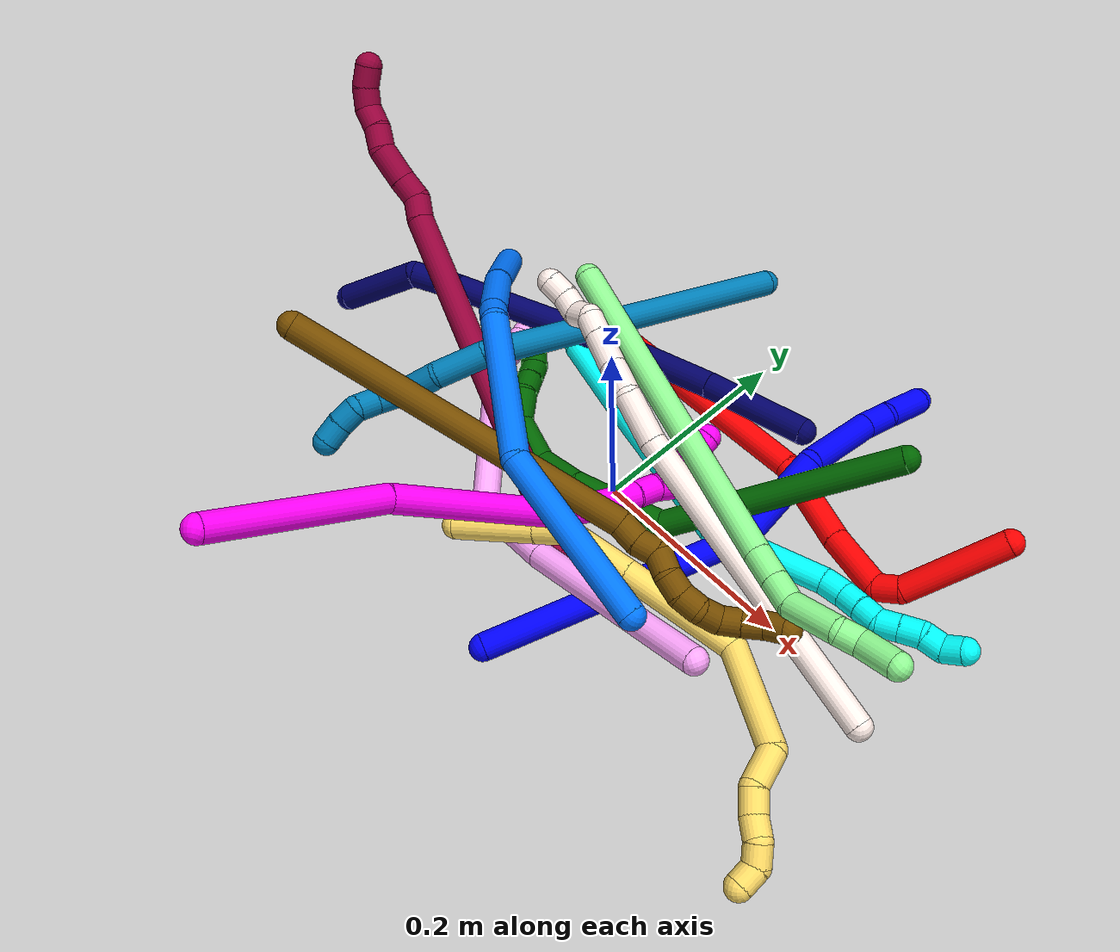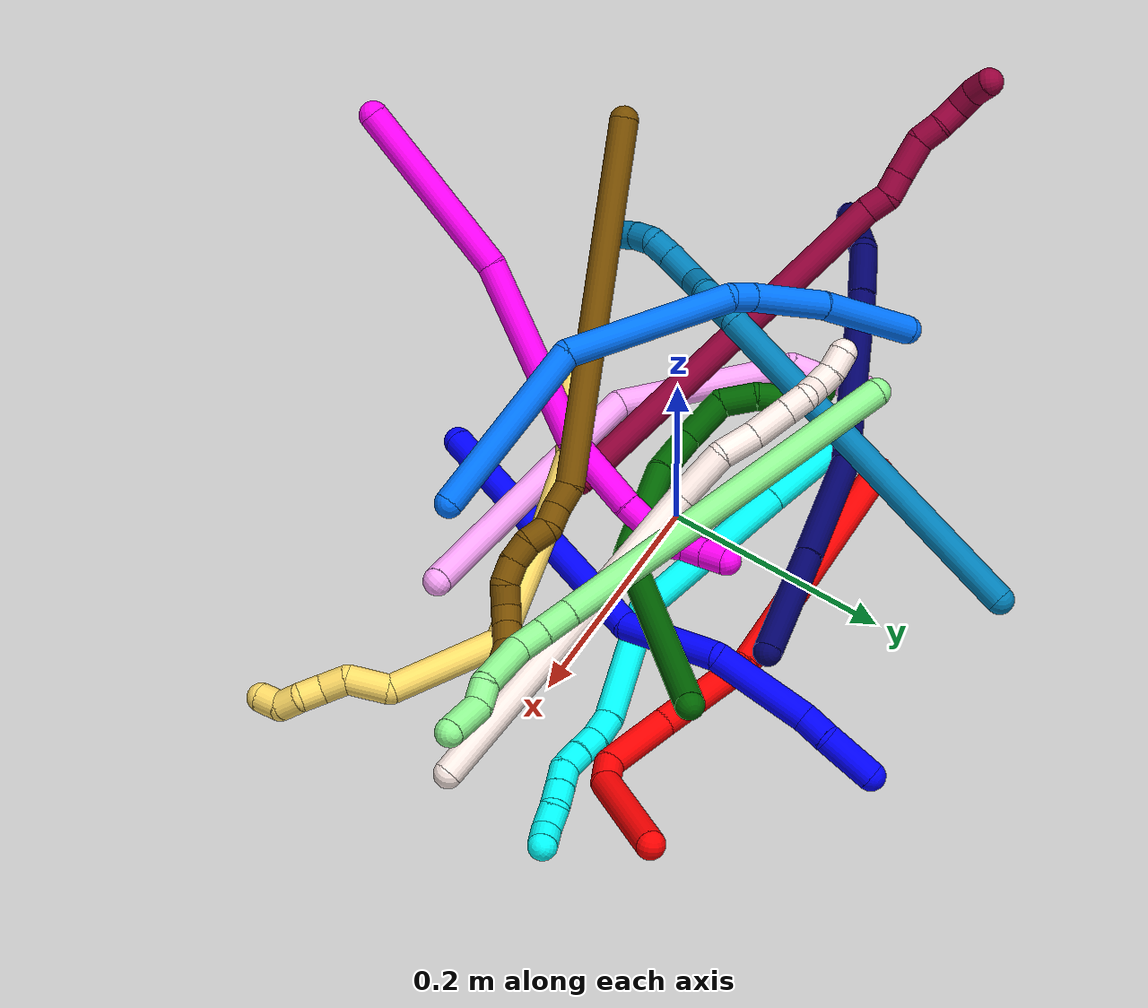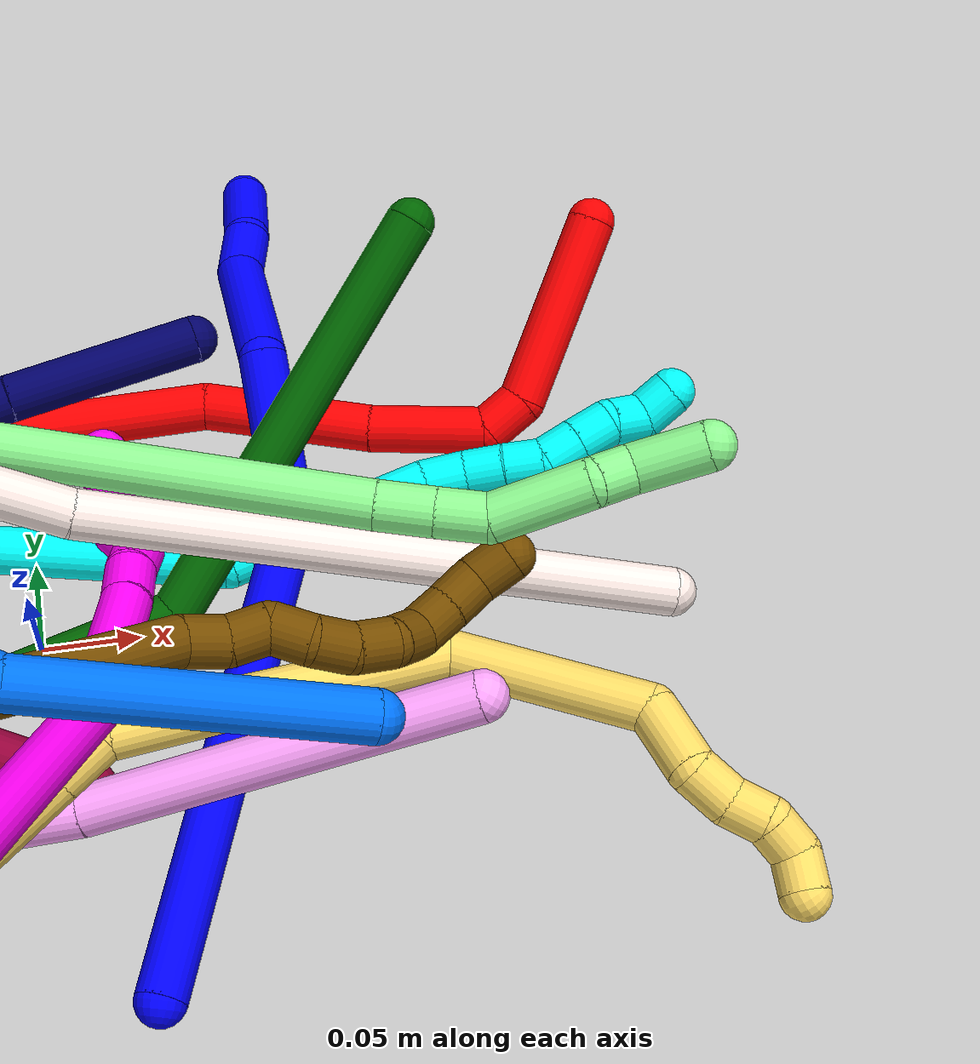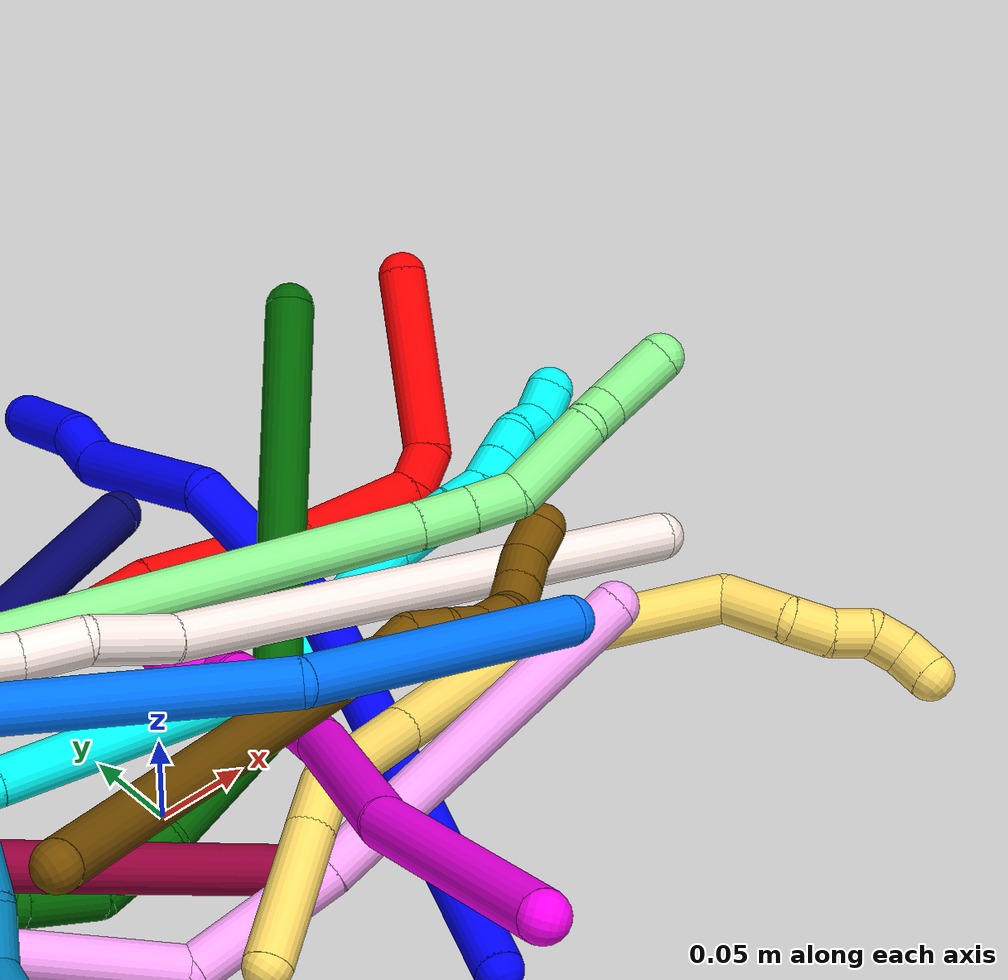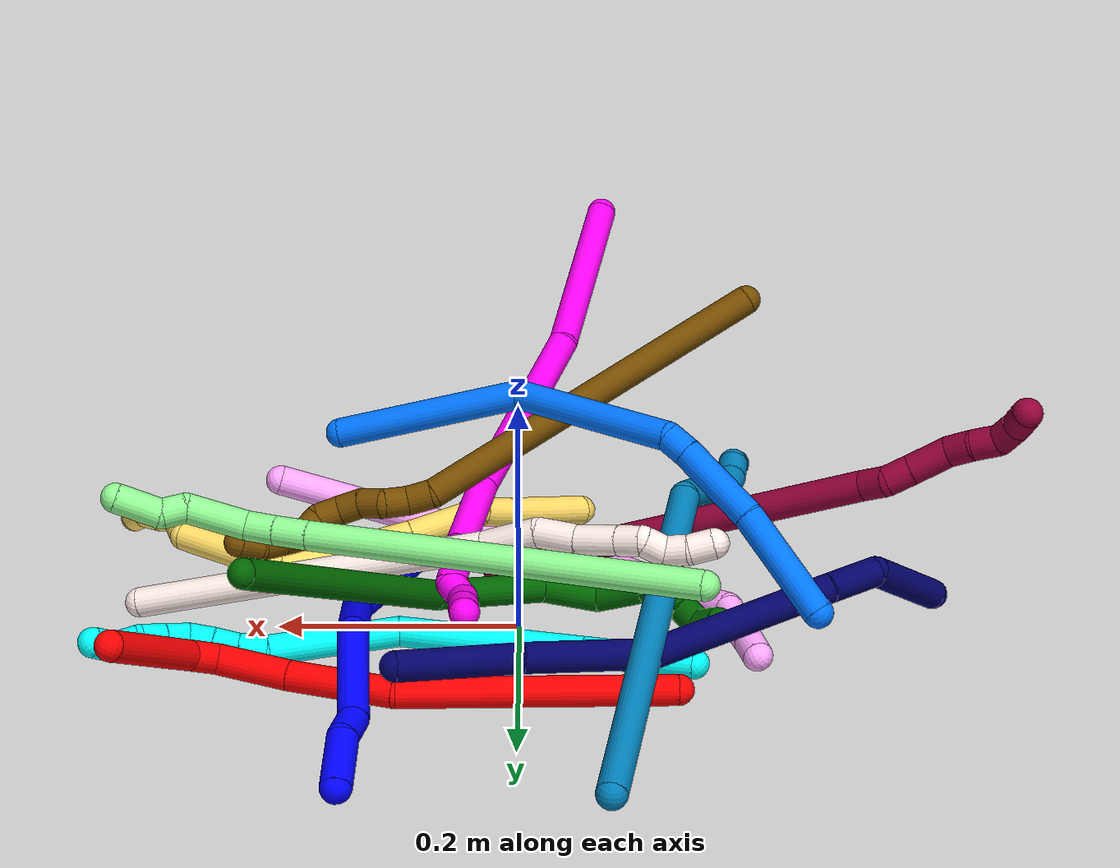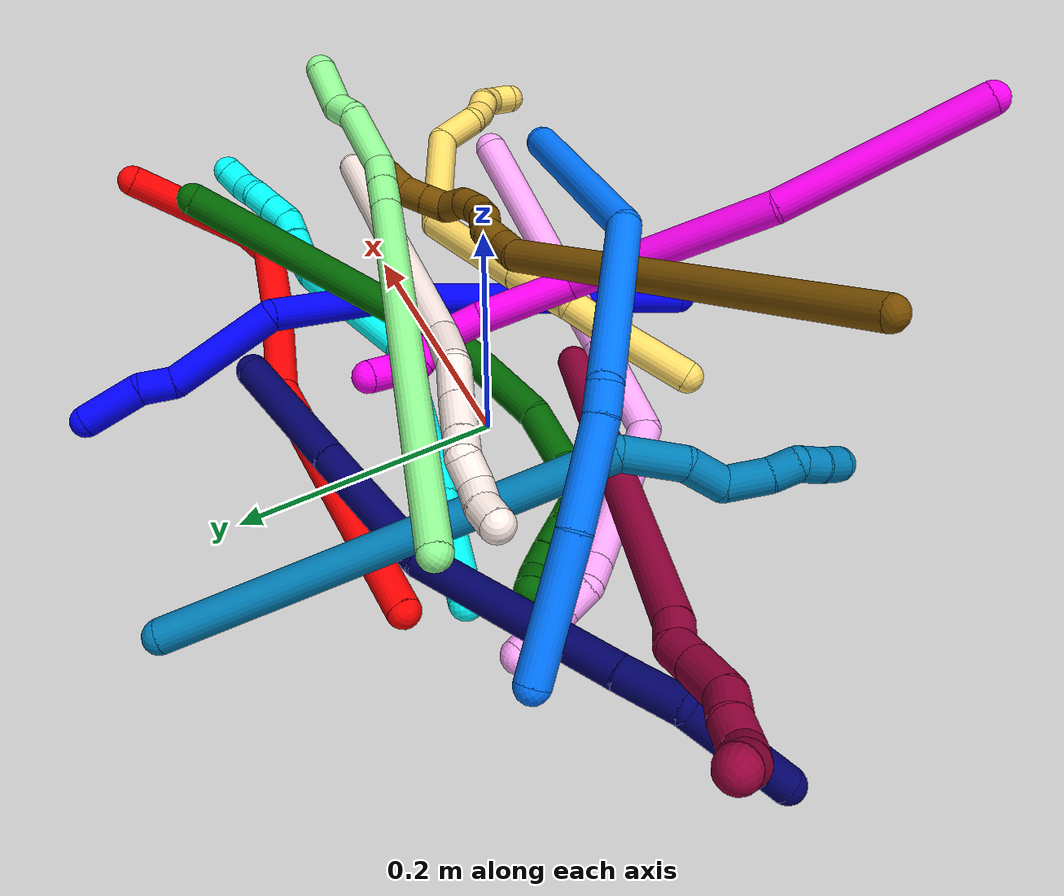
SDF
<sdf version="1.7">
 <world name="default">
  <plugin name="TubeGeneratorPlugin" filename="libtube_generator_plugin.so"/>
  <model name="photoneo_s_sensor">
   <static>1</static>
   <pose>0 0 2 1.57079 1.57079 3.14159</pose>
   <link name="link">
    <inertial><mass>0.1</mass></inertial>
    <sensor name="sensor" type="depth">
     <update_rate>30</update_rate>
     <camera>
      <horizontal_fov>1.22</horizontal_fov>
      <image><width>1920</width><height>1200</height><format>B8G8R8</format></image>
      <clip><near>0.1</near><far>4</far></clip>
      <depth_camera><output>points</output></depth_camera>
     </camera>
     <plugin name="camera_plugin" filename="libgazebo_ros_depth_camera.so">
      <baseline>0.2</baseline>
      <alwaysOn>1</alwaysOn>
      <updateRate>0.0</updateRate>
      <cameraName>camera_ir</cameraName>
      <imageTopicName>/camera/color/image_raw</imageTopicName>
      <cameraInfoTopicName>/camera/color/camera_info</cameraInfoTopicName>
      <depthImageTopicName>/camera/depth/image_raw</depthImageTopicName>
      <depthImageCameraInfoTopicName>/camera/depth/camera_info</depthImageCameraInfoTopicName>
      <pointCloudTopicName>/camera/depth/points</pointCloudTopicName>
      <frameName>fr_optical</frameName>
      <pointCloudCutoff>0.1</pointCloudCutoff>
      <pointCloudCutoffMax>2.0</pointCloudCutoffMax>
      <distortionK1>0</distortionK1>
      <distortionK2>0</distortionK2>
      <distortionK3>0</distortionK3>
      <distortionT1>0</distortionT1>
      <distortionT2>0</distortionT2>
      <CxPrime>0</CxPrime>
      <Cx>0</Cx>
      <Cy>0</Cy>
      <focalLength>0</focalLength>
      <hackBaseline>0</hackBaseline>
     </plugin>
    </sensor>
   </link>
  </model>
  <gravity>0 0 -9.8</gravity>
  <magnetic_field>6e-06 2.3e-05 -4.2e-05</magnetic_field>
  <atmosphere type="adiabatic"/>
  <physics name="default_physics" default="0" type="ode">
   <max_step_size>0.003</max_step_size>
   <real_time_factor>1</real_time_factor>
   <real_time_update_rate>1000</real_time_update_rate>
   <max_contacts>10000</max_contacts>
   <ode>
    <solver>
     <type>quick</type>
     <iters>100</iters>
     <sor>1.3</sor>
     <use_dynamic_moi_rescaling>0</use_dynamic_moi_rescaling>
    </solver>
    <constraints>
     <contact_max_correcting_vel>0</contact_max_correcting_vel>
     <contact_surface_layer>0.001</contact_surface_layer>
     <cfm>0</cfm>
     <erp>0.2</erp>
    </constraints>
   </ode>
  </physics>
  <scene><ambient>0.4 0.4 0.4 1</ambient><background>0.7 0.7 0.7 1</background><shadows>0</shadows></scene>
  <audio><device>default</device></audio>
  <spherical_coordinates>
   <surface_model>EARTH_WGS84</surface_model>
   <latitude_deg>0</latitude_deg>
   <longitude_deg>0</longitude_deg>
   <elevation>0</elevation>
   <heading_deg>0</heading_deg>
  </spherical_coordinates>
  <model name="bin">
   <static>1</static>
   <link name="bottom">
    <collision name="collision-bottom">
     <pose>0 0 -0.01 0 -0 0</pose>
     <geometry><box><size>0.8 0.6 0.02</size></box></geometry>
     <surface>
      <friction><ode><mu>100</mu><mu2>100</mu2></ode></friction>
      <contact><collide_bitmask>65535</collide_bitmask></contact>
     </surface>
    </collision>
   </link>
   <link name="west_wall">
    <collision name="collision-west_wall">
     <pose>-0.41 0 0.1 0 -0 0</pose>
     <geometry><box><size>0.02 0.6 0.2</size></box></geometry>
     <surface>
      <friction><ode><mu>100</mu><mu2>100</mu2></ode></friction>
      <contact><collide_bitmask>65535</collide_bitmask></contact>
     </surface>
    </collision>
   </link>
   <link name="east_wall">
    <collision name="collision-east_wall">
     <pose>0.41 0 0.1 0 -0 0</pose>
     <geometry><box><size>0.02 0.6 0.2</size></box></geometry>
     <surface>
      <friction><ode><mu>100</mu><mu2>100</mu2></ode></friction>
      <contact><collide_bitmask>65535</collide_bitmask></contact>
     </surface>
    </collision>
   </link>
   <link name="south_wall">
    <collision name="collision-south_wall">
     <pose>0 -0.31 0.1 0 -0 0</pose>
     <geometry><box><size>0.8 0.02 0.2</size></box></geometry>
     <surface>
      <friction><ode><mu>100</mu><mu2>100</mu2></ode></friction>
      <contact><collide_bitmask>65535</collide_bitmask></contact>
     </surface>
    </collision>
   </link>
   <link name="north_wall">
    <collision name="collision-north_wall">
     <pose>0 0.31 0.1 0 -0 0</pose>
     <geometry><box><size>0.8 0.02 0.2</size></box></geometry>
     <surface>
      <friction><ode><mu>100</mu><mu2>100</mu2></ode></friction>
      <contact><collide_bitmask>65535</collide_bitmask></contact>
     </surface>
    </collision>
   </link>
  </model>
  <model name="1">
   <static>0</static>
   <link name="1">
    <collision name="collision-cylinder-e_1_1_4">
     <pose>0.021854 0.020669 0.119803 -0.170846 0.177858 -0.01527</pose>
     <geometry><cylinder><radius>0.0125</radius><length>0.247042</length></cylinder></geometry>
     <surface>
      <friction><ode><mu>1.16</mu><mu2>1.16</mu2><slip1>0</slip1><slip2>0</slip2></ode></friction>
      <contact><ode><kp>1e+06</kp><kd>1</kd><max_vel>0</max_vel><min_depth>0.001</min_depth></ode></contact>
     </surface>
    </collision>
    <visual name="visual-cylinder-e_1_1_4">
     <pose>0.021854 0.020669 0.119803 -0.170846 0.177858 -0.01527</pose>
     <geometry><cylinder><radius>0.0125</radius><length>0.247042</length></cylinder></geometry>
     <material><ambient>0 0 1 1</ambient></material>
    </visual>
    <collision name="collision-cylinder-e_2_4_5">
     <pose>0.032069 0.047514 0.283124 -0.140966 -0.258835 0.018376</pose>
     <geometry><cylinder><radius>0.0125</radius><length>0.09094</length></cylinder></geometry>
     <surface>
      <friction><ode><mu>1.16</mu><mu2>1.16</mu2><slip1>0</slip1><slip2>0</slip2></ode></friction>
      <contact><ode><kp>1e+06</kp><kd>1</kd><max_vel>0</max_vel><min_depth>0.001</min_depth></ode></contact>
     </surface>
    </collision>
    <visual name="visual-cylinder-e_2_4_5">
     <pose>0.032069 0.047514 0.283124 -0.140966 -0.258835 0.018376</pose>
     <geometry><cylinder><radius>0.0125</radius><length>0.09094</length></cylinder></geometry>
     <material><ambient>0 0 1 1</ambient></material>
    </visual>
    <collision name="collision-cylinder-e_3_5_6">
     <pose>0.018864 0.083456 0.359042 -0.743075 -0.035604 0.013874</pose>
     <geometry><cylinder><radius>0.0125</radius><length>0.088049</length></cylinder></geometry>
     <surface>
      <friction><ode><mu>1.16</mu><mu2>1.16</mu2><slip1>0</slip1><slip2>0</slip2></ode></friction>
      <contact><ode><kp>1e+06</kp><kd>1</kd><max_vel>0</max_vel><min_depth>0.001</min_depth></ode></contact>
     </surface>
    </collision>
    <visual name="visual-cylinder-e_3_5_6">
     <pose>0.018864 0.083456 0.359042 -0.743075 -0.035604 0.013874</pose>
     <geometry><cylinder><radius>0.0125</radius><length>0.088049</length></cylinder></geometry>
     <material><ambient>0 0 1 1</ambient></material>
    </visual>
    <collision name="collision-cylinder-e_4_6_7">
     <pose>0.018651 0.117496 0.403866 -0.331293 0.102739 -0.01719</pose>
     <geometry><cylinder><radius>0.0125</radius><length>0.026418</length></cylinder></geometry>
     <surface>
      <friction><ode><mu>1.16</mu><mu2>1.16</mu2><slip1>0</slip1><slip2>0</slip2></ode></friction>
      <contact><ode><kp>1e+06</kp><kd>1</kd><max_vel>0</max_vel><min_depth>0.001</min_depth></ode></contact>
     </surface>
    </collision>
    <visual name="visual-cylinder-e_4_6_7">
     <pose>0.018651 0.117496 0.403866 -0.331293 0.102739 -0.01719</pose>
     <geometry><cylinder><radius>0.0125</radius><length>0.026418</length></cylinder></geometry>
     <material><ambient>0 0 1 1</ambient></material>
    </visual>
    <collision name="collision-cylinder-e_5_7_2">
     <pose>0.021661 0.137225 0.434282 -0.709722 0.069668 -0.025824</pose>
     <geometry><cylinder><radius>0.0125</radius><length>0.047552</length></cylinder></geometry>
     <surface>
      <friction><ode><mu>1.16</mu><mu2>1.16</mu2><slip1>0</slip1><slip2>0</slip2></ode></friction>
      <contact><ode><kp>1e+06</kp><kd>1</kd><max_vel>0</max_vel><min_depth>0.001</min_depth></ode></contact>
     </surface>
    </collision>
    <visual name="visual-cylinder-e_5_7_2">
     <pose>0.021661 0.137225 0.434282 -0.709722 0.069668 -0.025824</pose>
     <geometry><cylinder><radius>0.0125</radius><length>0.047552</length></cylinder></geometry>
     <material><ambient>0 0 1 1</ambient></material>
    </visual>
    <collision name="collision-sphere-2">
     <pose>0.023316 0.15268 0.452273 0 -0 0</pose>
     <geometry><sphere><radius>0.0125</radius></sphere></geometry>
     <surface>
      <friction><ode><mu>1.16</mu><mu2>1.16</mu2><slip1>0</slip1><slip2>0</slip2></ode></friction>
      <contact><ode><kp>1e+06</kp><kd>1</kd><max_vel>0</max_vel><min_depth>0.001</min_depth></ode></contact>
     </surface>
    </collision>
    <visual name="visual-sphere-2">
     <pose>0.023316 0.15268 0.452273 0 -0 0</pose>
     <geometry><sphere><radius>0.0125</radius></sphere></geometry>
     <material><ambient>0 0 1 1</ambient></material>
    </visual>
    <collision name="collision-sphere-7">
     <pose>0.020006 0.12177 0.41629 0 -0 0</pose>
     <geometry><sphere><radius>0.0125</radius></sphere></geometry>
     <surface>
      <friction><ode><mu>1.16</mu><mu2>1.16</mu2><slip1>0</slip1><slip2>0</slip2></ode></friction>
      <contact><ode><kp>1e+06</kp><kd>1</kd><max_vel>0</max_vel><min_depth>0.001</min_depth></ode></contact>
     </surface>
    </collision>
    <visual name="visual-sphere-7">
     <pose>0.020006 0.12177 0.41629 0 -0 0</pose>
     <geometry><sphere><radius>0.0125</radius></sphere></geometry>
     <material><ambient>0 0 1 1</ambient></material>
    </visual>
    <collision name="collision-sphere-6">
     <pose>0.017296 0.113222 0.391441 0 -0 0</pose>
     <geometry><sphere><radius>0.0125</radius></sphere></geometry>
     <surface>
      <friction><ode><mu>1.16</mu><mu2>1.16</mu2><slip1>0</slip1><slip2>0</slip2></ode></friction>
      <contact><ode><kp>1e+06</kp><kd>1</kd><max_vel>0</max_vel><min_depth>0.001</min_depth></ode></contact>
     </surface>
    </collision>
    <visual name="visual-sphere-6">
     <pose>0.017296 0.113222 0.391441 0 -0 0</pose>
     <geometry><sphere><radius>0.0125</radius></sphere></geometry>
     <material><ambient>0 0 1 1</ambient></material>
    </visual>
    <collision name="collision-sphere-5">
     <pose>0.020431 0.05369 0.326644 0 -0 0</pose>
     <geometry><sphere><radius>0.0125</radius></sphere></geometry>
     <surface>
      <friction><ode><mu>1.16</mu><mu2>1.16</mu2><slip1>0</slip1><slip2>0</slip2></ode></friction>
      <contact><ode><kp>1e+06</kp><kd>1</kd><max_vel>0</max_vel><min_depth>0.001</min_depth></ode></contact>
     </surface>
    </collision>
    <visual name="visual-sphere-5">
     <pose>0.020431 0.05369 0.326644 0 -0 0</pose>
     <geometry><sphere><radius>0.0125</radius></sphere></geometry>
     <material><ambient>0 0 1 1</ambient></material>
    </visual>
    <collision name="collision-sphere-1">
     <geometry><sphere><radius>0.0125</radius></sphere></geometry>
     <surface>
      <friction><ode><mu>1.16</mu><mu2>1.16</mu2><slip1>0</slip1><slip2>0</slip2></ode></friction>
      <contact><ode><kp>1e+06</kp><kd>1</kd><max_vel>0</max_vel><min_depth>0.001</min_depth></ode></contact>
     </surface>
    </collision>
    <visual name="visual-sphere-1">
     <geometry><sphere><radius>0.0125</radius></sphere></geometry>
     <material><ambient>0 0 1 1</ambient></material>
    </visual>
    <collision name="collision-sphere-4">
     <pose>0.043707 0.041339 0.239605 0 -0 0</pose>
     <geometry><sphere><radius>0.0125</radius></sphere></geometry>
     <surface>
      <friction><ode><mu>1.16</mu><mu2>1.16</mu2><slip1>0</slip1><slip2>0</slip2></ode></friction>
      <contact><ode><kp>1e+06</kp><kd>1</kd><max_vel>0</max_vel><min_depth>0.001</min_depth></ode></contact>
     </surface>
    </collision>
    <visual name="visual-sphere-4">
     <pose>0.043707 0.041339 0.239605 0 -0 0</pose>
     <geometry><sphere><radius>0.0125</radius></sphere></geometry>
     <material><ambient>0 0 1 1</ambient></material>
    </visual>
    <inertial>
     <pose>0.022997 0.052809 0.236554 0 -0 0</pose>
     <mass>0.5</mass>
     <inertia>
      <ixx>0.001368</ixx>
      <ixy>0</ixy>
      <ixz>0</ixz>
      <iyy>0.001363</iyy>
      <iyz>0</iyz>
      <izz>-0.00044</izz>
     </inertia>
    </inertial>
   </link>
   <pose>0.04405 -0.19658 0.011487 -1.22072 0.386022 -0.131909</pose>
  </model>
  <model name="2">
   <static>0</static>
   <link name="2">
    <collision name="collision-cylinder-e_1_1_4">
     <pose>-0.007217 0.05017 0.003344 -1.50424 -0.142554 0.133397</pose>
     <geometry><cylinder><radius>0.0125</radius><length>0.101593</length></cylinder></geometry>
     <surface>
      <friction><ode><mu>1.16</mu><mu2>1.16</mu2><slip1>0</slip1><slip2>0</slip2></ode></friction>
      <contact><ode><kp>1e+06</kp><kd>1</kd><max_vel>0</max_vel><min_depth>0.001</min_depth></ode></contact>
     </surface>
    </collision>
    <visual name="visual-cylinder-e_1_1_4">
     <pose>-0.007217 0.05017 0.003344 -1.50424 -0.142554 0.133397</pose>
     <geometry><cylinder><radius>0.0125</radius><length>0.101593</length></cylinder></geometry>
     <material><ambient>1 0 0 1</ambient></material>
    </visual>
    <collision name="collision-cylinder-e_2_4_5">
     <pose>-0.020957 0.11021 0.00454 -1.7851 -0.573404 0.701529</pose>
     <geometry><cylinder><radius>0.0125</radius><length>0.024049</length></cylinder></geometry>
     <surface>
      <friction><ode><mu>1.16</mu><mu2>1.16</mu2><slip1>0</slip1><slip2>0</slip2></ode></friction>
      <contact><ode><kp>1e+06</kp><kd>1</kd><max_vel>0</max_vel><min_depth>0.001</min_depth></ode></contact>
     </surface>
    </collision>
    <visual name="visual-cylinder-e_2_4_5">
     <pose>-0.020957 0.11021 0.00454 -1.7851 -0.573404 0.701529</pose>
     <geometry><cylinder><radius>0.0125</radius><length>0.024049</length></cylinder></geometry>
     <material><ambient>1 0 0 1</ambient></material>
    </visual>
    <collision name="collision-cylinder-e_3_5_6">
     <pose>-0.055293 0.127154 -0.008789 -2.57753 -1.12679 2.28146</pose>
     <geometry><cylinder><radius>0.0125</radius><length>0.061598</length></cylinder></geometry>
     <surface>
      <friction><ode><mu>1.16</mu><mu2>1.16</mu2><slip1>0</slip1><slip2>0</slip2></ode></friction>
      <contact><ode><kp>1e+06</kp><kd>1</kd><max_vel>0</max_vel><min_depth>0.001</min_depth></ode></contact>
     </surface>
    </collision>
    <visual name="visual-cylinder-e_3_5_6">
     <pose>-0.055293 0.127154 -0.008789 -2.57753 -1.12679 2.28146</pose>
     <geometry><cylinder><radius>0.0125</radius><length>0.061598</length></cylinder></geometry>
     <material><ambient>1 0 0 1</ambient></material>
    </visual>
    <collision name="collision-cylinder-e_4_6_7">
     <pose>-0.12287 0.140091 -0.039668 -2.85222 -1.09375 2.67178</pose>
     <geometry><cylinder><radius>0.0125</radius><length>0.089524</length></cylinder></geometry>
     <surface>
      <friction><ode><mu>1.16</mu><mu2>1.16</mu2><slip1>0</slip1><slip2>0</slip2></ode></friction>
      <contact><ode><kp>1e+06</kp><kd>1</kd><max_vel>0</max_vel><min_depth>0.001</min_depth></ode></contact>
     </surface>
    </collision>
    <visual name="visual-cylinder-e_4_6_7">
     <pose>-0.12287 0.140091 -0.039668 -2.85222 -1.09375 2.67178</pose>
     <geometry><cylinder><radius>0.0125</radius><length>0.089524</length></cylinder></geometry>
     <material><ambient>1 0 0 1</ambient></material>
    </visual>
    <collision name="collision-cylinder-e_5_7_2">
     <pose>-0.245978 0.193155 -0.116678 -2.45266 -0.843067 1.792</pose>
     <geometry><cylinder><radius>0.0125</radius><length>0.223235</length></cylinder></geometry>
     <surface>
      <friction><ode><mu>1.16</mu><mu2>1.16</mu2><slip1>0</slip1><slip2>0</slip2></ode></friction>
      <contact><ode><kp>1e+06</kp><kd>1</kd><max_vel>0</max_vel><min_depth>0.001</min_depth></ode></contact>
     </surface>
    </collision>
    <visual name="visual-cylinder-e_5_7_2">
     <pose>-0.245978 0.193155 -0.116678 -2.45266 -0.843067 1.792</pose>
     <geometry><cylinder><radius>0.0125</radius><length>0.223235</length></cylinder></geometry>
     <material><ambient>1 0 0 1</ambient></material>
    </visual>
    <collision name="collision-sphere-2">
     <pose>-0.329322 0.240354 -0.17399 0 -0 0</pose>
     <geometry><sphere><radius>0.0125</radius></sphere></geometry>
     <surface>
      <friction><ode><mu>1.16</mu><mu2>1.16</mu2><slip1>0</slip1><slip2>0</slip2></ode></friction>
      <contact><ode><kp>1e+06</kp><kd>1</kd><max_vel>0</max_vel><min_depth>0.001</min_depth></ode></contact>
     </surface>
    </collision>
    <visual name="visual-sphere-2">
     <pose>-0.329322 0.240354 -0.17399 0 -0 0</pose>
     <geometry><sphere><radius>0.0125</radius></sphere></geometry>
     <material><ambient>1 0 0 1</ambient></material>
    </visual>
    <collision name="collision-sphere-7">
     <pose>-0.162635 0.145956 -0.059367 0 -0 0</pose>
     <geometry><sphere><radius>0.0125</radius></sphere></geometry>
     <surface>
      <friction><ode><mu>1.16</mu><mu2>1.16</mu2><slip1>0</slip1><slip2>0</slip2></ode></friction>
      <contact><ode><kp>1e+06</kp><kd>1</kd><max_vel>0</max_vel><min_depth>0.001</min_depth></ode></contact>
     </surface>
    </collision>
    <visual name="visual-sphere-7">
     <pose>-0.162635 0.145956 -0.059367 0 -0 0</pose>
     <geometry><sphere><radius>0.0125</radius></sphere></geometry>
     <material><ambient>1 0 0 1</ambient></material>
    </visual>
    <collision name="collision-sphere-6">
     <pose>-0.083106 0.134227 -0.01997 0 -0 0</pose>
     <geometry><sphere><radius>0.0125</radius></sphere></geometry>
     <surface>
      <friction><ode><mu>1.16</mu><mu2>1.16</mu2><slip1>0</slip1><slip2>0</slip2></ode></friction>
      <contact><ode><kp>1e+06</kp><kd>1</kd><max_vel>0</max_vel><min_depth>0.001</min_depth></ode></contact>
     </surface>
    </collision>
    <visual name="visual-sphere-6">
     <pose>-0.083106 0.134227 -0.01997 0 -0 0</pose>
     <geometry><sphere><radius>0.0125</radius></sphere></geometry>
     <material><ambient>1 0 0 1</ambient></material>
    </visual>
    <collision name="collision-sphere-5">
     <pose>-0.02748 0.12008 0.002392 0 -0 0</pose>
     <geometry><sphere><radius>0.0125</radius></sphere></geometry>
     <surface>
      <friction><ode><mu>1.16</mu><mu2>1.16</mu2><slip1>0</slip1><slip2>0</slip2></ode></friction>
      <contact><ode><kp>1e+06</kp><kd>1</kd><max_vel>0</max_vel><min_depth>0.001</min_depth></ode></contact>
     </surface>
    </collision>
    <visual name="visual-sphere-5">
     <pose>-0.02748 0.12008 0.002392 0 -0 0</pose>
     <geometry><sphere><radius>0.0125</radius></sphere></geometry>
     <material><ambient>1 0 0 1</ambient></material>
    </visual>
    <collision name="collision-sphere-1">
     <geometry><sphere><radius>0.0125</radius></sphere></geometry>
     <surface>
      <friction><ode><mu>1.16</mu><mu2>1.16</mu2><slip1>0</slip1><slip2>0</slip2></ode></friction>
      <contact><ode><kp>1e+06</kp><kd>1</kd><max_vel>0</max_vel><min_depth>0.001</min_depth></ode></contact>
     </surface>
    </collision>
    <visual name="visual-sphere-1">
     <geometry><sphere><radius>0.0125</radius></sphere></geometry>
     <material><ambient>1 0 0 1</ambient></material>
    </visual>
    <collision name="collision-sphere-4">
     <pose>-0.014433 0.10034 0.006688 0 -0 0</pose>
     <geometry><sphere><radius>0.0125</radius></sphere></geometry>
     <surface>
      <friction><ode><mu>1.16</mu><mu2>1.16</mu2><slip1>0</slip1><slip2>0</slip2></ode></friction>
      <contact><ode><kp>1e+06</kp><kd>1</kd><max_vel>0</max_vel><min_depth>0.001</min_depth></ode></contact>
     </surface>
    </collision>
    <visual name="visual-sphere-4">
     <pose>-0.014433 0.10034 0.006688 0 -0 0</pose>
     <geometry><sphere><radius>0.0125</radius></sphere></geometry>
     <material><ambient>1 0 0 1</ambient></material>
    </visual>
    <inertial>
     <pose>-0.141108 0.142481 -0.059381 0 -0 0</pose>
     <mass>0.5</mass>
     <inertia>
      <ixx>0.000537</ixx>
      <ixy>0</ixy>
      <ixz>0</ixz>
      <iyy>0.001341</iyy>
      <iyz>0</iyz>
      <izz>0.000274</izz>
     </inertia>
    </inertial>
   </link>
   <pose>0.309383 0.171528 0.076529 -2.71516 -0.372179 -0.620398</pose>
  </model>
  <model name="3">
   <static>0</static>
   <link name="3">
    <collision name="collision-cylinder-e_1_1_4">
     <pose>0.031599 -0.018554 0.026396 0.612677 0.774963 0.256749</pose>
     <geometry><cylinder><radius>0.0125</radius><length>0.090322</length></cylinder></geometry>
     <surface>
      <friction><ode><mu>1.16</mu><mu2>1.16</mu2><slip1>0</slip1><slip2>0</slip2></ode></friction>
      <contact><ode><kp>1e+06</kp><kd>1</kd><max_vel>0</max_vel><min_depth>0.001</min_depth></ode></contact>
     </surface>
    </collision>
    <visual name="visual-cylinder-e_1_1_4">
     <pose>0.031599 -0.018554 0.026396 0.612677 0.774963 0.256749</pose>
     <geometry><cylinder><radius>0.0125</radius><length>0.090322</length></cylinder></geometry>
     <material><ambient>0.003922 1 0.996078 1</ambient></material>
    </visual>
    <collision name="collision-cylinder-e_2_4_5">
     <pose>0.117652 -0.067198 0.098918 0.578014 0.779761 0.243151</pose>
     <geometry><cylinder><radius>0.0125</radius><length>0.154897</length></cylinder></geometry>
     <surface>
      <friction><ode><mu>1.16</mu><mu2>1.16</mu2><slip1>0</slip1><slip2>0</slip2></ode></friction>
      <contact><ode><kp>1e+06</kp><kd>1</kd><max_vel>0</max_vel><min_depth>0.001</min_depth></ode></contact>
     </surface>
    </collision>
    <visual name="visual-cylinder-e_2_4_5">
     <pose>0.117652 -0.067198 0.098918 0.578014 0.779761 0.243151</pose>
     <geometry><cylinder><radius>0.0125</radius><length>0.154897</length></cylinder></geometry>
     <material><ambient>0.003922 1 0.996078 1</ambient></material>
    </visual>
    <collision name="collision-cylinder-e_3_5_6">
     <pose>0.217677 -0.090649 0.175629 -0.213745 0.969 -0.112814</pose>
     <geometry><cylinder><radius>0.0125</radius><length>0.110565</length></cylinder></geometry>
     <surface>
      <friction><ode><mu>1.16</mu><mu2>1.16</mu2><slip1>0</slip1><slip2>0</slip2></ode></friction>
      <contact><ode><kp>1e+06</kp><kd>1</kd><max_vel>0</max_vel><min_depth>0.001</min_depth></ode></contact>
     </surface>
    </collision>
    <visual name="visual-cylinder-e_3_5_6">
     <pose>0.217677 -0.090649 0.175629 -0.213745 0.969 -0.112814</pose>
     <geometry><cylinder><radius>0.0125</radius><length>0.110565</length></cylinder></geometry>
     <material><ambient>0.003922 1 0.996078 1</ambient></material>
    </visual>
    <collision name="collision-cylinder-e_4_6_7">
     <pose>0.271662 -0.085244 0.213909 0.158951 0.823653 0.069549</pose>
     <geometry><cylinder><radius>0.0125</radius><length>0.022938</length></cylinder></geometry>
     <surface>
      <friction><ode><mu>1.16</mu><mu2>1.16</mu2><slip1>0</slip1><slip2>0</slip2></ode></friction>
      <contact><ode><kp>1e+06</kp><kd>1</kd><max_vel>0</max_vel><min_depth>0.001</min_depth></ode></contact>
     </surface>
    </collision>
    <visual name="visual-cylinder-e_4_6_7">
     <pose>0.271662 -0.085244 0.213909 0.158951 0.823653 0.069549</pose>
     <geometry><cylinder><radius>0.0125</radius><length>0.022938</length></cylinder></geometry>
     <material><ambient>0.003922 1 0.996078 1</ambient></material>
    </visual>
    <collision name="collision-cylinder-e_5_7_8">
     <pose>0.286378 -0.088719 0.2295 0.276627 0.654785 0.09448</pose>
     <geometry><cylinder><radius>0.0125</radius><length>0.020696</length></cylinder></geometry>
     <surface>
      <friction><ode><mu>1.16</mu><mu2>1.16</mu2><slip1>0</slip1><slip2>0</slip2></ode></friction>
      <contact><ode><kp>1e+06</kp><kd>1</kd><max_vel>0</max_vel><min_depth>0.001</min_depth></ode></contact>
     </surface>
    </collision>
    <visual name="visual-cylinder-e_5_7_8">
     <pose>0.286378 -0.088719 0.2295 0.276627 0.654785 0.09448</pose>
     <geometry><cylinder><radius>0.0125</radius><length>0.020696</length></cylinder></geometry>
     <material><ambient>0.003922 1 0.996078 1</ambient></material>
    </visual>
    <collision name="collision-cylinder-e_6_8_9">
     <pose>0.299414 -0.093255 0.244597 0.308446 0.727869 0.11829</pose>
     <geometry><cylinder><radius>0.0125</radius><length>0.020246</length></cylinder></geometry>
     <surface>
      <friction><ode><mu>1.16</mu><mu2>1.16</mu2><slip1>0</slip1><slip2>0</slip2></ode></friction>
      <contact><ode><kp>1e+06</kp><kd>1</kd><max_vel>0</max_vel><min_depth>0.001</min_depth></ode></contact>
     </surface>
    </collision>
    <visual name="visual-cylinder-e_6_8_9">
     <pose>0.299414 -0.093255 0.244597 0.308446 0.727869 0.11829</pose>
     <geometry><cylinder><radius>0.0125</radius><length>0.020246</length></cylinder></geometry>
     <material><ambient>0.003922 1 0.996078 1</ambient></material>
    </visual>
    <collision name="collision-cylinder-e_7_9_10">
     <pose>0.313313 -0.093202 0.258369 -0.34303 0.798559 -0.145916</pose>
     <geometry><cylinder><radius>0.0125</radius><length>0.020002</length></cylinder></geometry>
     <surface>
      <friction><ode><mu>1.16</mu><mu2>1.16</mu2><slip1>0</slip1><slip2>0</slip2></ode></friction>
      <contact><ode><kp>1e+06</kp><kd>1</kd><max_vel>0</max_vel><min_depth>0.001</min_depth></ode></contact>
     </surface>
    </collision>
    <visual name="visual-cylinder-e_7_9_10">
     <pose>0.313313 -0.093202 0.258369 -0.34303 0.798559 -0.145916</pose>
     <geometry><cylinder><radius>0.0125</radius><length>0.020002</length></cylinder></geometry>
     <material><ambient>0.003922 1 0.996078 1</ambient></material>
    </visual>
    <collision name="collision-cylinder-e_8_10_11">
     <pose>0.327764 -0.088691 0.271525 -0.317516 0.810424 -0.137139</pose>
     <geometry><cylinder><radius>0.0125</radius><length>0.020112</length></cylinder></geometry>
     <surface>
      <friction><ode><mu>1.16</mu><mu2>1.16</mu2><slip1>0</slip1><slip2>0</slip2></ode></friction>
      <contact><ode><kp>1e+06</kp><kd>1</kd><max_vel>0</max_vel><min_depth>0.001</min_depth></ode></contact>
     </surface>
    </collision>
    <visual name="visual-cylinder-e_8_10_11">
     <pose>0.327764 -0.088691 0.271525 -0.317516 0.810424 -0.137139</pose>
     <geometry><cylinder><radius>0.0125</radius><length>0.020112</length></cylinder></geometry>
     <material><ambient>0.003922 1 0.996078 1</ambient></material>
    </visual>
    <collision name="collision-cylinder-e_9_11_12">
     <pose>0.344349 -0.08668 0.281811 0.041295 1.19166 0.028002</pose>
     <geometry><cylinder><radius>0.0125</radius><length>0.020021</length></cylinder></geometry>
     <surface>
      <friction><ode><mu>1.16</mu><mu2>1.16</mu2><slip1>0</slip1><slip2>0</slip2></ode></friction>
      <contact><ode><kp>1e+06</kp><kd>1</kd><max_vel>0</max_vel><min_depth>0.001</min_depth></ode></contact>
     </surface>
    </collision>
    <visual name="visual-cylinder-e_9_11_12">
     <pose>0.344349 -0.08668 0.281811 0.041295 1.19166 0.028002</pose>
     <geometry><cylinder><radius>0.0125</radius><length>0.020021</length></cylinder></geometry>
     <material><ambient>0.003922 1 0.996078 1</ambient></material>
    </visual>
    <collision name="collision-cylinder-e_10_12_2">
     <pose>0.358905 -0.083755 0.29357 -0.364978 0.547253 -0.103497</pose>
     <geometry><cylinder><radius>0.0125</radius><length>0.020201</length></cylinder></geometry>
     <surface>
      <friction><ode><mu>1.16</mu><mu2>1.16</mu2><slip1>0</slip1><slip2>0</slip2></ode></friction>
      <contact><ode><kp>1e+06</kp><kd>1</kd><max_vel>0</max_vel><min_depth>0.001</min_depth></ode></contact>
     </surface>
    </collision>
    <visual name="visual-cylinder-e_10_12_2">
     <pose>0.358905 -0.083755 0.29357 -0.364978 0.547253 -0.103497</pose>
     <geometry><cylinder><radius>0.0125</radius><length>0.020201</length></cylinder></geometry>
     <material><ambient>0.003922 1 0.996078 1</ambient></material>
    </visual>
    <collision name="collision-sphere-2">
     <pose>0.364161 -0.080676 0.301628 0 -0 0</pose>
     <geometry><sphere><radius>0.0125</radius></sphere></geometry>
     <surface>
      <friction><ode><mu>1.16</mu><mu2>1.16</mu2><slip1>0</slip1><slip2>0</slip2></ode></friction>
      <contact><ode><kp>1e+06</kp><kd>1</kd><max_vel>0</max_vel><min_depth>0.001</min_depth></ode></contact>
     </surface>
    </collision>
    <visual name="visual-sphere-2">
     <pose>0.364161 -0.080676 0.301628 0 -0 0</pose>
     <geometry><sphere><radius>0.0125</radius></sphere></geometry>
     <material><ambient>0.003922 1 0.996078 1</ambient></material>
    </visual>
    <collision name="collision-sphere-12">
     <pose>0.353649 -0.086833 0.285513 0 -0 0</pose>
     <geometry><sphere><radius>0.0125</radius></sphere></geometry>
     <surface>
      <friction><ode><mu>1.16</mu><mu2>1.16</mu2><slip1>0</slip1><slip2>0</slip2></ode></friction>
      <contact><ode><kp>1e+06</kp><kd>1</kd><max_vel>0</max_vel><min_depth>0.001</min_depth></ode></contact>
     </surface>
    </collision>
    <visual name="visual-sphere-12">
     <pose>0.353649 -0.086833 0.285513 0 -0 0</pose>
     <geometry><sphere><radius>0.0125</radius></sphere></geometry>
     <material><ambient>0.003922 1 0.996078 1</ambient></material>
    </visual>
    <collision name="collision-sphere-11">
     <pose>0.33505 -0.086528 0.278109 0 -0 0</pose>
     <geometry><sphere><radius>0.0125</radius></sphere></geometry>
     <surface>
      <friction><ode><mu>1.16</mu><mu2>1.16</mu2><slip1>0</slip1><slip2>0</slip2></ode></friction>
      <contact><ode><kp>1e+06</kp><kd>1</kd><max_vel>0</max_vel><min_depth>0.001</min_depth></ode></contact>
     </surface>
    </collision>
    <visual name="visual-sphere-11">
     <pose>0.33505 -0.086528 0.278109 0 -0 0</pose>
     <geometry><sphere><radius>0.0125</radius></sphere></geometry>
     <material><ambient>0.003922 1 0.996078 1</ambient></material>
    </visual>
    <collision name="collision-sphere-10">
     <pose>0.320477 -0.090855 0.264941 0 -0 0</pose>
     <geometry><sphere><radius>0.0125</radius></sphere></geometry>
     <surface>
      <friction><ode><mu>1.16</mu><mu2>1.16</mu2><slip1>0</slip1><slip2>0</slip2></ode></friction>
      <contact><ode><kp>1e+06</kp><kd>1</kd><max_vel>0</max_vel><min_depth>0.001</min_depth></ode></contact>
     </surface>
    </collision>
    <visual name="visual-sphere-10">
     <pose>0.320477 -0.090855 0.264941 0 -0 0</pose>
     <geometry><sphere><radius>0.0125</radius></sphere></geometry>
     <material><ambient>0.003922 1 0.996078 1</ambient></material>
    </visual>
    <collision name="collision-sphere-9">
     <pose>0.306149 -0.095549 0.251798 0 -0 0</pose>
     <geometry><sphere><radius>0.0125</radius></sphere></geometry>
     <surface>
      <friction><ode><mu>1.16</mu><mu2>1.16</mu2><slip1>0</slip1><slip2>0</slip2></ode></friction>
      <contact><ode><kp>1e+06</kp><kd>1</kd><max_vel>0</max_vel><min_depth>0.001</min_depth></ode></contact>
     </surface>
    </collision>
    <visual name="visual-sphere-9">
     <pose>0.306149 -0.095549 0.251798 0 -0 0</pose>
     <geometry><sphere><radius>0.0125</radius></sphere></geometry>
     <material><ambient>0.003922 1 0.996078 1</ambient></material>
    </visual>
    <collision name="collision-sphere-4">
     <pose>0.063197 -0.037109 0.052793 0 -0 0</pose>
     <geometry><sphere><radius>0.0125</radius></sphere></geometry>
     <surface>
      <friction><ode><mu>1.16</mu><mu2>1.16</mu2><slip1>0</slip1><slip2>0</slip2></ode></friction>
      <contact><ode><kp>1e+06</kp><kd>1</kd><max_vel>0</max_vel><min_depth>0.001</min_depth></ode></contact>
     </surface>
    </collision>
    <visual name="visual-sphere-4">
     <pose>0.063197 -0.037109 0.052793 0 -0 0</pose>
     <geometry><sphere><radius>0.0125</radius></sphere></geometry>
     <material><ambient>0.003922 1 0.996078 1</ambient></material>
    </visual>
    <collision name="collision-sphere-1">
     <geometry><sphere><radius>0.0125</radius></sphere></geometry>
     <surface>
      <friction><ode><mu>1.16</mu><mu2>1.16</mu2><slip1>0</slip1><slip2>0</slip2></ode></friction>
      <contact><ode><kp>1e+06</kp><kd>1</kd><max_vel>0</max_vel><min_depth>0.001</min_depth></ode></contact>
     </surface>
    </collision>
    <visual name="visual-sphere-1">
     <geometry><sphere><radius>0.0125</radius></sphere></geometry>
     <material><ambient>0.003922 1 0.996078 1</ambient></material>
    </visual>
    <collision name="collision-sphere-8">
     <pose>0.29268 -0.09096 0.237396 0 -0 0</pose>
     <geometry><sphere><radius>0.0125</radius></sphere></geometry>
     <surface>
      <friction><ode><mu>1.16</mu><mu2>1.16</mu2><slip1>0</slip1><slip2>0</slip2></ode></friction>
      <contact><ode><kp>1e+06</kp><kd>1</kd><max_vel>0</max_vel><min_depth>0.001</min_depth></ode></contact>
     </surface>
    </collision>
    <visual name="visual-sphere-8">
     <pose>0.29268 -0.09096 0.237396 0 -0 0</pose>
     <geometry><sphere><radius>0.0125</radius></sphere></geometry>
     <material><ambient>0.003922 1 0.996078 1</ambient></material>
    </visual>
    <collision name="collision-sphere-5">
     <pose>0.172107 -0.097287 0.145044 0 -0 0</pose>
     <geometry><sphere><radius>0.0125</radius></sphere></geometry>
     <surface>
      <friction><ode><mu>1.16</mu><mu2>1.16</mu2><slip1>0</slip1><slip2>0</slip2></ode></friction>
      <contact><ode><kp>1e+06</kp><kd>1</kd><max_vel>0</max_vel><min_depth>0.001</min_depth></ode></contact>
     </surface>
    </collision>
    <visual name="visual-sphere-5">
     <pose>0.172107 -0.097287 0.145044 0 -0 0</pose>
     <geometry><sphere><radius>0.0125</radius></sphere></geometry>
     <material><ambient>0.003922 1 0.996078 1</ambient></material>
    </visual>
    <collision name="collision-sphere-6">
     <pose>0.263248 -0.08401 0.206214 0 -0 0</pose>
     <geometry><sphere><radius>0.0125</radius></sphere></geometry>
     <surface>
      <friction><ode><mu>1.16</mu><mu2>1.16</mu2><slip1>0</slip1><slip2>0</slip2></ode></friction>
      <contact><ode><kp>1e+06</kp><kd>1</kd><max_vel>0</max_vel><min_depth>0.001</min_depth></ode></contact>
     </surface>
    </collision>
    <visual name="visual-sphere-6">
     <pose>0.263248 -0.08401 0.206214 0 -0 0</pose>
     <geometry><sphere><radius>0.0125</radius></sphere></geometry>
     <material><ambient>0.003922 1 0.996078 1</ambient></material>
    </visual>
    <collision name="collision-sphere-7">
     <pose>0.280076 -0.086477 0.221604 0 -0 0</pose>
     <geometry><sphere><radius>0.0125</radius></sphere></geometry>
     <surface>
      <friction><ode><mu>1.16</mu><mu2>1.16</mu2><slip1>0</slip1><slip2>0</slip2></ode></friction>
      <contact><ode><kp>1e+06</kp><kd>1</kd><max_vel>0</max_vel><min_depth>0.001</min_depth></ode></contact>
     </surface>
    </collision>
    <visual name="visual-sphere-7">
     <pose>0.280076 -0.086477 0.221604 0 -0 0</pose>
     <geometry><sphere><radius>0.0125</radius></sphere></geometry>
     <material><ambient>0.003922 1 0.996078 1</ambient></material>
    </visual>
    <inertial>
     <pose>0.180738 -0.069724 0.147869 0 -0 0</pose>
     <mass>0.5</mass>
     <inertia>
      <ixx>0.000423</ixx>
      <ixy>0</ixy>
      <ixz>0</ixz>
      <iyy>0.000522</iyy>
      <iyz>0</iyz>
      <izz>-0.000213</izz>
     </inertia>
    </inertial>
   </link>
   <pose>-0.140643 0.085281 0.01256 0.261512 0.594052 0.335191</pose>
  </model>
  <model name="4">
   <static>0</static>
   <link name="4">
    <collision name="collision-cylinder-e_1_1_4">
     <pose>-0.082066 0.012032 0.05208 -0.227043 -0.993485 0.12345</pose>
     <geometry><cylinder><radius>0.0125</radius><length>0.195876</length></cylinder></geometry>
     <surface>
      <friction><ode><mu>1.16</mu><mu2>1.16</mu2><slip1>0</slip1><slip2>0</slip2></ode></friction>
      <contact><ode><kp>1e+06</kp><kd>1</kd><max_vel>0</max_vel><min_depth>0.001</min_depth></ode></contact>
     </surface>
    </collision>
    <visual name="visual-cylinder-e_1_1_4">
     <pose>-0.082066 0.012032 0.05208 -0.227043 -0.993485 0.12345</pose>
     <geometry><cylinder><radius>0.0125</radius><length>0.195876</length></cylinder></geometry>
     <material><ambient>1 0.65098 0.996078 1</ambient></material>
    </visual>
    <collision name="collision-cylinder-e_2_4_5">
     <pose>-0.195514 0.029361 0.130594 -0.197766 -0.861075 0.091063</pose>
     <geometry><cylinder><radius>0.0125</radius><length>0.082746</length></cylinder></geometry>
     <surface>
      <friction><ode><mu>1.16</mu><mu2>1.16</mu2><slip1>0</slip1><slip2>0</slip2></ode></friction>
      <contact><ode><kp>1e+06</kp><kd>1</kd><max_vel>0</max_vel><min_depth>0.001</min_depth></ode></contact>
     </surface>
    </collision>
    <visual name="visual-cylinder-e_2_4_5">
     <pose>-0.195514 0.029361 0.130594 -0.197766 -0.861075 0.091063</pose>
     <geometry><cylinder><radius>0.0125</radius><length>0.082746</length></cylinder></geometry>
     <material><ambient>1 0.65098 0.996078 1</ambient></material>
    </visual>
    <collision name="collision-cylinder-e_3_5_6">
     <pose>-0.239703 0.075842 0.207891 -0.680639 -0.193223 0.068606</pose>
     <geometry><cylinder><radius>0.0125</radius><length>0.133374</length></cylinder></geometry>
     <surface>
      <friction><ode><mu>1.16</mu><mu2>1.16</mu2><slip1>0</slip1><slip2>0</slip2></ode></friction>
      <contact><ode><kp>1e+06</kp><kd>1</kd><max_vel>0</max_vel><min_depth>0.001</min_depth></ode></contact>
     </surface>
    </collision>
    <visual name="visual-cylinder-e_3_5_6">
     <pose>-0.239703 0.075842 0.207891 -0.680639 -0.193223 0.068606</pose>
     <geometry><cylinder><radius>0.0125</radius><length>0.133374</length></cylinder></geometry>
     <material><ambient>1 0.65098 0.996078 1</ambient></material>
    </visual>
    <collision name="collision-cylinder-e_4_6_7">
     <pose>-0.253895 0.123168 0.267488 -0.612816 -0.129166 0.040916</pose>
     <geometry><cylinder><radius>0.0125</radius><length>0.021534</length></cylinder></geometry>
     <surface>
      <friction><ode><mu>1.16</mu><mu2>1.16</mu2><slip1>0</slip1><slip2>0</slip2></ode></friction>
      <contact><ode><kp>1e+06</kp><kd>1</kd><max_vel>0</max_vel><min_depth>0.001</min_depth></ode></contact>
     </surface>
    </collision>
    <visual name="visual-cylinder-e_4_6_7">
     <pose>-0.253895 0.123168 0.267488 -0.612816 -0.129166 0.040916</pose>
     <geometry><cylinder><radius>0.0125</radius><length>0.021534</length></cylinder></geometry>
     <material><ambient>1 0.65098 0.996078 1</ambient></material>
    </visual>
    <collision name="collision-cylinder-e_5_7_8">
     <pose>-0.255597 0.139582 0.279854 -1.23103 -0.028908 0.020443</pose>
     <geometry><cylinder><radius>0.0125</radius><length>0.0218</length></cylinder></geometry>
     <surface>
      <friction><ode><mu>1.16</mu><mu2>1.16</mu2><slip1>0</slip1><slip2>0</slip2></ode></friction>
      <contact><ode><kp>1e+06</kp><kd>1</kd><max_vel>0</max_vel><min_depth>0.001</min_depth></ode></contact>
     </surface>
    </collision>
    <visual name="visual-cylinder-e_5_7_8">
     <pose>-0.255597 0.139582 0.279854 -1.23103 -0.028908 0.020443</pose>
     <geometry><cylinder><radius>0.0125</radius><length>0.0218</length></cylinder></geometry>
     <material><ambient>1 0.65098 0.996078 1</ambient></material>
    </visual>
    <collision name="collision-cylinder-e_6_8_9">
     <pose>-0.256745 0.160665 0.28885 -1.11014 -0.068894 0.042732</pose>
     <geometry><cylinder><radius>0.0125</radius><length>0.024193</length></cylinder></geometry>
     <surface>
      <friction><ode><mu>1.16</mu><mu2>1.16</mu2><slip1>0</slip1><slip2>0</slip2></ode></friction>
      <contact><ode><kp>1e+06</kp><kd>1</kd><max_vel>0</max_vel><min_depth>0.001</min_depth></ode></contact>
     </surface>
    </collision>
    <visual name="visual-cylinder-e_6_8_9">
     <pose>-0.256745 0.160665 0.28885 -1.11014 -0.068894 0.042732</pose>
     <geometry><cylinder><radius>0.0125</radius><length>0.024193</length></cylinder></geometry>
     <material><ambient>1 0.65098 0.996078 1</ambient></material>
    </visual>
    <collision name="collision-cylinder-e_7_9_2">
     <pose>-0.257201 0.180816 0.298389 -1.15054 0.036776 -0.023848</pose>
     <geometry><cylinder><radius>0.0125</radius><length>0.020477</length></cylinder></geometry>
     <surface>
      <friction><ode><mu>1.16</mu><mu2>1.16</mu2><slip1>0</slip1><slip2>0</slip2></ode></friction>
      <contact><ode><kp>1e+06</kp><kd>1</kd><max_vel>0</max_vel><min_depth>0.001</min_depth></ode></contact>
     </surface>
    </collision>
    <visual name="visual-cylinder-e_7_9_2">
     <pose>-0.257201 0.180816 0.298389 -1.15054 0.036776 -0.023848</pose>
     <geometry><cylinder><radius>0.0125</radius><length>0.020477</length></cylinder></geometry>
     <material><ambient>1 0.65098 0.996078 1</ambient></material>
    </visual>
    <collision name="collision-sphere-2">
     <pose>-0.256825 0.190157 0.302563 0 -0 0</pose>
     <geometry><sphere><radius>0.0125</radius></sphere></geometry>
     <surface>
      <friction><ode><mu>1.16</mu><mu2>1.16</mu2><slip1>0</slip1><slip2>0</slip2></ode></friction>
      <contact><ode><kp>1e+06</kp><kd>1</kd><max_vel>0</max_vel><min_depth>0.001</min_depth></ode></contact>
     </surface>
    </collision>
    <visual name="visual-sphere-2">
     <pose>-0.256825 0.190157 0.302563 0 -0 0</pose>
     <geometry><sphere><radius>0.0125</radius></sphere></geometry>
     <material><ambient>1 0.65098 0.996078 1</ambient></material>
    </visual>
    <collision name="collision-sphere-9">
     <pose>-0.257578 0.171474 0.294214 0 -0 0</pose>
     <geometry><sphere><radius>0.0125</radius></sphere></geometry>
     <surface>
      <friction><ode><mu>1.16</mu><mu2>1.16</mu2><slip1>0</slip1><slip2>0</slip2></ode></friction>
      <contact><ode><kp>1e+06</kp><kd>1</kd><max_vel>0</max_vel><min_depth>0.001</min_depth></ode></contact>
     </surface>
    </collision>
    <visual name="visual-sphere-9">
     <pose>-0.257578 0.171474 0.294214 0 -0 0</pose>
     <geometry><sphere><radius>0.0125</radius></sphere></geometry>
     <material><ambient>1 0.65098 0.996078 1</ambient></material>
    </visual>
    <collision name="collision-sphere-4">
     <pose>-0.164131 0.024064 0.10416 0 -0 0</pose>
     <geometry><sphere><radius>0.0125</radius></sphere></geometry>
     <surface>
      <friction><ode><mu>1.16</mu><mu2>1.16</mu2><slip1>0</slip1><slip2>0</slip2></ode></friction>
      <contact><ode><kp>1e+06</kp><kd>1</kd><max_vel>0</max_vel><min_depth>0.001</min_depth></ode></contact>
     </surface>
    </collision>
    <visual name="visual-sphere-4">
     <pose>-0.164131 0.024064 0.10416 0 -0 0</pose>
     <geometry><sphere><radius>0.0125</radius></sphere></geometry>
     <material><ambient>1 0.65098 0.996078 1</ambient></material>
    </visual>
    <collision name="collision-sphere-1">
     <geometry><sphere><radius>0.0125</radius></sphere></geometry>
     <surface>
      <friction><ode><mu>1.16</mu><mu2>1.16</mu2><slip1>0</slip1><slip2>0</slip2></ode></friction>
      <contact><ode><kp>1e+06</kp><kd>1</kd><max_vel>0</max_vel><min_depth>0.001</min_depth></ode></contact>
     </surface>
    </collision>
    <visual name="visual-sphere-1">
     <geometry><sphere><radius>0.0125</radius></sphere></geometry>
     <material><ambient>1 0.65098 0.996078 1</ambient></material>
    </visual>
    <collision name="collision-sphere-8">
     <pose>-0.255912 0.149855 0.283485 0 -0 0</pose>
     <geometry><sphere><radius>0.0125</radius></sphere></geometry>
     <surface>
      <friction><ode><mu>1.16</mu><mu2>1.16</mu2><slip1>0</slip1><slip2>0</slip2></ode></friction>
      <contact><ode><kp>1e+06</kp><kd>1</kd><max_vel>0</max_vel><min_depth>0.001</min_depth></ode></contact>
     </surface>
    </collision>
    <visual name="visual-sphere-8">
     <pose>-0.255912 0.149855 0.283485 0 -0 0</pose>
     <geometry><sphere><radius>0.0125</radius></sphere></geometry>
     <material><ambient>1 0.65098 0.996078 1</ambient></material>
    </visual>
    <collision name="collision-sphere-5">
     <pose>-0.226897 0.034658 0.157028 0 -0 0</pose>
     <geometry><sphere><radius>0.0125</radius></sphere></geometry>
     <surface>
      <friction><ode><mu>1.16</mu><mu2>1.16</mu2><slip1>0</slip1><slip2>0</slip2></ode></friction>
      <contact><ode><kp>1e+06</kp><kd>1</kd><max_vel>0</max_vel><min_depth>0.001</min_depth></ode></contact>
     </surface>
    </collision>
    <visual name="visual-sphere-5">
     <pose>-0.226897 0.034658 0.157028 0 -0 0</pose>
     <geometry><sphere><radius>0.0125</radius></sphere></geometry>
     <material><ambient>1 0.65098 0.996078 1</ambient></material>
    </visual>
    <collision name="collision-sphere-6">
     <pose>-0.252508 0.117027 0.258754 0 -0 0</pose>
     <geometry><sphere><radius>0.0125</radius></sphere></geometry>
     <surface>
      <friction><ode><mu>1.16</mu><mu2>1.16</mu2><slip1>0</slip1><slip2>0</slip2></ode></friction>
      <contact><ode><kp>1e+06</kp><kd>1</kd><max_vel>0</max_vel><min_depth>0.001</min_depth></ode></contact>
     </surface>
    </collision>
    <visual name="visual-sphere-6">
     <pose>-0.252508 0.117027 0.258754 0 -0 0</pose>
     <geometry><sphere><radius>0.0125</radius></sphere></geometry>
     <material><ambient>1 0.65098 0.996078 1</ambient></material>
    </visual>
    <collision name="collision-sphere-7">
     <pose>-0.255282 0.12931 0.276223 0 -0 0</pose>
     <geometry><sphere><radius>0.0125</radius></sphere></geometry>
     <surface>
      <friction><ode><mu>1.16</mu><mu2>1.16</mu2><slip1>0</slip1><slip2>0</slip2></ode></friction>
      <contact><ode><kp>1e+06</kp><kd>1</kd><max_vel>0</max_vel><min_depth>0.001</min_depth></ode></contact>
     </surface>
    </collision>
    <visual name="visual-sphere-7">
     <pose>-0.255282 0.12931 0.276223 0 -0 0</pose>
     <geometry><sphere><radius>0.0125</radius></sphere></geometry>
     <material><ambient>1 0.65098 0.996078 1</ambient></material>
    </visual>
    <inertial>
     <pose>-0.173481 0.056373 0.147388 0 -0 0</pose>
     <mass>0.5</mass>
     <inertia>
      <ixx>0.000621</ixx>
      <ixy>0</ixy>
      <ixz>0</ixz>
      <iyy>0.000914</iyy>
      <iyz>0</iyz>
      <izz>0.000417</izz>
     </inertia>
    </inertial>
   </link>
   <pose>0.204132 -0.104262 0.085343 -0.617272 -0.742484 0.446393</pose>
  </model>
  <model name="5">
   <static>0</static>
   <link name="5">
    <collision name="collision-cylinder-e_1_1_4">
     <pose>0.007945 -0.015925 -0.03377 2.70093 0.209661 0.878373</pose>
     <geometry><cylinder><radius>0.0125</radius><length>0.076345</length></cylinder></geometry>
     <surface>
      <friction><ode><mu>1.16</mu><mu2>1.16</mu2><slip1>0</slip1><slip2>0</slip2></ode></friction>
      <contact><ode><kp>1e+06</kp><kd>1</kd><max_vel>0</max_vel><min_depth>0.001</min_depth></ode></contact>
     </surface>
    </collision>
    <visual name="visual-cylinder-e_1_1_4">
     <pose>0.007945 -0.015925 -0.03377 2.70093 0.209661 0.878373</pose>
     <geometry><cylinder><radius>0.0125</radius><length>0.076345</length></cylinder></geometry>
     <material><ambient>1 0.858824 0.4 1</ambient></material>
    </visual>
    <collision name="collision-cylinder-e_2_4_5">
     <pose>0.018229 -0.037213 -0.080101 2.73811 0.169615 0.78785</pose>
     <geometry><cylinder><radius>0.0125</radius><length>0.027714</length></cylinder></geometry>
     <surface>
      <friction><ode><mu>1.16</mu><mu2>1.16</mu2><slip1>0</slip1><slip2>0</slip2></ode></friction>
      <contact><ode><kp>1e+06</kp><kd>1</kd><max_vel>0</max_vel><min_depth>0.001</min_depth></ode></contact>
     </surface>
    </collision>
    <visual name="visual-cylinder-e_2_4_5">
     <pose>0.018229 -0.037213 -0.080101 2.73811 0.169615 0.78785</pose>
     <geometry><cylinder><radius>0.0125</radius><length>0.027714</length></cylinder></geometry>
     <material><ambient>1 0.858824 0.4 1</ambient></material>
    </visual>
    <collision name="collision-cylinder-e_3_5_6">
     <pose>0.041767 -0.046639 -0.115727 2.96722 0.735672 2.69552</pose>
     <geometry><cylinder><radius>0.0125</radius><length>0.063179</length></cylinder></geometry>
     <surface>
      <friction><ode><mu>1.16</mu><mu2>1.16</mu2><slip1>0</slip1><slip2>0</slip2></ode></friction>
      <contact><ode><kp>1e+06</kp><kd>1</kd><max_vel>0</max_vel><min_depth>0.001</min_depth></ode></contact>
     </surface>
    </collision>
    <visual name="visual-cylinder-e_3_5_6">
     <pose>0.041767 -0.046639 -0.115727 2.96722 0.735672 2.69552</pose>
     <geometry><cylinder><radius>0.0125</radius><length>0.063179</length></cylinder></geometry>
     <material><ambient>1 0.858824 0.4 1</ambient></material>
    </visual>
    <collision name="collision-cylinder-e_4_6_7">
     <pose>0.098607 -0.05566 -0.181071 3.02485 0.697034 2.82266</pose>
     <geometry><cylinder><radius>0.0125</radius><length>0.111038</length></cylinder></geometry>
     <surface>
      <friction><ode><mu>1.16</mu><mu2>1.16</mu2><slip1>0</slip1><slip2>0</slip2></ode></friction>
      <contact><ode><kp>1e+06</kp><kd>1</kd><max_vel>0</max_vel><min_depth>0.001</min_depth></ode></contact>
     </surface>
    </collision>
    <visual name="visual-cylinder-e_4_6_7">
     <pose>0.098607 -0.05566 -0.181071 3.02485 0.697034 2.82266</pose>
     <geometry><cylinder><radius>0.0125</radius><length>0.111038</length></cylinder></geometry>
     <material><ambient>1 0.858824 0.4 1</ambient></material>
    </visual>
    <collision name="collision-cylinder-e_5_7_8">
     <pose>0.152386 -0.030889 -0.260731 -2.4697 0.362952 -0.967674</pose>
     <geometry><cylinder><radius>0.0125</radius><length>0.102181</length></cylinder></geometry>
     <surface>
      <friction><ode><mu>1.16</mu><mu2>1.16</mu2><slip1>0</slip1><slip2>0</slip2></ode></friction>
      <contact><ode><kp>1e+06</kp><kd>1</kd><max_vel>0</max_vel><min_depth>0.001</min_depth></ode></contact>
     </surface>
    </collision>
    <visual name="visual-cylinder-e_5_7_8">
     <pose>0.152386 -0.030889 -0.260731 -2.4697 0.362952 -0.967674</pose>
     <geometry><cylinder><radius>0.0125</radius><length>0.102181</length></cylinder></geometry>
     <material><ambient>1 0.858824 0.4 1</ambient></material>
    </visual>
    <collision name="collision-cylinder-e_6_8_9">
     <pose>0.172259 0.016657 -0.301109 -1.7375 0.095738 -0.113158</pose>
     <geometry><cylinder><radius>0.0125</radius><length>0.036298</length></cylinder></geometry>
     <surface>
      <friction><ode><mu>1.16</mu><mu2>1.16</mu2><slip1>0</slip1><slip2>0</slip2></ode></friction>
      <contact><ode><kp>1e+06</kp><kd>1</kd><max_vel>0</max_vel><min_depth>0.001</min_depth></ode></contact>
     </surface>
    </collision>
    <visual name="visual-cylinder-e_6_8_9">
     <pose>0.172259 0.016657 -0.301109 -1.7375 0.095738 -0.113158</pose>
     <geometry><cylinder><radius>0.0125</radius><length>0.036298</length></cylinder></geometry>
     <material><ambient>1 0.858824 0.4 1</ambient></material>
    </visual>
    <collision name="collision-cylinder-e_7_9_10">
     <pose>0.180962 0.042813 -0.30764 -1.97151 0.65564 -0.948658</pose>
     <geometry><cylinder><radius>0.0125</radius><length>0.022856</length></cylinder></geometry>
     <surface>
      <friction><ode><mu>1.16</mu><mu2>1.16</mu2><slip1>0</slip1><slip2>0</slip2></ode></friction>
      <contact><ode><kp>1e+06</kp><kd>1</kd><max_vel>0</max_vel><min_depth>0.001</min_depth></ode></contact>
     </surface>
    </collision>
    <visual name="visual-cylinder-e_7_9_10">
     <pose>0.180962 0.042813 -0.30764 -1.97151 0.65564 -0.948658</pose>
     <geometry><cylinder><radius>0.0125</radius><length>0.022856</length></cylinder></geometry>
     <material><ambient>1 0.858824 0.4 1</ambient></material>
    </visual>
    <collision name="collision-cylinder-e_8_10_11">
     <pose>0.19253 0.058041 -0.316994 -2.27246 0.471805 -0.955691</pose>
     <geometry><cylinder><radius>0.0125</radius><length>0.020246</length></cylinder></geometry>
     <surface>
      <friction><ode><mu>1.16</mu><mu2>1.16</mu2><slip1>0</slip1><slip2>0</slip2></ode></friction>
      <contact><ode><kp>1e+06</kp><kd>1</kd><max_vel>0</max_vel><min_depth>0.001</min_depth></ode></contact>
     </surface>
    </collision>
    <visual name="visual-cylinder-e_8_10_11">
     <pose>0.19253 0.058041 -0.316994 -2.27246 0.471805 -0.955691</pose>
     <geometry><cylinder><radius>0.0125</radius><length>0.020246</length></cylinder></geometry>
     <material><ambient>1 0.858824 0.4 1</ambient></material>
    </visual>
    <collision name="collision-cylinder-e_9_11_12">
     <pose>0.20431 0.071812 -0.324088 -1.75373 0.79805 -0.93815</pose>
     <geometry><cylinder><radius>0.0125</radius><length>0.020055</length></cylinder></geometry>
     <surface>
      <friction><ode><mu>1.16</mu><mu2>1.16</mu2><slip1>0</slip1><slip2>0</slip2></ode></friction>
      <contact><ode><kp>1e+06</kp><kd>1</kd><max_vel>0</max_vel><min_depth>0.001</min_depth></ode></contact>
     </surface>
    </collision>
    <visual name="visual-cylinder-e_9_11_12">
     <pose>0.20431 0.071812 -0.324088 -1.75373 0.79805 -0.93815</pose>
     <geometry><cylinder><radius>0.0125</radius><length>0.020055</length></cylinder></geometry>
     <material><ambient>1 0.858824 0.4 1</ambient></material>
    </visual>
    <collision name="collision-cylinder-e_10_12_2">
     <pose>0.212996 0.088397 -0.323239 -1.35542 0.15048 -0.121199</pose>
     <geometry><cylinder><radius>0.0125</radius><length>0.020089</length></cylinder></geometry>
     <surface>
      <friction><ode><mu>1.16</mu><mu2>1.16</mu2><slip1>0</slip1><slip2>0</slip2></ode></friction>
      <contact><ode><kp>1e+06</kp><kd>1</kd><max_vel>0</max_vel><min_depth>0.001</min_depth></ode></contact>
     </surface>
    </collision>
    <visual name="visual-cylinder-e_10_12_2">
     <pose>0.212996 0.088397 -0.323239 -1.35542 0.15048 -0.121199</pose>
     <geometry><cylinder><radius>0.0125</radius><length>0.020089</length></cylinder></geometry>
     <material><ambient>1 0.858824 0.4 1</ambient></material>
    </visual>
    <collision name="collision-sphere-2">
     <pose>0.214501 0.098098 -0.321117 0 -0 0</pose>
     <geometry><sphere><radius>0.0125</radius></sphere></geometry>
     <surface>
      <friction><ode><mu>1.16</mu><mu2>1.16</mu2><slip1>0</slip1><slip2>0</slip2></ode></friction>
      <contact><ode><kp>1e+06</kp><kd>1</kd><max_vel>0</max_vel><min_depth>0.001</min_depth></ode></contact>
     </surface>
    </collision>
    <visual name="visual-sphere-2">
     <pose>0.214501 0.098098 -0.321117 0 -0 0</pose>
     <geometry><sphere><radius>0.0125</radius></sphere></geometry>
     <material><ambient>1 0.858824 0.4 1</ambient></material>
    </visual>
    <collision name="collision-sphere-12">
     <pose>0.21149 0.078695 -0.325362 0 -0 0</pose>
     <geometry><sphere><radius>0.0125</radius></sphere></geometry>
     <surface>
      <friction><ode><mu>1.16</mu><mu2>1.16</mu2><slip1>0</slip1><slip2>0</slip2></ode></friction>
      <contact><ode><kp>1e+06</kp><kd>1</kd><max_vel>0</max_vel><min_depth>0.001</min_depth></ode></contact>
     </surface>
    </collision>
    <visual name="visual-sphere-12">
     <pose>0.21149 0.078695 -0.325362 0 -0 0</pose>
     <geometry><sphere><radius>0.0125</radius></sphere></geometry>
     <material><ambient>1 0.858824 0.4 1</ambient></material>
    </visual>
    <collision name="collision-sphere-11">
     <pose>0.19713 0.064928 -0.322815 0 -0 0</pose>
     <geometry><sphere><radius>0.0125</radius></sphere></geometry>
     <surface>
      <friction><ode><mu>1.16</mu><mu2>1.16</mu2><slip1>0</slip1><slip2>0</slip2></ode></friction>
      <contact><ode><kp>1e+06</kp><kd>1</kd><max_vel>0</max_vel><min_depth>0.001</min_depth></ode></contact>
     </surface>
    </collision>
    <visual name="visual-sphere-11">
     <pose>0.19713 0.064928 -0.322815 0 -0 0</pose>
     <geometry><sphere><radius>0.0125</radius></sphere></geometry>
     <material><ambient>1 0.858824 0.4 1</ambient></material>
    </visual>
    <collision name="collision-sphere-10">
     <pose>0.187929 0.051154 -0.311174 0 -0 0</pose>
     <geometry><sphere><radius>0.0125</radius></sphere></geometry>
     <surface>
      <friction><ode><mu>1.16</mu><mu2>1.16</mu2><slip1>0</slip1><slip2>0</slip2></ode></friction>
      <contact><ode><kp>1e+06</kp><kd>1</kd><max_vel>0</max_vel><min_depth>0.001</min_depth></ode></contact>
     </surface>
    </collision>
    <visual name="visual-sphere-10">
     <pose>0.187929 0.051154 -0.311174 0 -0 0</pose>
     <geometry><sphere><radius>0.0125</radius></sphere></geometry>
     <material><ambient>1 0.858824 0.4 1</ambient></material>
    </visual>
    <collision name="collision-sphere-9">
     <pose>0.173994 0.034472 -0.304107 0 -0 0</pose>
     <geometry><sphere><radius>0.0125</radius></sphere></geometry>
     <surface>
      <friction><ode><mu>1.16</mu><mu2>1.16</mu2><slip1>0</slip1><slip2>0</slip2></ode></friction>
      <contact><ode><kp>1e+06</kp><kd>1</kd><max_vel>0</max_vel><min_depth>0.001</min_depth></ode></contact>
     </surface>
    </collision>
    <visual name="visual-sphere-9">
     <pose>0.173994 0.034472 -0.304107 0 -0 0</pose>
     <geometry><sphere><radius>0.0125</radius></sphere></geometry>
     <material><ambient>1 0.858824 0.4 1</ambient></material>
    </visual>
    <collision name="collision-sphere-4">
     <pose>0.01589 -0.031851 -0.067539 0 -0 0</pose>
     <geometry><sphere><radius>0.0125</radius></sphere></geometry>
     <surface>
      <friction><ode><mu>1.16</mu><mu2>1.16</mu2><slip1>0</slip1><slip2>0</slip2></ode></friction>
      <contact><ode><kp>1e+06</kp><kd>1</kd><max_vel>0</max_vel><min_depth>0.001</min_depth></ode></contact>
     </surface>
    </collision>
    <visual name="visual-sphere-4">
     <pose>0.01589 -0.031851 -0.067539 0 -0 0</pose>
     <geometry><sphere><radius>0.0125</radius></sphere></geometry>
     <material><ambient>1 0.858824 0.4 1</ambient></material>
    </visual>
    <collision name="collision-sphere-1">
     <geometry><sphere><radius>0.0125</radius></sphere></geometry>
     <surface>
      <friction><ode><mu>1.16</mu><mu2>1.16</mu2><slip1>0</slip1><slip2>0</slip2></ode></friction>
      <contact><ode><kp>1e+06</kp><kd>1</kd><max_vel>0</max_vel><min_depth>0.001</min_depth></ode></contact>
     </surface>
    </collision>
    <visual name="visual-sphere-1">
     <geometry><sphere><radius>0.0125</radius></sphere></geometry>
     <material><ambient>1 0.858824 0.4 1</ambient></material>
    </visual>
    <collision name="collision-sphere-8">
     <pose>0.170524 -0.001158 -0.298112 0 -0 0</pose>
     <geometry><sphere><radius>0.0125</radius></sphere></geometry>
     <surface>
      <friction><ode><mu>1.16</mu><mu2>1.16</mu2><slip1>0</slip1><slip2>0</slip2></ode></friction>
      <contact><ode><kp>1e+06</kp><kd>1</kd><max_vel>0</max_vel><min_depth>0.001</min_depth></ode></contact>
     </surface>
    </collision>
    <visual name="visual-sphere-8">
     <pose>0.170524 -0.001158 -0.298112 0 -0 0</pose>
     <geometry><sphere><radius>0.0125</radius></sphere></geometry>
     <material><ambient>1 0.858824 0.4 1</ambient></material>
    </visual>
    <collision name="collision-sphere-5">
     <pose>0.020568 -0.042576 -0.092662 0 -0 0</pose>
     <geometry><sphere><radius>0.0125</radius></sphere></geometry>
     <surface>
      <friction><ode><mu>1.16</mu><mu2>1.16</mu2><slip1>0</slip1><slip2>0</slip2></ode></friction>
      <contact><ode><kp>1e+06</kp><kd>1</kd><max_vel>0</max_vel><min_depth>0.001</min_depth></ode></contact>
     </surface>
    </collision>
    <visual name="visual-sphere-5">
     <pose>0.020568 -0.042576 -0.092662 0 -0 0</pose>
     <geometry><sphere><radius>0.0125</radius></sphere></geometry>
     <material><ambient>1 0.858824 0.4 1</ambient></material>
    </visual>
    <collision name="collision-sphere-6">
     <pose>0.062966 -0.050702 -0.138792 0 -0 0</pose>
     <geometry><sphere><radius>0.0125</radius></sphere></geometry>
     <surface>
      <friction><ode><mu>1.16</mu><mu2>1.16</mu2><slip1>0</slip1><slip2>0</slip2></ode></friction>
      <contact><ode><kp>1e+06</kp><kd>1</kd><max_vel>0</max_vel><min_depth>0.001</min_depth></ode></contact>
     </surface>
    </collision>
    <visual name="visual-sphere-6">
     <pose>0.062966 -0.050702 -0.138792 0 -0 0</pose>
     <geometry><sphere><radius>0.0125</radius></sphere></geometry>
     <material><ambient>1 0.858824 0.4 1</ambient></material>
    </visual>
    <collision name="collision-sphere-7">
     <pose>0.134247 -0.060619 -0.22335 0 -0 0</pose>
     <geometry><sphere><radius>0.0125</radius></sphere></geometry>
     <surface>
      <friction><ode><mu>1.16</mu><mu2>1.16</mu2><slip1>0</slip1><slip2>0</slip2></ode></friction>
      <contact><ode><kp>1e+06</kp><kd>1</kd><max_vel>0</max_vel><min_depth>0.001</min_depth></ode></contact>
     </surface>
    </collision>
    <visual name="visual-sphere-7">
     <pose>0.134247 -0.060619 -0.22335 0 -0 0</pose>
     <geometry><sphere><radius>0.0125</radius></sphere></geometry>
     <material><ambient>1 0.858824 0.4 1</ambient></material>
    </visual>
    <inertial>
     <pose>0.105867 -0.017112 -0.192458 0 -0 0</pose>
     <mass>0.5</mass>
     <inertia><ixx>-7e-06</ixx><ixy>0</ixy><ixz>0</ixz><iyy>9.1e-05</iyy><iyz>0</iyz><izz>-0.000195</izz></inertia>
    </inertial>
   </link>
   <pose>-0.052076 -0.142217 0.038235 3.05528 1.0559 0.054289</pose>
  </model>
  <model name="6">
   <static>0</static>
   <link name="6">
    <collision name="collision-cylinder-e_1_1_4">
     <pose>-0.009334 0.00941 -0.112762 -3.05833 -0.082306 1.55924</pose>
     <geometry><cylinder><radius>0.0125</radius><length>0.227076</length></cylinder></geometry>
     <surface>
      <friction><ode><mu>1.16</mu><mu2>1.16</mu2><slip1>0</slip1><slip2>0</slip2></ode></friction>
      <contact><ode><kp>1e+06</kp><kd>1</kd><max_vel>0</max_vel><min_depth>0.001</min_depth></ode></contact>
     </surface>
    </collision>
    <visual name="visual-cylinder-e_1_1_4">
     <pose>-0.009334 0.00941 -0.112762 -3.05833 -0.082306 1.55924</pose>
     <geometry><cylinder><radius>0.0125</radius><length>0.227076</length></cylinder></geometry>
     <material><ambient>0 0.392157 0.003922 1</ambient></material>
    </visual>
    <collision name="collision-cylinder-e_2_4_5">
     <pose>-0.046449 0.008763 -0.260332 2.8603 -0.654111 -2.35084</pose>
     <geometry><cylinder><radius>0.0125</radius><length>0.091314</length></cylinder></geometry>
     <surface>
      <friction><ode><mu>1.16</mu><mu2>1.16</mu2><slip1>0</slip1><slip2>0</slip2></ode></friction>
      <contact><ode><kp>1e+06</kp><kd>1</kd><max_vel>0</max_vel><min_depth>0.001</min_depth></ode></contact>
     </surface>
    </collision>
    <visual name="visual-cylinder-e_2_4_5">
     <pose>-0.046449 0.008763 -0.260332 2.8603 -0.654111 -2.35084</pose>
     <geometry><cylinder><radius>0.0125</radius><length>0.091314</length></cylinder></geometry>
     <material><ambient>0 0.392157 0.003922 1</ambient></material>
    </visual>
    <collision name="collision-cylinder-e_3_5_6">
     <pose>-0.091697 -0.001569 -0.310449 3.12373 -0.851134 -3.10219</pose>
     <geometry><cylinder><radius>0.0125</radius><length>0.046455</length></cylinder></geometry>
     <surface>
      <friction><ode><mu>1.16</mu><mu2>1.16</mu2><slip1>0</slip1><slip2>0</slip2></ode></friction>
      <contact><ode><kp>1e+06</kp><kd>1</kd><max_vel>0</max_vel><min_depth>0.001</min_depth></ode></contact>
     </surface>
    </collision>
    <visual name="visual-cylinder-e_3_5_6">
     <pose>-0.091697 -0.001569 -0.310449 3.12373 -0.851134 -3.10219</pose>
     <geometry><cylinder><radius>0.0125</radius><length>0.046455</length></cylinder></geometry>
     <material><ambient>0 0.392157 0.003922 1</ambient></material>
    </visual>
    <collision name="collision-cylinder-e_4_6_7">
     <pose>-0.128166 -0.010978 -0.331255 2.11258 -1.05942 -1.60596</pose>
     <geometry><cylinder><radius>0.0125</radius><length>0.043576</length></cylinder></geometry>
     <surface>
      <friction><ode><mu>1.16</mu><mu2>1.16</mu2><slip1>0</slip1><slip2>0</slip2></ode></friction>
      <contact><ode><kp>1e+06</kp><kd>1</kd><max_vel>0</max_vel><min_depth>0.001</min_depth></ode></contact>
     </surface>
    </collision>
    <visual name="visual-cylinder-e_4_6_7">
     <pose>-0.128166 -0.010978 -0.331255 2.11258 -1.05942 -1.60596</pose>
     <geometry><cylinder><radius>0.0125</radius><length>0.043576</length></cylinder></geometry>
     <material><ambient>0 0.392157 0.003922 1</ambient></material>
    </visual>
    <collision name="collision-cylinder-e_5_7_8">
     <pose>-0.162145 -0.020562 -0.333047 0.120523 -1.32656 -0.094218</pose>
     <geometry><cylinder><radius>0.0125</radius><length>0.030873</length></cylinder></geometry>
     <surface>
      <friction><ode><mu>1.16</mu><mu2>1.16</mu2><slip1>0</slip1><slip2>0</slip2></ode></friction>
      <contact><ode><kp>1e+06</kp><kd>1</kd><max_vel>0</max_vel><min_depth>0.001</min_depth></ode></contact>
     </surface>
    </collision>
    <visual name="visual-cylinder-e_5_7_8">
     <pose>-0.162145 -0.020562 -0.333047 0.120523 -1.32656 -0.094218</pose>
     <geometry><cylinder><radius>0.0125</radius><length>0.030873</length></cylinder></geometry>
     <material><ambient>0 0.392157 0.003922 1</ambient></material>
    </visual>
    <collision name="collision-cylinder-e_6_8_9">
     <pose>-0.186612 -0.017896 -0.327027 -0.931713 -1.18251 0.65107</pose>
     <geometry><cylinder><radius>0.0125</radius><length>0.020503</length></cylinder></geometry>
     <surface>
      <friction><ode><mu>1.16</mu><mu2>1.16</mu2><slip1>0</slip1><slip2>0</slip2></ode></friction>
      <contact><ode><kp>1e+06</kp><kd>1</kd><max_vel>0</max_vel><min_depth>0.001</min_depth></ode></contact>
     </surface>
    </collision>
    <visual name="visual-cylinder-e_6_8_9">
     <pose>-0.186612 -0.017896 -0.327027 -0.931713 -1.18251 0.65107</pose>
     <geometry><cylinder><radius>0.0125</radius><length>0.020503</length></cylinder></geometry>
     <material><ambient>0 0.392157 0.003922 1</ambient></material>
    </visual>
    <collision name="collision-cylinder-e_7_9_10">
     <pose>-0.20532 -0.011382 -0.32284 -1.0675 -1.17249 0.748013</pose>
     <geometry><cylinder><radius>0.0125</radius><length>0.020007</length></cylinder></geometry>
     <surface>
      <friction><ode><mu>1.16</mu><mu2>1.16</mu2><slip1>0</slip1><slip2>0</slip2></ode></friction>
      <contact><ode><kp>1e+06</kp><kd>1</kd><max_vel>0</max_vel><min_depth>0.001</min_depth></ode></contact>
     </surface>
    </collision>
    <visual name="visual-cylinder-e_7_9_10">
     <pose>-0.20532 -0.011382 -0.32284 -1.0675 -1.17249 0.748013</pose>
     <geometry><cylinder><radius>0.0125</radius><length>0.020007</length></cylinder></geometry>
     <material><ambient>0 0.392157 0.003922 1</ambient></material>
    </visual>
    <collision name="collision-cylinder-e_8_10_2">
     <pose>-0.223821 -0.011614 -0.319339 1.14896 -1.16566 -0.806649</pose>
     <geometry><cylinder><radius>0.0125</radius><length>0.020195</length></cylinder></geometry>
     <surface>
      <friction><ode><mu>1.16</mu><mu2>1.16</mu2><slip1>0</slip1><slip2>0</slip2></ode></friction>
      <contact><ode><kp>1e+06</kp><kd>1</kd><max_vel>0</max_vel><min_depth>0.001</min_depth></ode></contact>
     </surface>
    </collision>
    <visual name="visual-cylinder-e_8_10_2">
     <pose>-0.223821 -0.011614 -0.319339 1.14896 -1.16566 -0.806649</pose>
     <geometry><cylinder><radius>0.0125</radius><length>0.020195</length></cylinder></geometry>
     <material><ambient>0 0.392157 0.003922 1</ambient></material>
    </visual>
    <collision name="collision-sphere-2">
     <pose>-0.233101 -0.015245 -0.31771 0 -0 0</pose>
     <geometry><sphere><radius>0.0125</radius></sphere></geometry>
     <surface>
      <friction><ode><mu>1.16</mu><mu2>1.16</mu2><slip1>0</slip1><slip2>0</slip2></ode></friction>
      <contact><ode><kp>1e+06</kp><kd>1</kd><max_vel>0</max_vel><min_depth>0.001</min_depth></ode></contact>
     </surface>
    </collision>
    <visual name="visual-sphere-2">
     <pose>-0.233101 -0.015245 -0.31771 0 -0 0</pose>
     <geometry><sphere><radius>0.0125</radius></sphere></geometry>
     <material><ambient>0 0.392157 0.003922 1</ambient></material>
    </visual>
    <collision name="collision-sphere-10">
     <pose>-0.214541 -0.007983 -0.320969 0 -0 0</pose>
     <geometry><sphere><radius>0.0125</radius></sphere></geometry>
     <surface>
      <friction><ode><mu>1.16</mu><mu2>1.16</mu2><slip1>0</slip1><slip2>0</slip2></ode></friction>
      <contact><ode><kp>1e+06</kp><kd>1</kd><max_vel>0</max_vel><min_depth>0.001</min_depth></ode></contact>
     </surface>
    </collision>
    <visual name="visual-sphere-10">
     <pose>-0.214541 -0.007983 -0.320969 0 -0 0</pose>
     <geometry><sphere><radius>0.0125</radius></sphere></geometry>
     <material><ambient>0 0.392157 0.003922 1</ambient></material>
    </visual>
    <collision name="collision-sphere-9">
     <pose>-0.1961 -0.014781 -0.324712 0 -0 0</pose>
     <geometry><sphere><radius>0.0125</radius></sphere></geometry>
     <surface>
      <friction><ode><mu>1.16</mu><mu2>1.16</mu2><slip1>0</slip1><slip2>0</slip2></ode></friction>
      <contact><ode><kp>1e+06</kp><kd>1</kd><max_vel>0</max_vel><min_depth>0.001</min_depth></ode></contact>
     </surface>
    </collision>
    <visual name="visual-sphere-9">
     <pose>-0.1961 -0.014781 -0.324712 0 -0 0</pose>
     <geometry><sphere><radius>0.0125</radius></sphere></geometry>
     <material><ambient>0 0.392157 0.003922 1</ambient></material>
    </visual>
    <collision name="collision-sphere-4">
     <pose>-0.018669 0.018821 -0.225523 0 -0 0</pose>
     <geometry><sphere><radius>0.0125</radius></sphere></geometry>
     <surface>
      <friction><ode><mu>1.16</mu><mu2>1.16</mu2><slip1>0</slip1><slip2>0</slip2></ode></friction>
      <contact><ode><kp>1e+06</kp><kd>1</kd><max_vel>0</max_vel><min_depth>0.001</min_depth></ode></contact>
     </surface>
    </collision>
    <visual name="visual-sphere-4">
     <pose>-0.018669 0.018821 -0.225523 0 -0 0</pose>
     <geometry><sphere><radius>0.0125</radius></sphere></geometry>
     <material><ambient>0 0.392157 0.003922 1</ambient></material>
    </visual>
    <collision name="collision-sphere-1">
     <geometry><sphere><radius>0.0125</radius></sphere></geometry>
     <surface>
      <friction><ode><mu>1.16</mu><mu2>1.16</mu2><slip1>0</slip1><slip2>0</slip2></ode></friction>
      <contact><ode><kp>1e+06</kp><kd>1</kd><max_vel>0</max_vel><min_depth>0.001</min_depth></ode></contact>
     </surface>
    </collision>
    <visual name="visual-sphere-1">
     <geometry><sphere><radius>0.0125</radius></sphere></geometry>
     <material><ambient>0 0.392157 0.003922 1</ambient></material>
    </visual>
    <collision name="collision-sphere-8">
     <pose>-0.177123 -0.021011 -0.329342 0 -0 0</pose>
     <geometry><sphere><radius>0.0125</radius></sphere></geometry>
     <surface>
      <friction><ode><mu>1.16</mu><mu2>1.16</mu2><slip1>0</slip1><slip2>0</slip2></ode></friction>
      <contact><ode><kp>1e+06</kp><kd>1</kd><max_vel>0</max_vel><min_depth>0.001</min_depth></ode></contact>
     </surface>
    </collision>
    <visual name="visual-sphere-8">
     <pose>-0.177123 -0.021011 -0.329342 0 -0 0</pose>
     <geometry><sphere><radius>0.0125</radius></sphere></geometry>
     <material><ambient>0 0.392157 0.003922 1</ambient></material>
    </visual>
    <collision name="collision-sphere-5">
     <pose>-0.074229 -0.001295 -0.295141 0 -0 0</pose>
     <geometry><sphere><radius>0.0125</radius></sphere></geometry>
     <surface>
      <friction><ode><mu>1.16</mu><mu2>1.16</mu2><slip1>0</slip1><slip2>0</slip2></ode></friction>
      <contact><ode><kp>1e+06</kp><kd>1</kd><max_vel>0</max_vel><min_depth>0.001</min_depth></ode></contact>
     </surface>
    </collision>
    <visual name="visual-sphere-5">
     <pose>-0.074229 -0.001295 -0.295141 0 -0 0</pose>
     <geometry><sphere><radius>0.0125</radius></sphere></geometry>
     <material><ambient>0 0.392157 0.003922 1</ambient></material>
    </visual>
    <collision name="collision-sphere-6">
     <pose>-0.109165 -0.001842 -0.325756 0 -0 0</pose>
     <geometry><sphere><radius>0.0125</radius></sphere></geometry>
     <surface>
      <friction><ode><mu>1.16</mu><mu2>1.16</mu2><slip1>0</slip1><slip2>0</slip2></ode></friction>
      <contact><ode><kp>1e+06</kp><kd>1</kd><max_vel>0</max_vel><min_depth>0.001</min_depth></ode></contact>
     </surface>
    </collision>
    <visual name="visual-sphere-6">
     <pose>-0.109165 -0.001842 -0.325756 0 -0 0</pose>
     <geometry><sphere><radius>0.0125</radius></sphere></geometry>
     <material><ambient>0 0.392157 0.003922 1</ambient></material>
    </visual>
    <collision name="collision-sphere-7">
     <pose>-0.147166 -0.020113 -0.336753 0 -0 0</pose>
     <geometry><sphere><radius>0.0125</radius></sphere></geometry>
     <surface>
      <friction><ode><mu>1.16</mu><mu2>1.16</mu2><slip1>0</slip1><slip2>0</slip2></ode></friction>
      <contact><ode><kp>1e+06</kp><kd>1</kd><max_vel>0</max_vel><min_depth>0.001</min_depth></ode></contact>
     </surface>
    </collision>
    <visual name="visual-sphere-7">
     <pose>-0.147166 -0.020113 -0.336753 0 -0 0</pose>
     <geometry><sphere><radius>0.0125</radius></sphere></geometry>
     <material><ambient>0 0.392157 0.003922 1</ambient></material>
    </visual>
    <inertial>
     <pose>-0.067332 0.001844 -0.216259 0 -0 0</pose>
     <mass>0.5</mass>
     <inertia><ixx>0.00089</ixx><ixy>0</ixy><ixz>0</ixz><iyy>0.001011</iyy><iyz>0</iyz><izz>5.6e-05</izz></inertia>
    </inertial>
   </link>
   <pose>0.208578 0.143958 0.124217 -1.20612 0.016624 -0.652827</pose>
  </model>
  <model name="7">
   <static>0</static>
   <link name="7">
    <collision name="collision-cylinder-e_1_1_4">
     <pose>-0.04609 -0.016592 -0.012221 2.20562 -1.15035 -1.81719</pose>
     <geometry><cylinder><radius>0.0125</radius><length>0.100975</length></cylinder></geometry>
     <surface>
      <friction><ode><mu>1.16</mu><mu2>1.16</mu2><slip1>0</slip1><slip2>0</slip2></ode></friction>
      <contact><ode><kp>1e+06</kp><kd>1</kd><max_vel>0</max_vel><min_depth>0.001</min_depth></ode></contact>
     </surface>
    </collision>
    <visual name="visual-cylinder-e_1_1_4">
     <pose>-0.04609 -0.016592 -0.012221 2.20562 -1.15035 -1.81719</pose>
     <geometry><cylinder><radius>0.0125</radius><length>0.100975</length></cylinder></geometry>
     <material><ambient>0.003922 0 0.403922 1</ambient></material>
    </visual>
    <collision name="collision-cylinder-e_2_4_5">
     <pose>-0.14037 -0.049312 -0.039675 2.32771 -1.13936 -1.95699</pose>
     <geometry><cylinder><radius>0.0125</radius><length>0.106102</length></cylinder></geometry>
     <surface>
      <friction><ode><mu>1.16</mu><mu2>1.16</mu2><slip1>0</slip1><slip2>0</slip2></ode></friction>
      <contact><ode><kp>1e+06</kp><kd>1</kd><max_vel>0</max_vel><min_depth>0.001</min_depth></ode></contact>
     </surface>
    </collision>
    <visual name="visual-cylinder-e_2_4_5">
     <pose>-0.14037 -0.049312 -0.039675 2.32771 -1.13936 -1.95699</pose>
     <geometry><cylinder><radius>0.0125</radius><length>0.106102</length></cylinder></geometry>
     <material><ambient>0.003922 0 0.403922 1</ambient></material>
    </visual>
    <collision name="collision-cylinder-e_3_5_6">
     <pose>-0.250527 -0.112827 -0.079264 2.04553 -0.860634 -1.28953</pose>
     <geometry><cylinder><radius>0.0125</radius><length>0.163446</length></cylinder></geometry>
     <surface>
      <friction><ode><mu>1.16</mu><mu2>1.16</mu2><slip1>0</slip1><slip2>0</slip2></ode></friction>
      <contact><ode><kp>1e+06</kp><kd>1</kd><max_vel>0</max_vel><min_depth>0.001</min_depth></ode></contact>
     </surface>
    </collision>
    <visual name="visual-cylinder-e_3_5_6">
     <pose>-0.250527 -0.112827 -0.079264 2.04553 -0.860634 -1.28953</pose>
     <geometry><cylinder><radius>0.0125</radius><length>0.163446</length></cylinder></geometry>
     <material><ambient>0.003922 0 0.403922 1</ambient></material>
    </visual>
    <collision name="collision-cylinder-e_4_6_7">
     <pose>-0.329391 -0.173379 -0.111719 2.12247 -0.82992 -1.33524</pose>
     <geometry><cylinder><radius>0.0125</radius><length>0.045801</length></cylinder></geometry>
     <surface>
      <friction><ode><mu>1.16</mu><mu2>1.16</mu2><slip1>0</slip1><slip2>0</slip2></ode></friction>
      <contact><ode><kp>1e+06</kp><kd>1</kd><max_vel>0</max_vel><min_depth>0.001</min_depth></ode></contact>
     </surface>
    </collision>
    <visual name="visual-cylinder-e_4_6_7">
     <pose>-0.329391 -0.173379 -0.111719 2.12247 -0.82992 -1.33524</pose>
     <geometry><cylinder><radius>0.0125</radius><length>0.045801</length></cylinder></geometry>
     <material><ambient>0.003922 0 0.403922 1</ambient></material>
    </visual>
    <collision name="collision-cylinder-e_5_7_2">
     <pose>-0.371646 -0.190601 -0.15285 3.01933 -0.651101 -2.78285</pose>
     <geometry><cylinder><radius>0.0125</radius><length>0.083677</length></cylinder></geometry>
     <surface>
      <friction><ode><mu>1.16</mu><mu2>1.16</mu2><slip1>0</slip1><slip2>0</slip2></ode></friction>
      <contact><ode><kp>1e+06</kp><kd>1</kd><max_vel>0</max_vel><min_depth>0.001</min_depth></ode></contact>
     </surface>
    </collision>
    <visual name="visual-cylinder-e_5_7_2">
     <pose>-0.371646 -0.190601 -0.15285 3.01933 -0.651101 -2.78285</pose>
     <geometry><cylinder><radius>0.0125</radius><length>0.083677</length></cylinder></geometry>
     <material><ambient>0.003922 0 0.403922 1</ambient></material>
    </visual>
    <collision name="collision-sphere-2">
     <pose>-0.397002 -0.194659 -0.18588 0 -0 0</pose>
     <geometry><sphere><radius>0.0125</radius></sphere></geometry>
     <surface>
      <friction><ode><mu>1.16</mu><mu2>1.16</mu2><slip1>0</slip1><slip2>0</slip2></ode></friction>
      <contact><ode><kp>1e+06</kp><kd>1</kd><max_vel>0</max_vel><min_depth>0.001</min_depth></ode></contact>
     </surface>
    </collision>
    <visual name="visual-sphere-2">
     <pose>-0.397002 -0.194659 -0.18588 0 -0 0</pose>
     <geometry><sphere><radius>0.0125</radius></sphere></geometry>
     <material><ambient>0.003922 0 0.403922 1</ambient></material>
    </visual>
    <collision name="collision-sphere-7">
     <pose>-0.346289 -0.186542 -0.119819 0 -0 0</pose>
     <geometry><sphere><radius>0.0125</radius></sphere></geometry>
     <surface>
      <friction><ode><mu>1.16</mu><mu2>1.16</mu2><slip1>0</slip1><slip2>0</slip2></ode></friction>
      <contact><ode><kp>1e+06</kp><kd>1</kd><max_vel>0</max_vel><min_depth>0.001</min_depth></ode></contact>
     </surface>
    </collision>
    <visual name="visual-sphere-7">
     <pose>-0.346289 -0.186542 -0.119819 0 -0 0</pose>
     <geometry><sphere><radius>0.0125</radius></sphere></geometry>
     <material><ambient>0.003922 0 0.403922 1</ambient></material>
    </visual>
    <collision name="collision-sphere-6">
     <pose>-0.312494 -0.160215 -0.103618 0 -0 0</pose>
     <geometry><sphere><radius>0.0125</radius></sphere></geometry>
     <surface>
      <friction><ode><mu>1.16</mu><mu2>1.16</mu2><slip1>0</slip1><slip2>0</slip2></ode></friction>
      <contact><ode><kp>1e+06</kp><kd>1</kd><max_vel>0</max_vel><min_depth>0.001</min_depth></ode></contact>
     </surface>
    </collision>
    <visual name="visual-sphere-6">
     <pose>-0.312494 -0.160215 -0.103618 0 -0 0</pose>
     <geometry><sphere><radius>0.0125</radius></sphere></geometry>
     <material><ambient>0.003922 0 0.403922 1</ambient></material>
    </visual>
    <collision name="collision-sphere-5">
     <pose>-0.18856 -0.065439 -0.054909 0 -0 0</pose>
     <geometry><sphere><radius>0.0125</radius></sphere></geometry>
     <surface>
      <friction><ode><mu>1.16</mu><mu2>1.16</mu2><slip1>0</slip1><slip2>0</slip2></ode></friction>
      <contact><ode><kp>1e+06</kp><kd>1</kd><max_vel>0</max_vel><min_depth>0.001</min_depth></ode></contact>
     </surface>
    </collision>
    <visual name="visual-sphere-5">
     <pose>-0.18856 -0.065439 -0.054909 0 -0 0</pose>
     <geometry><sphere><radius>0.0125</radius></sphere></geometry>
     <material><ambient>0.003922 0 0.403922 1</ambient></material>
    </visual>
    <collision name="collision-sphere-1">
     <geometry><sphere><radius>0.0125</radius></sphere></geometry>
     <surface>
      <friction><ode><mu>1.16</mu><mu2>1.16</mu2><slip1>0</slip1><slip2>0</slip2></ode></friction>
      <contact><ode><kp>1e+06</kp><kd>1</kd><max_vel>0</max_vel><min_depth>0.001</min_depth></ode></contact>
     </surface>
    </collision>
    <visual name="visual-sphere-1">
     <geometry><sphere><radius>0.0125</radius></sphere></geometry>
     <material><ambient>0.003922 0 0.403922 1</ambient></material>
    </visual>
    <collision name="collision-sphere-4">
     <pose>-0.092181 -0.033185 -0.024442 0 -0 0</pose>
     <geometry><sphere><radius>0.0125</radius></sphere></geometry>
     <surface>
      <friction><ode><mu>1.16</mu><mu2>1.16</mu2><slip1>0</slip1><slip2>0</slip2></ode></friction>
      <contact><ode><kp>1e+06</kp><kd>1</kd><max_vel>0</max_vel><min_depth>0.001</min_depth></ode></contact>
     </surface>
    </collision>
    <visual name="visual-sphere-4">
     <pose>-0.092181 -0.033185 -0.024442 0 -0 0</pose>
     <geometry><sphere><radius>0.0125</radius></sphere></geometry>
     <material><ambient>0.003922 0 0.403922 1</ambient></material>
    </visual>
    <inertial>
     <pose>-0.213359 -0.098477 -0.072611 0 -0 0</pose>
     <mass>0.5</mass>
     <inertia>
      <ixx>-0.000355</ixx>
      <ixy>0</ixy>
      <ixz>0</ixz>
      <iyy>7.1e-05</iyy>
      <iyz>0</iyz>
      <izz>0.000768</izz>
     </inertia>
    </inertial>
   </link>
   <pose>0.094643 0.149058 0.045984 -0.841258 -0.139322 -0.200338</pose>
  </model>
  <model name="8">
   <static>0</static>
   <link name="8">
    <collision name="collision-cylinder-e_1_1_4">
     <pose>-0.106634 0.028953 0.128877 -0.220989 -0.67917 0.078348</pose>
     <geometry><cylinder><radius>0.0125</radius><length>0.339519</length></cylinder></geometry>
     <surface>
      <friction><ode><mu>1.16</mu><mu2>1.16</mu2><slip1>0</slip1><slip2>0</slip2></ode></friction>
      <contact><ode><kp>1e+06</kp><kd>1</kd><max_vel>0</max_vel><min_depth>0.001</min_depth></ode></contact>
     </surface>
    </collision>
    <visual name="visual-cylinder-e_1_1_4">
     <pose>-0.106634 0.028953 0.128877 -0.220989 -0.67917 0.078348</pose>
     <geometry><cylinder><radius>0.0125</radius><length>0.339519</length></cylinder></geometry>
     <material><ambient>0.584314 0 0.227451 1</ambient></material>
    </visual>
    <collision name="collision-cylinder-e_2_4_5">
     <pose>-0.218265 0.059041 0.267231 -0.119152 -0.482225 0.029332</pose>
     <geometry><cylinder><radius>0.0125</radius><length>0.021548</length></cylinder></geometry>
     <surface>
      <friction><ode><mu>1.16</mu><mu2>1.16</mu2><slip1>0</slip1><slip2>0</slip2></ode></friction>
      <contact><ode><kp>1e+06</kp><kd>1</kd><max_vel>0</max_vel><min_depth>0.001</min_depth></ode></contact>
     </surface>
    </collision>
    <visual name="visual-cylinder-e_2_4_5">
     <pose>-0.218265 0.059041 0.267231 -0.119152 -0.482225 0.029332</pose>
     <geometry><cylinder><radius>0.0125</radius><length>0.021548</length></cylinder></geometry>
     <material><ambient>0.584314 0 0.227451 1</ambient></material>
    </visual>
    <collision name="collision-cylinder-e_3_5_6">
     <pose>-0.232366 0.060983 0.282547 -0.137375 -0.99633 0.074804</pose>
     <geometry><cylinder><radius>0.0125</radius><length>0.021692</length></cylinder></geometry>
     <surface>
      <friction><ode><mu>1.16</mu><mu2>1.16</mu2><slip1>0</slip1><slip2>0</slip2></ode></friction>
      <contact><ode><kp>1e+06</kp><kd>1</kd><max_vel>0</max_vel><min_depth>0.001</min_depth></ode></contact>
     </surface>
    </collision>
    <visual name="visual-cylinder-e_3_5_6">
     <pose>-0.232366 0.060983 0.282547 -0.137375 -0.99633 0.074804</pose>
     <geometry><cylinder><radius>0.0125</radius><length>0.021692</length></cylinder></geometry>
     <material><ambient>0.584314 0 0.227451 1</ambient></material>
    </visual>
    <collision name="collision-cylinder-e_4_6_7">
     <pose>-0.25511 0.062396 0.298285 -0.06111 -0.94203 0.031127</pose>
     <geometry><cylinder><radius>0.0125</radius><length>0.033729</length></cylinder></geometry>
     <surface>
      <friction><ode><mu>1.16</mu><mu2>1.16</mu2><slip1>0</slip1><slip2>0</slip2></ode></friction>
      <contact><ode><kp>1e+06</kp><kd>1</kd><max_vel>0</max_vel><min_depth>0.001</min_depth></ode></contact>
     </surface>
    </collision>
    <visual name="visual-cylinder-e_4_6_7">
     <pose>-0.25511 0.062396 0.298285 -0.06111 -0.94203 0.031127</pose>
     <geometry><cylinder><radius>0.0125</radius><length>0.033729</length></cylinder></geometry>
     <material><ambient>0.584314 0 0.227451 1</ambient></material>
    </visual>
    <collision name="collision-cylinder-e_5_7_8">
     <pose>-0.274276 0.063727 0.317494 -0.077765 -0.534417 0.021298</pose>
     <geometry><cylinder><radius>0.0125</radius><length>0.021699</length></cylinder></geometry>
     <surface>
      <friction><ode><mu>1.16</mu><mu2>1.16</mu2><slip1>0</slip1><slip2>0</slip2></ode></friction>
      <contact><ode><kp>1e+06</kp><kd>1</kd><max_vel>0</max_vel><min_depth>0.001</min_depth></ode></contact>
     </surface>
    </collision>
    <visual name="visual-cylinder-e_5_7_8">
     <pose>-0.274276 0.063727 0.317494 -0.077765 -0.534417 0.021298</pose>
     <geometry><cylinder><radius>0.0125</radius><length>0.021699</length></cylinder></geometry>
     <material><ambient>0.584314 0 0.227451 1</ambient></material>
    </visual>
    <collision name="collision-cylinder-e_6_8_9">
     <pose>-0.286789 0.06678 0.334754 -0.284844 -0.700591 0.104685</pose>
     <geometry><cylinder><radius>0.0125</radius><length>0.021677</length></cylinder></geometry>
     <surface>
      <friction><ode><mu>1.16</mu><mu2>1.16</mu2><slip1>0</slip1><slip2>0</slip2></ode></friction>
      <contact><ode><kp>1e+06</kp><kd>1</kd><max_vel>0</max_vel><min_depth>0.001</min_depth></ode></contact>
     </surface>
    </collision>
    <visual name="visual-cylinder-e_6_8_9">
     <pose>-0.286789 0.06678 0.334754 -0.284844 -0.700591 0.104685</pose>
     <geometry><cylinder><radius>0.0125</radius><length>0.021677</length></cylinder></geometry>
     <material><ambient>0.584314 0 0.227451 1</ambient></material>
    </visual>
    <collision name="collision-cylinder-e_7_9_10">
     <pose>-0.298671 0.065769 0.350766 0.392801 -0.511291 -0.103911</pose>
     <geometry><cylinder><radius>0.0125</radius><length>0.02001</length></cylinder></geometry>
     <surface>
      <friction><ode><mu>1.16</mu><mu2>1.16</mu2><slip1>0</slip1><slip2>0</slip2></ode></friction>
      <contact><ode><kp>1e+06</kp><kd>1</kd><max_vel>0</max_vel><min_depth>0.001</min_depth></ode></contact>
     </surface>
    </collision>
    <visual name="visual-cylinder-e_7_9_10">
     <pose>-0.298671 0.065769 0.350766 0.392801 -0.511291 -0.103911</pose>
     <geometry><cylinder><radius>0.0125</radius><length>0.02001</length></cylinder></geometry>
     <material><ambient>0.584314 0 0.227451 1</ambient></material>
    </visual>
    <collision name="collision-cylinder-e_8_10_2">
     <pose>-0.305868 0.057538 0.367316 0.522726 -0.230702 -0.061964</pose>
     <geometry><cylinder><radius>0.0125</radius><length>0.020127</length></cylinder></geometry>
     <surface>
      <friction><ode><mu>1.16</mu><mu2>1.16</mu2><slip1>0</slip1><slip2>0</slip2></ode></friction>
      <contact><ode><kp>1e+06</kp><kd>1</kd><max_vel>0</max_vel><min_depth>0.001</min_depth></ode></contact>
     </surface>
    </collision>
    <visual name="visual-cylinder-e_8_10_2">
     <pose>-0.305868 0.057538 0.367316 0.522726 -0.230702 -0.061964</pose>
     <geometry><cylinder><radius>0.0125</radius><length>0.020127</length></cylinder></geometry>
     <material><ambient>0.584314 0 0.227451 1</ambient></material>
    </visual>
    <collision name="collision-sphere-2">
     <pose>-0.308169 0.052647 0.375804 0 -0 0</pose>
     <geometry><sphere><radius>0.0125</radius></sphere></geometry>
     <surface>
      <friction><ode><mu>1.16</mu><mu2>1.16</mu2><slip1>0</slip1><slip2>0</slip2></ode></friction>
      <contact><ode><kp>1e+06</kp><kd>1</kd><max_vel>0</max_vel><min_depth>0.001</min_depth></ode></contact>
     </surface>
    </collision>
    <visual name="visual-sphere-2">
     <pose>-0.308169 0.052647 0.375804 0 -0 0</pose>
     <geometry><sphere><radius>0.0125</radius></sphere></geometry>
     <material><ambient>0.584314 0 0.227451 1</ambient></material>
    </visual>
    <collision name="collision-sphere-10">
     <pose>-0.303567 0.062429 0.358827 0 -0 0</pose>
     <geometry><sphere><radius>0.0125</radius></sphere></geometry>
     <surface>
      <friction><ode><mu>1.16</mu><mu2>1.16</mu2><slip1>0</slip1><slip2>0</slip2></ode></friction>
      <contact><ode><kp>1e+06</kp><kd>1</kd><max_vel>0</max_vel><min_depth>0.001</min_depth></ode></contact>
     </surface>
    </collision>
    <visual name="visual-sphere-10">
     <pose>-0.303567 0.062429 0.358827 0 -0 0</pose>
     <geometry><sphere><radius>0.0125</radius></sphere></geometry>
     <material><ambient>0.584314 0 0.227451 1</ambient></material>
    </visual>
    <collision name="collision-sphere-9">
     <pose>-0.293776 0.069109 0.342705 0 -0 0</pose>
     <geometry><sphere><radius>0.0125</radius></sphere></geometry>
     <surface>
      <friction><ode><mu>1.16</mu><mu2>1.16</mu2><slip1>0</slip1><slip2>0</slip2></ode></friction>
      <contact><ode><kp>1e+06</kp><kd>1</kd><max_vel>0</max_vel><min_depth>0.001</min_depth></ode></contact>
     </surface>
    </collision>
    <visual name="visual-sphere-9">
     <pose>-0.293776 0.069109 0.342705 0 -0 0</pose>
     <geometry><sphere><radius>0.0125</radius></sphere></geometry>
     <material><ambient>0.584314 0 0.227451 1</ambient></material>
    </visual>
    <collision name="collision-sphere-4">
     <pose>-0.213268 0.057906 0.257753 0 -0 0</pose>
     <geometry><sphere><radius>0.0125</radius></sphere></geometry>
     <surface>
      <friction><ode><mu>1.16</mu><mu2>1.16</mu2><slip1>0</slip1><slip2>0</slip2></ode></friction>
      <contact><ode><kp>1e+06</kp><kd>1</kd><max_vel>0</max_vel><min_depth>0.001</min_depth></ode></contact>
     </surface>
    </collision>
    <visual name="visual-sphere-4">
     <pose>-0.213268 0.057906 0.257753 0 -0 0</pose>
     <geometry><sphere><radius>0.0125</radius></sphere></geometry>
     <material><ambient>0.584314 0 0.227451 1</ambient></material>
    </visual>
    <collision name="collision-sphere-1">
     <geometry><sphere><radius>0.0125</radius></sphere></geometry>
     <surface>
      <friction><ode><mu>1.16</mu><mu2>1.16</mu2><slip1>0</slip1><slip2>0</slip2></ode></friction>
      <contact><ode><kp>1e+06</kp><kd>1</kd><max_vel>0</max_vel><min_depth>0.001</min_depth></ode></contact>
     </surface>
    </collision>
    <visual name="visual-sphere-1">
     <geometry><sphere><radius>0.0125</radius></sphere></geometry>
     <material><ambient>0.584314 0 0.227451 1</ambient></material>
    </visual>
    <collision name="collision-sphere-8">
     <pose>-0.279802 0.064452 0.326802 0 -0 0</pose>
     <geometry><sphere><radius>0.0125</radius></sphere></geometry>
     <surface>
      <friction><ode><mu>1.16</mu><mu2>1.16</mu2><slip1>0</slip1><slip2>0</slip2></ode></friction>
      <contact><ode><kp>1e+06</kp><kd>1</kd><max_vel>0</max_vel><min_depth>0.001</min_depth></ode></contact>
     </surface>
    </collision>
    <visual name="visual-sphere-8">
     <pose>-0.279802 0.064452 0.326802 0 -0 0</pose>
     <geometry><sphere><radius>0.0125</radius></sphere></geometry>
     <material><ambient>0.584314 0 0.227451 1</ambient></material>
    </visual>
    <collision name="collision-sphere-5">
     <pose>-0.223261 0.060176 0.276709 0 -0 0</pose>
     <geometry><sphere><radius>0.0125</radius></sphere></geometry>
     <surface>
      <friction><ode><mu>1.16</mu><mu2>1.16</mu2><slip1>0</slip1><slip2>0</slip2></ode></friction>
      <contact><ode><kp>1e+06</kp><kd>1</kd><max_vel>0</max_vel><min_depth>0.001</min_depth></ode></contact>
     </surface>
    </collision>
    <visual name="visual-sphere-5">
     <pose>-0.223261 0.060176 0.276709 0 -0 0</pose>
     <geometry><sphere><radius>0.0125</radius></sphere></geometry>
     <material><ambient>0.584314 0 0.227451 1</ambient></material>
    </visual>
    <collision name="collision-sphere-6">
     <pose>-0.241471 0.06179 0.288385 0 -0 0</pose>
     <geometry><sphere><radius>0.0125</radius></sphere></geometry>
     <surface>
      <friction><ode><mu>1.16</mu><mu2>1.16</mu2><slip1>0</slip1><slip2>0</slip2></ode></friction>
      <contact><ode><kp>1e+06</kp><kd>1</kd><max_vel>0</max_vel><min_depth>0.001</min_depth></ode></contact>
     </surface>
    </collision>
    <visual name="visual-sphere-6">
     <pose>-0.241471 0.06179 0.288385 0 -0 0</pose>
     <geometry><sphere><radius>0.0125</radius></sphere></geometry>
     <material><ambient>0.584314 0 0.227451 1</ambient></material>
    </visual>
    <collision name="collision-sphere-7">
     <pose>-0.26875 0.063001 0.308185 0 -0 0</pose>
     <geometry><sphere><radius>0.0125</radius></sphere></geometry>
     <surface>
      <friction><ode><mu>1.16</mu><mu2>1.16</mu2><slip1>0</slip1><slip2>0</slip2></ode></friction>
      <contact><ode><kp>1e+06</kp><kd>1</kd><max_vel>0</max_vel><min_depth>0.001</min_depth></ode></contact>
     </surface>
    </collision>
    <visual name="visual-sphere-7">
     <pose>-0.26875 0.063001 0.308185 0 -0 0</pose>
     <geometry><sphere><radius>0.0125</radius></sphere></geometry>
     <material><ambient>0.584314 0 0.227451 1</ambient></material>
    </visual>
    <inertial>
     <pose>-0.157706 0.039668 0.188523 0 -0 0</pose>
     <mass>0.5</mass>
     <inertia>
      <ixx>0.002726</ixx>
      <ixy>0</ixy>
      <ixz>0</ixz>
      <iyy>0.003438</iyy>
      <iyz>0</iyz>
      <izz>0.001537</izz>
     </inertia>
    </inertial>
   </link>
   <pose>0.02048 -0.08544 0.0115 -1.19118 0.428377 0.644135</pose>
  </model>
  <model name="9">
   <static>0</static>
   <link name="9">
    <collision name="collision-cylinder-e_1_1_4">
     <pose>-0.039409 -0.154641 0.039386 1.32141 -0.242115 -0.188543</pose>
     <geometry><cylinder><radius>0.0125</radius><length>0.328744</length></cylinder></geometry>
     <surface>
      <friction><ode><mu>1.16</mu><mu2>1.16</mu2><slip1>0</slip1><slip2>0</slip2></ode></friction>
      <contact><ode><kp>1e+06</kp><kd>1</kd><max_vel>0</max_vel><min_depth>0.001</min_depth></ode></contact>
     </surface>
    </collision>
    <visual name="visual-cylinder-e_1_1_4">
     <pose>-0.039409 -0.154641 0.039386 1.32141 -0.242115 -0.188543</pose>
     <geometry><cylinder><radius>0.0125</radius><length>0.328744</length></cylinder></geometry>
     <material><ambient>0 0.490196 0.709804 1</ambient></material>
    </visual>
    <collision name="collision-cylinder-e_2_4_5">
     <pose>-0.090116 -0.328622 0.071892 1.91259 -0.50311 -0.698552</pose>
     <geometry><cylinder><radius>0.0125</radius><length>0.046862</length></cylinder></geometry>
     <surface>
      <friction><ode><mu>1.16</mu><mu2>1.16</mu2><slip1>0</slip1><slip2>0</slip2></ode></friction>
      <contact><ode><kp>1e+06</kp><kd>1</kd><max_vel>0</max_vel><min_depth>0.001</min_depth></ode></contact>
     </surface>
    </collision>
    <visual name="visual-cylinder-e_2_4_5">
     <pose>-0.090116 -0.328622 0.071892 1.91259 -0.50311 -0.698552</pose>
     <geometry><cylinder><radius>0.0125</radius><length>0.046862</length></cylinder></geometry>
     <material><ambient>0 0.490196 0.709804 1</ambient></material>
    </visual>
    <collision name="collision-cylinder-e_3_5_6">
     <pose>-0.110237 -0.357598 0.056244 2.309 -0.595383 -1.21327</pose>
     <geometry><cylinder><radius>0.0125</radius><length>0.03147</length></cylinder></geometry>
     <surface>
      <friction><ode><mu>1.16</mu><mu2>1.16</mu2><slip1>0</slip1><slip2>0</slip2></ode></friction>
      <contact><ode><kp>1e+06</kp><kd>1</kd><max_vel>0</max_vel><min_depth>0.001</min_depth></ode></contact>
     </surface>
    </collision>
    <visual name="visual-cylinder-e_3_5_6">
     <pose>-0.110237 -0.357598 0.056244 2.309 -0.595383 -1.21327</pose>
     <geometry><cylinder><radius>0.0125</radius><length>0.03147</length></cylinder></geometry>
     <material><ambient>0 0.490196 0.709804 1</ambient></material>
    </visual>
    <collision name="collision-cylinder-e_4_6_7">
     <pose>-0.12454 -0.382513 0.047974 1.5383 -0.344072 -0.333274</pose>
     <geometry><cylinder><radius>0.0125</radius><length>0.032478</length></cylinder></geometry>
     <surface>
      <friction><ode><mu>1.16</mu><mu2>1.16</mu2><slip1>0</slip1><slip2>0</slip2></ode></friction>
      <contact><ode><kp>1e+06</kp><kd>1</kd><max_vel>0</max_vel><min_depth>0.001</min_depth></ode></contact>
     </surface>
    </collision>
    <visual name="visual-cylinder-e_4_6_7">
     <pose>-0.12454 -0.382513 0.047974 1.5383 -0.344072 -0.333274</pose>
     <geometry><cylinder><radius>0.0125</radius><length>0.032478</length></cylinder></geometry>
     <material><ambient>0 0.490196 0.709804 1</ambient></material>
    </visual>
    <collision name="collision-cylinder-e_5_7_8">
     <pose>-0.131864 -0.407651 0.050112 1.40587 -0.182705 -0.15493</pose>
     <geometry><cylinder><radius>0.0125</radius><length>0.020327</length></cylinder></geometry>
     <surface>
      <friction><ode><mu>1.16</mu><mu2>1.16</mu2><slip1>0</slip1><slip2>0</slip2></ode></friction>
      <contact><ode><kp>1e+06</kp><kd>1</kd><max_vel>0</max_vel><min_depth>0.001</min_depth></ode></contact>
     </surface>
    </collision>
    <visual name="visual-cylinder-e_5_7_8">
     <pose>-0.131864 -0.407651 0.050112 1.40587 -0.182705 -0.15493</pose>
     <geometry><cylinder><radius>0.0125</radius><length>0.020327</length></cylinder></geometry>
     <material><ambient>0 0.490196 0.709804 1</ambient></material>
    </visual>
    <collision name="collision-cylinder-e_6_8_9">
     <pose>-0.135818 -0.425966 0.046832 2.09779 -0.212139 -0.366124</pose>
     <geometry><cylinder><radius>0.0125</radius><length>0.020015</length></cylinder></geometry>
     <surface>
      <friction><ode><mu>1.16</mu><mu2>1.16</mu2><slip1>0</slip1><slip2>0</slip2></ode></friction>
      <contact><ode><kp>1e+06</kp><kd>1</kd><max_vel>0</max_vel><min_depth>0.001</min_depth></ode></contact>
     </surface>
    </collision>
    <visual name="visual-cylinder-e_6_8_9">
     <pose>-0.135818 -0.425966 0.046832 2.09779 -0.212139 -0.366124</pose>
     <geometry><cylinder><radius>0.0125</radius><length>0.020015</length></cylinder></geometry>
     <material><ambient>0 0.490196 0.709804 1</ambient></material>
    </visual>
    <collision name="collision-cylinder-e_7_9_2">
     <pose>-0.13835 -0.442906 0.036538 2.13542 -0.042275 -0.076793</pose>
     <geometry><cylinder><radius>0.0125</radius><length>0.020105</length></cylinder></geometry>
     <surface>
      <friction><ode><mu>1.16</mu><mu2>1.16</mu2><slip1>0</slip1><slip2>0</slip2></ode></friction>
      <contact><ode><kp>1e+06</kp><kd>1</kd><max_vel>0</max_vel><min_depth>0.001</min_depth></ode></contact>
     </surface>
    </collision>
    <visual name="visual-cylinder-e_7_9_2">
     <pose>-0.13835 -0.442906 0.036538 2.13542 -0.042275 -0.076793</pose>
     <geometry><cylinder><radius>0.0125</radius><length>0.020105</length></cylinder></geometry>
     <material><ambient>0 0.490196 0.709804 1</ambient></material>
    </visual>
    <collision name="collision-sphere-2">
     <pose>-0.138775 -0.45139 0.031164 0 -0 0</pose>
     <geometry><sphere><radius>0.0125</radius></sphere></geometry>
     <surface>
      <friction><ode><mu>1.16</mu><mu2>1.16</mu2><slip1>0</slip1><slip2>0</slip2></ode></friction>
      <contact><ode><kp>1e+06</kp><kd>1</kd><max_vel>0</max_vel><min_depth>0.001</min_depth></ode></contact>
     </surface>
    </collision>
    <visual name="visual-sphere-2">
     <pose>-0.138775 -0.45139 0.031164 0 -0 0</pose>
     <geometry><sphere><radius>0.0125</radius></sphere></geometry>
     <material><ambient>0 0.490196 0.709804 1</ambient></material>
    </visual>
    <collision name="collision-sphere-9">
     <pose>-0.137925 -0.434422 0.041912 0 -0 0</pose>
     <geometry><sphere><radius>0.0125</radius></sphere></geometry>
     <surface>
      <friction><ode><mu>1.16</mu><mu2>1.16</mu2><slip1>0</slip1><slip2>0</slip2></ode></friction>
      <contact><ode><kp>1e+06</kp><kd>1</kd><max_vel>0</max_vel><min_depth>0.001</min_depth></ode></contact>
     </surface>
    </collision>
    <visual name="visual-sphere-9">
     <pose>-0.137925 -0.434422 0.041912 0 -0 0</pose>
     <geometry><sphere><radius>0.0125</radius></sphere></geometry>
     <material><ambient>0 0.490196 0.709804 1</ambient></material>
    </visual>
    <collision name="collision-sphere-4">
     <pose>-0.078818 -0.309282 0.078772 0 -0 0</pose>
     <geometry><sphere><radius>0.0125</radius></sphere></geometry>
     <surface>
      <friction><ode><mu>1.16</mu><mu2>1.16</mu2><slip1>0</slip1><slip2>0</slip2></ode></friction>
      <contact><ode><kp>1e+06</kp><kd>1</kd><max_vel>0</max_vel><min_depth>0.001</min_depth></ode></contact>
     </surface>
    </collision>
    <visual name="visual-sphere-4">
     <pose>-0.078818 -0.309282 0.078772 0 -0 0</pose>
     <geometry><sphere><radius>0.0125</radius></sphere></geometry>
     <material><ambient>0 0.490196 0.709804 1</ambient></material>
    </visual>
    <collision name="collision-sphere-1">
     <geometry><sphere><radius>0.0125</radius></sphere></geometry>
     <surface>
      <friction><ode><mu>1.16</mu><mu2>1.16</mu2><slip1>0</slip1><slip2>0</slip2></ode></friction>
      <contact><ode><kp>1e+06</kp><kd>1</kd><max_vel>0</max_vel><min_depth>0.001</min_depth></ode></contact>
     </surface>
    </collision>
    <visual name="visual-sphere-1">
     <geometry><sphere><radius>0.0125</radius></sphere></geometry>
     <material><ambient>0 0.490196 0.709804 1</ambient></material>
    </visual>
    <collision name="collision-sphere-8">
     <pose>-0.133711 -0.41751 0.051753 0 -0 0</pose>
     <geometry><sphere><radius>0.0125</radius></sphere></geometry>
     <surface>
      <friction><ode><mu>1.16</mu><mu2>1.16</mu2><slip1>0</slip1><slip2>0</slip2></ode></friction>
      <contact><ode><kp>1e+06</kp><kd>1</kd><max_vel>0</max_vel><min_depth>0.001</min_depth></ode></contact>
     </surface>
    </collision>
    <visual name="visual-sphere-8">
     <pose>-0.133711 -0.41751 0.051753 0 -0 0</pose>
     <geometry><sphere><radius>0.0125</radius></sphere></geometry>
     <material><ambient>0 0.490196 0.709804 1</ambient></material>
    </visual>
    <collision name="collision-sphere-5">
     <pose>-0.101413 -0.347962 0.065011 0 -0 0</pose>
     <geometry><sphere><radius>0.0125</radius></sphere></geometry>
     <surface>
      <friction><ode><mu>1.16</mu><mu2>1.16</mu2><slip1>0</slip1><slip2>0</slip2></ode></friction>
      <contact><ode><kp>1e+06</kp><kd>1</kd><max_vel>0</max_vel><min_depth>0.001</min_depth></ode></contact>
     </surface>
    </collision>
    <visual name="visual-sphere-5">
     <pose>-0.101413 -0.347962 0.065011 0 -0 0</pose>
     <geometry><sphere><radius>0.0125</radius></sphere></geometry>
     <material><ambient>0 0.490196 0.709804 1</ambient></material>
    </visual>
    <collision name="collision-sphere-6">
     <pose>-0.119062 -0.367234 0.047477 0 -0 0</pose>
     <geometry><sphere><radius>0.0125</radius></sphere></geometry>
     <surface>
      <friction><ode><mu>1.16</mu><mu2>1.16</mu2><slip1>0</slip1><slip2>0</slip2></ode></friction>
      <contact><ode><kp>1e+06</kp><kd>1</kd><max_vel>0</max_vel><min_depth>0.001</min_depth></ode></contact>
     </surface>
    </collision>
    <visual name="visual-sphere-6">
     <pose>-0.119062 -0.367234 0.047477 0 -0 0</pose>
     <geometry><sphere><radius>0.0125</radius></sphere></geometry>
     <material><ambient>0 0.490196 0.709804 1</ambient></material>
    </visual>
    <collision name="collision-sphere-7">
     <pose>-0.130018 -0.397793 0.048471 0 -0 0</pose>
     <geometry><sphere><radius>0.0125</radius></sphere></geometry>
     <surface>
      <friction><ode><mu>1.16</mu><mu2>1.16</mu2><slip1>0</slip1><slip2>0</slip2></ode></friction>
      <contact><ode><kp>1e+06</kp><kd>1</kd><max_vel>0</max_vel><min_depth>0.001</min_depth></ode></contact>
     </surface>
    </collision>
    <visual name="visual-sphere-7">
     <pose>-0.130018 -0.397793 0.048471 0 -0 0</pose>
     <geometry><sphere><radius>0.0125</radius></sphere></geometry>
     <material><ambient>0 0.490196 0.709804 1</ambient></material>
    </visual>
    <inertial>
     <pose>-0.065745 -0.231261 0.044671 0 -0 0</pose>
     <mass>0.5</mass>
     <inertia>
      <ixx>0.002289</ixx>
      <ixy>0</ixy>
      <ixz>0</ixz>
      <iyy>0.000264</iyy>
      <iyz>0</iyz>
      <izz>0.003541</izz>
     </inertia>
    </inertial>
   </link>
   <pose>-0.070988 0.278325 0.011542 -0.063186 -0.046714 0.058492</pose>
  </model>
  <model name="10">
   <static>0</static>
   <link name="10">
    <collision name="collision-cylinder-e_1_1_4">
     <pose>0.021475 0.066764 -0.038999 -2.09947 0.27091 -0.466266</pose>
     <geometry><cylinder><radius>0.0125</radius><length>0.160493</length></cylinder></geometry>
     <surface>
      <friction><ode><mu>1.16</mu><mu2>1.16</mu2><slip1>0</slip1><slip2>0</slip2></ode></friction>
      <contact><ode><kp>1e+06</kp><kd>1</kd><max_vel>0</max_vel><min_depth>0.001</min_depth></ode></contact>
     </surface>
    </collision>
    <visual name="visual-cylinder-e_1_1_4">
     <pose>0.021475 0.066764 -0.038999 -2.09947 0.27091 -0.466266</pose>
     <geometry><cylinder><radius>0.0125</radius><length>0.160493</length></cylinder></geometry>
     <material><ambient>1 0 0.964706 1</ambient></material>
    </visual>
    <collision name="collision-cylinder-e_2_4_5">
     <pose>0.06341 0.208804 -0.099588 -1.85009 0.255566 -0.337772</pose>
     <geometry><cylinder><radius>0.0125</radius><length>0.16188</length></cylinder></geometry>
     <surface>
      <friction><ode><mu>1.16</mu><mu2>1.16</mu2><slip1>0</slip1><slip2>0</slip2></ode></friction>
      <contact><ode><kp>1e+06</kp><kd>1</kd><max_vel>0</max_vel><min_depth>0.001</min_depth></ode></contact>
     </surface>
    </collision>
    <visual name="visual-cylinder-e_2_4_5">
     <pose>0.06341 0.208804 -0.099588 -1.85009 0.255566 -0.337772</pose>
     <geometry><cylinder><radius>0.0125</radius><length>0.16188</length></cylinder></geometry>
     <material><ambient>1 0 0.964706 1</ambient></material>
    </visual>
    <collision name="collision-cylinder-e_3_5_6">
     <pose>0.088891 0.31451 -0.140754 -2.1425 0.137849 -0.251667</pose>
     <geometry><cylinder><radius>0.0125</radius><length>0.073059</length></cylinder></geometry>
     <surface>
      <friction><ode><mu>1.16</mu><mu2>1.16</mu2><slip1>0</slip1><slip2>0</slip2></ode></friction>
      <contact><ode><kp>1e+06</kp><kd>1</kd><max_vel>0</max_vel><min_depth>0.001</min_depth></ode></contact>
     </surface>
    </collision>
    <visual name="visual-cylinder-e_3_5_6">
     <pose>0.088891 0.31451 -0.140754 -2.1425 0.137849 -0.251667</pose>
     <geometry><cylinder><radius>0.0125</radius><length>0.073059</length></cylinder></geometry>
     <material><ambient>1 0 0.964706 1</ambient></material>
    </visual>
    <collision name="collision-cylinder-e_4_6_7">
     <pose>0.09609 0.353404 -0.167178 -2.25093 0.197522 -0.409359</pose>
     <geometry><cylinder><radius>0.0125</radius><length>0.022208</length></cylinder></geometry>
     <surface>
      <friction><ode><mu>1.16</mu><mu2>1.16</mu2><slip1>0</slip1><slip2>0</slip2></ode></friction>
      <contact><ode><kp>1e+06</kp><kd>1</kd><max_vel>0</max_vel><min_depth>0.001</min_depth></ode></contact>
     </surface>
    </collision>
    <visual name="visual-cylinder-e_4_6_7">
     <pose>0.09609 0.353404 -0.167178 -2.25093 0.197522 -0.409359</pose>
     <geometry><cylinder><radius>0.0125</radius><length>0.022208</length></cylinder></geometry>
     <material><ambient>1 0 0.964706 1</ambient></material>
    </visual>
    <collision name="collision-cylinder-e_5_7_8">
     <pose>0.10137 0.370239 -0.178615 -2.07236 0.314165 -0.522733</pose>
     <geometry><cylinder><radius>0.0125</radius><length>0.020074</length></cylinder></geometry>
     <surface>
      <friction><ode><mu>1.16</mu><mu2>1.16</mu2><slip1>0</slip1><slip2>0</slip2></ode></friction>
      <contact><ode><kp>1e+06</kp><kd>1</kd><max_vel>0</max_vel><min_depth>0.001</min_depth></ode></contact>
     </surface>
    </collision>
    <visual name="visual-cylinder-e_5_7_8">
     <pose>0.10137 0.370239 -0.178615 -2.07236 0.314165 -0.522733</pose>
     <geometry><cylinder><radius>0.0125</radius><length>0.020074</length></cylinder></geometry>
     <material><ambient>1 0 0.964706 1</ambient></material>
    </visual>
    <collision name="collision-cylinder-e_6_8_9">
     <pose>0.108282 0.380794 -0.19226 -2.9048 0.388307 -2.05349</pose>
     <geometry><cylinder><radius>0.0125</radius><length>0.020128</length></cylinder></geometry>
     <surface>
      <friction><ode><mu>1.16</mu><mu2>1.16</mu2><slip1>0</slip1><slip2>0</slip2></ode></friction>
      <contact><ode><kp>1e+06</kp><kd>1</kd><max_vel>0</max_vel><min_depth>0.001</min_depth></ode></contact>
     </surface>
    </collision>
    <visual name="visual-cylinder-e_6_8_9">
     <pose>0.108282 0.380794 -0.19226 -2.9048 0.388307 -2.05349</pose>
     <geometry><cylinder><radius>0.0125</radius><length>0.020128</length></cylinder></geometry>
     <material><ambient>1 0 0.964706 1</ambient></material>
    </visual>
    <collision name="collision-cylinder-e_7_9_10">
     <pose>0.109943 0.388108 -0.21038 -2.6268 -0.203511 0.740062</pose>
     <geometry><cylinder><radius>0.0125</radius><length>0.02127</length></cylinder></geometry>
     <surface>
      <friction><ode><mu>1.16</mu><mu2>1.16</mu2><slip1>0</slip1><slip2>0</slip2></ode></friction>
      <contact><ode><kp>1e+06</kp><kd>1</kd><max_vel>0</max_vel><min_depth>0.001</min_depth></ode></contact>
     </surface>
    </collision>
    <visual name="visual-cylinder-e_7_9_10">
     <pose>0.109943 0.388108 -0.21038 -2.6268 -0.203511 0.740062</pose>
     <geometry><cylinder><radius>0.0125</radius><length>0.02127</length></cylinder></geometry>
     <material><ambient>1 0 0.964706 1</ambient></material>
    </visual>
    <collision name="collision-cylinder-e_8_10_2">
     <pose>0.105374 0.398106 -0.228363 -2.64171 -0.233803 0.86233</pose>
     <geometry><cylinder><radius>0.0125</radius><length>0.020888</length></cylinder></geometry>
     <surface>
      <friction><ode><mu>1.16</mu><mu2>1.16</mu2><slip1>0</slip1><slip2>0</slip2></ode></friction>
      <contact><ode><kp>1e+06</kp><kd>1</kd><max_vel>0</max_vel><min_depth>0.001</min_depth></ode></contact>
     </surface>
    </collision>
    <visual name="visual-cylinder-e_8_10_2">
     <pose>0.105374 0.398106 -0.228363 -2.64171 -0.233803 0.86233</pose>
     <geometry><cylinder><radius>0.0125</radius><length>0.020888</length></cylinder></geometry>
     <material><ambient>1 0 0.964706 1</ambient></material>
    </visual>
    <collision name="collision-sphere-2">
     <pose>0.102955 0.402975 -0.237279 0 -0 0</pose>
     <geometry><sphere><radius>0.0125</radius></sphere></geometry>
     <surface>
      <friction><ode><mu>1.16</mu><mu2>1.16</mu2><slip1>0</slip1><slip2>0</slip2></ode></friction>
      <contact><ode><kp>1e+06</kp><kd>1</kd><max_vel>0</max_vel><min_depth>0.001</min_depth></ode></contact>
     </surface>
    </collision>
    <visual name="visual-sphere-2">
     <pose>0.102955 0.402975 -0.237279 0 -0 0</pose>
     <geometry><sphere><radius>0.0125</radius></sphere></geometry>
     <material><ambient>1 0 0.964706 1</ambient></material>
    </visual>
    <collision name="collision-sphere-10">
     <pose>0.107794 0.393236 -0.219446 0 -0 0</pose>
     <geometry><sphere><radius>0.0125</radius></sphere></geometry>
     <surface>
      <friction><ode><mu>1.16</mu><mu2>1.16</mu2><slip1>0</slip1><slip2>0</slip2></ode></friction>
      <contact><ode><kp>1e+06</kp><kd>1</kd><max_vel>0</max_vel><min_depth>0.001</min_depth></ode></contact>
     </surface>
    </collision>
    <visual name="visual-sphere-10">
     <pose>0.107794 0.393236 -0.219446 0 -0 0</pose>
     <geometry><sphere><radius>0.0125</radius></sphere></geometry>
     <material><ambient>1 0 0.964706 1</ambient></material>
    </visual>
    <collision name="collision-sphere-9">
     <pose>0.112093 0.382979 -0.201314 0 -0 0</pose>
     <geometry><sphere><radius>0.0125</radius></sphere></geometry>
     <surface>
      <friction><ode><mu>1.16</mu><mu2>1.16</mu2><slip1>0</slip1><slip2>0</slip2></ode></friction>
      <contact><ode><kp>1e+06</kp><kd>1</kd><max_vel>0</max_vel><min_depth>0.001</min_depth></ode></contact>
     </surface>
    </collision>
    <visual name="visual-sphere-9">
     <pose>0.112093 0.382979 -0.201314 0 -0 0</pose>
     <geometry><sphere><radius>0.0125</radius></sphere></geometry>
     <material><ambient>1 0 0.964706 1</ambient></material>
    </visual>
    <collision name="collision-sphere-4">
     <pose>0.042949 0.133527 -0.077999 0 -0 0</pose>
     <geometry><sphere><radius>0.0125</radius></sphere></geometry>
     <surface>
      <friction><ode><mu>1.16</mu><mu2>1.16</mu2><slip1>0</slip1><slip2>0</slip2></ode></friction>
      <contact><ode><kp>1e+06</kp><kd>1</kd><max_vel>0</max_vel><min_depth>0.001</min_depth></ode></contact>
     </surface>
    </collision>
    <visual name="visual-sphere-4">
     <pose>0.042949 0.133527 -0.077999 0 -0 0</pose>
     <geometry><sphere><radius>0.0125</radius></sphere></geometry>
     <material><ambient>1 0 0.964706 1</ambient></material>
    </visual>
    <collision name="collision-sphere-1">
     <geometry><sphere><radius>0.0125</radius></sphere></geometry>
     <surface>
      <friction><ode><mu>1.16</mu><mu2>1.16</mu2><slip1>0</slip1><slip2>0</slip2></ode></friction>
      <contact><ode><kp>1e+06</kp><kd>1</kd><max_vel>0</max_vel><min_depth>0.001</min_depth></ode></contact>
     </surface>
    </collision>
    <visual name="visual-sphere-1">
     <geometry><sphere><radius>0.0125</radius></sphere></geometry>
     <material><ambient>1 0 0.964706 1</ambient></material>
    </visual>
    <collision name="collision-sphere-8">
     <pose>0.104472 0.378609 -0.183205 0 -0 0</pose>
     <geometry><sphere><radius>0.0125</radius></sphere></geometry>
     <surface>
      <friction><ode><mu>1.16</mu><mu2>1.16</mu2><slip1>0</slip1><slip2>0</slip2></ode></friction>
      <contact><ode><kp>1e+06</kp><kd>1</kd><max_vel>0</max_vel><min_depth>0.001</min_depth></ode></contact>
     </surface>
    </collision>
    <visual name="visual-sphere-8">
     <pose>0.104472 0.378609 -0.183205 0 -0 0</pose>
     <geometry><sphere><radius>0.0125</radius></sphere></geometry>
     <material><ambient>1 0 0.964706 1</ambient></material>
    </visual>
    <collision name="collision-sphere-5">
     <pose>0.083872 0.284081 -0.121176 0 -0 0</pose>
     <geometry><sphere><radius>0.0125</radius></sphere></geometry>
     <surface>
      <friction><ode><mu>1.16</mu><mu2>1.16</mu2><slip1>0</slip1><slip2>0</slip2></ode></friction>
      <contact><ode><kp>1e+06</kp><kd>1</kd><max_vel>0</max_vel><min_depth>0.001</min_depth></ode></contact>
     </surface>
    </collision>
    <visual name="visual-sphere-5">
     <pose>0.083872 0.284081 -0.121176 0 -0 0</pose>
     <geometry><sphere><radius>0.0125</radius></sphere></geometry>
     <material><ambient>1 0 0.964706 1</ambient></material>
    </visual>
    <collision name="collision-sphere-6">
     <pose>0.093911 0.344939 -0.160331 0 -0 0</pose>
     <geometry><sphere><radius>0.0125</radius></sphere></geometry>
     <surface>
      <friction><ode><mu>1.16</mu><mu2>1.16</mu2><slip1>0</slip1><slip2>0</slip2></ode></friction>
      <contact><ode><kp>1e+06</kp><kd>1</kd><max_vel>0</max_vel><min_depth>0.001</min_depth></ode></contact>
     </surface>
    </collision>
    <visual name="visual-sphere-6">
     <pose>0.093911 0.344939 -0.160331 0 -0 0</pose>
     <geometry><sphere><radius>0.0125</radius></sphere></geometry>
     <material><ambient>1 0 0.964706 1</ambient></material>
    </visual>
    <collision name="collision-sphere-7">
     <pose>0.098269 0.361869 -0.174026 0 -0 0</pose>
     <geometry><sphere><radius>0.0125</radius></sphere></geometry>
     <surface>
      <friction><ode><mu>1.16</mu><mu2>1.16</mu2><slip1>0</slip1><slip2>0</slip2></ode></friction>
      <contact><ode><kp>1e+06</kp><kd>1</kd><max_vel>0</max_vel><min_depth>0.001</min_depth></ode></contact>
     </surface>
    </collision>
    <visual name="visual-sphere-7">
     <pose>0.098269 0.361869 -0.174026 0 -0 0</pose>
     <geometry><sphere><radius>0.0125</radius></sphere></geometry>
     <material><ambient>1 0 0.964706 1</ambient></material>
    </visual>
    <inertial>
     <pose>0.062187 0.21402 -0.106153 0 -0 0</pose>
     <mass>0.5</mass>
     <inertia>
      <ixx>0.0004</ixx>
      <ixy>0</ixy>
      <ixz>0</ixz>
      <iyy>-0.000451</iyy>
      <iyz>0</iyz>
      <izz>-0.000869</izz>
     </inertia>
    </inertial>
   </link>
   <pose>-0.07222 -0.35034 0.238167 -2.10019 1.16932 -3.01142</pose>
  </model>
  <model name="11">
   <static>0</static>
   <link name="11">
    <collision name="collision-cylinder-e_1_1_4">
     <pose>-0.136826 -0.002573 0.063479 0.040516 -1.1361 -0.02586</pose>
     <geometry><cylinder><radius>0.0125</radius><length>0.301712</length></cylinder></geometry>
     <surface>
      <friction><ode><mu>1.16</mu><mu2>1.16</mu2><slip1>0</slip1><slip2>0</slip2></ode></friction>
      <contact><ode><kp>1e+06</kp><kd>1</kd><max_vel>0</max_vel><min_depth>0.001</min_depth></ode></contact>
     </surface>
    </collision>
    <visual name="visual-cylinder-e_1_1_4">
     <pose>-0.136826 -0.002573 0.063479 0.040516 -1.1361 -0.02586</pose>
     <geometry><cylinder><radius>0.0125</radius><length>0.301712</length></cylinder></geometry>
     <material><ambient>1 0.933333 0.909804 1</ambient></material>
    </visual>
    <collision name="collision-cylinder-e_2_4_5">
     <pose>-0.2939 -0.003399 0.139959 -0.133612 -0.995925 0.072715</pose>
     <geometry><cylinder><radius>0.0125</radius><length>0.048251</length></cylinder></geometry>
     <surface>
      <friction><ode><mu>1.16</mu><mu2>1.16</mu2><slip1>0</slip1><slip2>0</slip2></ode></friction>
      <contact><ode><kp>1e+06</kp><kd>1</kd><max_vel>0</max_vel><min_depth>0.001</min_depth></ode></contact>
     </surface>
    </collision>
    <visual name="visual-cylinder-e_2_4_5">
     <pose>-0.2939 -0.003399 0.139959 -0.133612 -0.995925 0.072715</pose>
     <geometry><cylinder><radius>0.0125</radius><length>0.048251</length></cylinder></geometry>
     <material><ambient>1 0.933333 0.909804 1</ambient></material>
    </visual>
    <collision name="collision-cylinder-e_3_5_6">
     <pose>-0.330389 0.00231 0.156144 -0.893763 -1.26751 0.677208</pose>
     <geometry><cylinder><radius>0.0125</radius><length>0.034036</length></cylinder></geometry>
     <surface>
      <friction><ode><mu>1.16</mu><mu2>1.16</mu2><slip1>0</slip1><slip2>0</slip2></ode></friction>
      <contact><ode><kp>1e+06</kp><kd>1</kd><max_vel>0</max_vel><min_depth>0.001</min_depth></ode></contact>
     </surface>
    </collision>
    <visual name="visual-cylinder-e_3_5_6">
     <pose>-0.330389 0.00231 0.156144 -0.893763 -1.26751 0.677208</pose>
     <geometry><cylinder><radius>0.0125</radius><length>0.034036</length></cylinder></geometry>
     <material><ambient>1 0.933333 0.909804 1</ambient></material>
    </visual>
    <collision name="collision-cylinder-e_4_6_7">
     <pose>-0.362768 0.009687 0.165286 -0.520492 -1.16843 0.348569</pose>
     <geometry><cylinder><radius>0.0125</radius><length>0.035076</length></cylinder></geometry>
     <surface>
      <friction><ode><mu>1.16</mu><mu2>1.16</mu2><slip1>0</slip1><slip2>0</slip2></ode></friction>
      <contact><ode><kp>1e+06</kp><kd>1</kd><max_vel>0</max_vel><min_depth>0.001</min_depth></ode></contact>
     </surface>
    </collision>
    <visual name="visual-cylinder-e_4_6_7">
     <pose>-0.362768 0.009687 0.165286 -0.520492 -1.16843 0.348569</pose>
     <geometry><cylinder><radius>0.0125</radius><length>0.035076</length></cylinder></geometry>
     <material><ambient>1 0.933333 0.909804 1</ambient></material>
    </visual>
    <collision name="collision-cylinder-e_5_7_8">
     <pose>-0.388185 0.015198 0.174917 -0.518464 -1.14321 0.337919</pose>
     <geometry><cylinder><radius>0.0125</radius><length>0.020396</length></cylinder></geometry>
     <surface>
      <friction><ode><mu>1.16</mu><mu2>1.16</mu2><slip1>0</slip1><slip2>0</slip2></ode></friction>
      <contact><ode><kp>1e+06</kp><kd>1</kd><max_vel>0</max_vel><min_depth>0.001</min_depth></ode></contact>
     </surface>
    </collision>
    <visual name="visual-cylinder-e_5_7_8">
     <pose>-0.388185 0.015198 0.174917 -0.518464 -1.14321 0.337919</pose>
     <geometry><cylinder><radius>0.0125</radius><length>0.020396</length></cylinder></geometry>
     <material><ambient>1 0.933333 0.909804 1</ambient></material>
    </visual>
    <collision name="collision-cylinder-e_6_8_9">
     <pose>-0.40697 0.015929 0.175415 2.73573 -1.22207 -2.57016</pose>
     <geometry><cylinder><radius>0.0125</radius><length>0.020229</length></cylinder></geometry>
     <surface>
      <friction><ode><mu>1.16</mu><mu2>1.16</mu2><slip1>0</slip1><slip2>0</slip2></ode></friction>
      <contact><ode><kp>1e+06</kp><kd>1</kd><max_vel>0</max_vel><min_depth>0.001</min_depth></ode></contact>
     </surface>
    </collision>
    <visual name="visual-cylinder-e_6_8_9">
     <pose>-0.40697 0.015929 0.175415 2.73573 -1.22207 -2.57016</pose>
     <geometry><cylinder><radius>0.0125</radius><length>0.020229</length></cylinder></geometry>
     <material><ambient>1 0.933333 0.909804 1</ambient></material>
    </visual>
    <collision name="collision-cylinder-e_7_9_10">
     <pose>-0.425796 0.015334 0.175824 -0.211561 -1.19608 0.144417</pose>
     <geometry><cylinder><radius>0.0125</radius><length>0.020029</length></cylinder></geometry>
     <surface>
      <friction><ode><mu>1.16</mu><mu2>1.16</mu2><slip1>0</slip1><slip2>0</slip2></ode></friction>
      <contact><ode><kp>1e+06</kp><kd>1</kd><max_vel>0</max_vel><min_depth>0.001</min_depth></ode></contact>
     </surface>
    </collision>
    <visual name="visual-cylinder-e_7_9_10">
     <pose>-0.425796 0.015334 0.175824 -0.211561 -1.19608 0.144417</pose>
     <geometry><cylinder><radius>0.0125</radius><length>0.020029</length></cylinder></geometry>
     <material><ambient>1 0.933333 0.909804 1</ambient></material>
    </visual>
    <collision name="collision-cylinder-e_8_10_2">
     <pose>-0.444091 0.014202 0.183715 0.41573 -1.08763 -0.253675</pose>
     <geometry><cylinder><radius>0.0125</radius><length>0.02027</length></cylinder></geometry>
     <surface>
      <friction><ode><mu>1.16</mu><mu2>1.16</mu2><slip1>0</slip1><slip2>0</slip2></ode></friction>
      <contact><ode><kp>1e+06</kp><kd>1</kd><max_vel>0</max_vel><min_depth>0.001</min_depth></ode></contact>
     </surface>
    </collision>
    <visual name="visual-cylinder-e_8_10_2">
     <pose>-0.444091 0.014202 0.183715 0.41573 -1.08763 -0.253675</pose>
     <geometry><cylinder><radius>0.0125</radius><length>0.02027</length></cylinder></geometry>
     <material><ambient>1 0.933333 0.909804 1</ambient></material>
    </visual>
    <collision name="collision-sphere-2">
     <pose>-0.453065 0.0123 0.188023 0 -0 0</pose>
     <geometry><sphere><radius>0.0125</radius></sphere></geometry>
     <surface>
      <friction><ode><mu>1.16</mu><mu2>1.16</mu2><slip1>0</slip1><slip2>0</slip2></ode></friction>
      <contact><ode><kp>1e+06</kp><kd>1</kd><max_vel>0</max_vel><min_depth>0.001</min_depth></ode></contact>
     </surface>
    </collision>
    <visual name="visual-sphere-2">
     <pose>-0.453065 0.0123 0.188023 0 -0 0</pose>
     <geometry><sphere><radius>0.0125</radius></sphere></geometry>
     <material><ambient>1 0.933333 0.909804 1</ambient></material>
    </visual>
    <collision name="collision-sphere-10">
     <pose>-0.435116 0.016104 0.179408 0 -0 0</pose>
     <geometry><sphere><radius>0.0125</radius></sphere></geometry>
     <surface>
      <friction><ode><mu>1.16</mu><mu2>1.16</mu2><slip1>0</slip1><slip2>0</slip2></ode></friction>
      <contact><ode><kp>1e+06</kp><kd>1</kd><max_vel>0</max_vel><min_depth>0.001</min_depth></ode></contact>
     </surface>
    </collision>
    <visual name="visual-sphere-10">
     <pose>-0.435116 0.016104 0.179408 0 -0 0</pose>
     <geometry><sphere><radius>0.0125</radius></sphere></geometry>
     <material><ambient>1 0.933333 0.909804 1</ambient></material>
    </visual>
    <collision name="collision-sphere-9">
     <pose>-0.416476 0.014564 0.17224 0 -0 0</pose>
     <geometry><sphere><radius>0.0125</radius></sphere></geometry>
     <surface>
      <friction><ode><mu>1.16</mu><mu2>1.16</mu2><slip1>0</slip1><slip2>0</slip2></ode></friction>
      <contact><ode><kp>1e+06</kp><kd>1</kd><max_vel>0</max_vel><min_depth>0.001</min_depth></ode></contact>
     </surface>
    </collision>
    <visual name="visual-sphere-9">
     <pose>-0.416476 0.014564 0.17224 0 -0 0</pose>
     <geometry><sphere><radius>0.0125</radius></sphere></geometry>
     <material><ambient>1 0.933333 0.909804 1</ambient></material>
    </visual>
    <collision name="collision-sphere-4">
     <pose>-0.273652 -0.005147 0.126958 0 -0 0</pose>
     <geometry><sphere><radius>0.0125</radius></sphere></geometry>
     <surface>
      <friction><ode><mu>1.16</mu><mu2>1.16</mu2><slip1>0</slip1><slip2>0</slip2></ode></friction>
      <contact><ode><kp>1e+06</kp><kd>1</kd><max_vel>0</max_vel><min_depth>0.001</min_depth></ode></contact>
     </surface>
    </collision>
    <visual name="visual-sphere-4">
     <pose>-0.273652 -0.005147 0.126958 0 -0 0</pose>
     <geometry><sphere><radius>0.0125</radius></sphere></geometry>
     <material><ambient>1 0.933333 0.909804 1</ambient></material>
    </visual>
    <collision name="collision-sphere-1">
     <geometry><sphere><radius>0.0125</radius></sphere></geometry>
     <surface>
      <friction><ode><mu>1.16</mu><mu2>1.16</mu2><slip1>0</slip1><slip2>0</slip2></ode></friction>
      <contact><ode><kp>1e+06</kp><kd>1</kd><max_vel>0</max_vel><min_depth>0.001</min_depth></ode></contact>
     </surface>
    </collision>
    <visual name="visual-sphere-1">
     <geometry><sphere><radius>0.0125</radius></sphere></geometry>
     <material><ambient>1 0.933333 0.909804 1</ambient></material>
    </visual>
    <collision name="collision-sphere-8">
     <pose>-0.397465 0.017293 0.178591 0 -0 0</pose>
     <geometry><sphere><radius>0.0125</radius></sphere></geometry>
     <surface>
      <friction><ode><mu>1.16</mu><mu2>1.16</mu2><slip1>0</slip1><slip2>0</slip2></ode></friction>
      <contact><ode><kp>1e+06</kp><kd>1</kd><max_vel>0</max_vel><min_depth>0.001</min_depth></ode></contact>
     </surface>
    </collision>
    <visual name="visual-sphere-8">
     <pose>-0.397465 0.017293 0.178591 0 -0 0</pose>
     <geometry><sphere><radius>0.0125</radius></sphere></geometry>
     <material><ambient>1 0.933333 0.909804 1</ambient></material>
    </visual>
    <collision name="collision-sphere-5">
     <pose>-0.314148 -0.001652 0.152959 0 -0 0</pose>
     <geometry><sphere><radius>0.0125</radius></sphere></geometry>
     <surface>
      <friction><ode><mu>1.16</mu><mu2>1.16</mu2><slip1>0</slip1><slip2>0</slip2></ode></friction>
      <contact><ode><kp>1e+06</kp><kd>1</kd><max_vel>0</max_vel><min_depth>0.001</min_depth></ode></contact>
     </surface>
    </collision>
    <visual name="visual-sphere-5">
     <pose>-0.314148 -0.001652 0.152959 0 -0 0</pose>
     <geometry><sphere><radius>0.0125</radius></sphere></geometry>
     <material><ambient>1 0.933333 0.909804 1</ambient></material>
    </visual>
    <collision name="collision-sphere-6">
     <pose>-0.346631 0.006271 0.159328 0 -0 0</pose>
     <geometry><sphere><radius>0.0125</radius></sphere></geometry>
     <surface>
      <friction><ode><mu>1.16</mu><mu2>1.16</mu2><slip1>0</slip1><slip2>0</slip2></ode></friction>
      <contact><ode><kp>1e+06</kp><kd>1</kd><max_vel>0</max_vel><min_depth>0.001</min_depth></ode></contact>
     </surface>
    </collision>
    <visual name="visual-sphere-6">
     <pose>-0.346631 0.006271 0.159328 0 -0 0</pose>
     <geometry><sphere><radius>0.0125</radius></sphere></geometry>
     <material><ambient>1 0.933333 0.909804 1</ambient></material>
    </visual>
    <collision name="collision-sphere-7">
     <pose>-0.378905 0.013102 0.171244 0 -0 0</pose>
     <geometry><sphere><radius>0.0125</radius></sphere></geometry>
     <surface>
      <friction><ode><mu>1.16</mu><mu2>1.16</mu2><slip1>0</slip1><slip2>0</slip2></ode></friction>
      <contact><ode><kp>1e+06</kp><kd>1</kd><max_vel>0</max_vel><min_depth>0.001</min_depth></ode></contact>
     </surface>
    </collision>
    <visual name="visual-sphere-7">
     <pose>-0.378905 0.013102 0.171244 0 -0 0</pose>
     <geometry><sphere><radius>0.0125</radius></sphere></geometry>
     <material><ambient>1 0.933333 0.909804 1</ambient></material>
    </visual>
    <inertial>
     <pose>-0.226226 0.00141 0.102759 0 -0 0</pose>
     <mass>0.5</mass>
     <inertia>
      <ixx>0.00092</ixx>
      <ixy>0</ixy>
      <ixz>0</ixz>
      <iyy>0.002304</iyy>
      <iyz>0</iyz>
      <izz>0.002162</izz>
     </inertia>
    </inertial>
   </link>
   <pose>0.317246 -0.020723 0.011968 -0.056309 -0.187107 -0.137974</pose>
  </model>
  <model name="12">
   <static>0</static>
   <link name="12">
    <collision name="collision-cylinder-e_1_1_4">
     <pose>0.10924 0.028368 -0.111274 -2.89197 0.760443 -2.53325</pose>
     <geometry><cylinder><radius>0.0125</radius><length>0.316987</length></cylinder></geometry>
     <surface>
      <friction><ode><mu>1.16</mu><mu2>1.16</mu2><slip1>0</slip1><slip2>0</slip2></ode></friction>
      <contact><ode><kp>1e+06</kp><kd>1</kd><max_vel>0</max_vel><min_depth>0.001</min_depth></ode></contact>
     </surface>
    </collision>
    <visual name="visual-cylinder-e_1_1_4">
     <pose>0.10924 0.028368 -0.111274 -2.89197 0.760443 -2.53325</pose>
     <geometry><cylinder><radius>0.0125</radius><length>0.316987</length></cylinder></geometry>
     <material><ambient>0.466667 0.301961 0 1</ambient></material>
    </visual>
    <collision name="collision-cylinder-e_2_4_5">
     <pose>0.222478 0.060128 -0.23222 -2.80421 0.371853 -1.66999</pose>
     <geometry><cylinder><radius>0.0125</radius><length>0.022001</length></cylinder></geometry>
     <surface>
      <friction><ode><mu>1.16</mu><mu2>1.16</mu2><slip1>0</slip1><slip2>0</slip2></ode></friction>
      <contact><ode><kp>1e+06</kp><kd>1</kd><max_vel>0</max_vel><min_depth>0.001</min_depth></ode></contact>
     </surface>
    </collision>
    <visual name="visual-cylinder-e_2_4_5">
     <pose>0.222478 0.060128 -0.23222 -2.80421 0.371853 -1.66999</pose>
     <geometry><cylinder><radius>0.0125</radius><length>0.022001</length></cylinder></geometry>
     <material><ambient>0.466667 0.301961 0 1</ambient></material>
    </visual>
    <collision name="collision-cylinder-e_3_5_6">
     <pose>0.230455 0.063119 -0.251292 3.09883 0.400112 2.93144</pose>
     <geometry><cylinder><radius>0.0125</radius><length>0.020435</length></cylinder></geometry>
     <surface>
      <friction><ode><mu>1.16</mu><mu2>1.16</mu2><slip1>0</slip1><slip2>0</slip2></ode></friction>
      <contact><ode><kp>1e+06</kp><kd>1</kd><max_vel>0</max_vel><min_depth>0.001</min_depth></ode></contact>
     </surface>
    </collision>
    <visual name="visual-cylinder-e_3_5_6">
     <pose>0.230455 0.063119 -0.251292 3.09883 0.400112 2.93144</pose>
     <geometry><cylinder><radius>0.0125</radius><length>0.020435</length></cylinder></geometry>
     <material><ambient>0.466667 0.301961 0 1</ambient></material>
    </visual>
    <collision name="collision-cylinder-e_4_6_7">
     <pose>0.234001 0.067103 -0.269847 -2.69465 -0.042707 0.187392</pose>
     <geometry><cylinder><radius>0.0125</radius><length>0.020318</length></cylinder></geometry>
     <surface>
      <friction><ode><mu>1.16</mu><mu2>1.16</mu2><slip1>0</slip1><slip2>0</slip2></ode></friction>
      <contact><ode><kp>1e+06</kp><kd>1</kd><max_vel>0</max_vel><min_depth>0.001</min_depth></ode></contact>
     </surface>
    </collision>
    <visual name="visual-cylinder-e_4_6_7">
     <pose>0.234001 0.067103 -0.269847 -2.69465 -0.042707 0.187392</pose>
     <geometry><cylinder><radius>0.0125</radius><length>0.020318</length></cylinder></geometry>
     <material><ambient>0.466667 0.301961 0 1</ambient></material>
    </visual>
    <collision name="collision-cylinder-e_5_7_8">
     <pose>0.236607 0.076209 -0.287323 -2.62585 0.307625 -1.06285</pose>
     <geometry><cylinder><radius>0.0125</radius><length>0.020077</length></cylinder></geometry>
     <surface>
      <friction><ode><mu>1.16</mu><mu2>1.16</mu2><slip1>0</slip1><slip2>0</slip2></ode></friction>
      <contact><ode><kp>1e+06</kp><kd>1</kd><max_vel>0</max_vel><min_depth>0.001</min_depth></ode></contact>
     </surface>
    </collision>
    <visual name="visual-cylinder-e_5_7_8">
     <pose>0.236607 0.076209 -0.287323 -2.62585 0.307625 -1.06285</pose>
     <geometry><cylinder><radius>0.0125</radius><length>0.020077</length></cylinder></geometry>
     <material><ambient>0.466667 0.301961 0 1</ambient></material>
    </visual>
    <collision name="collision-cylinder-e_6_8_9">
     <pose>0.244675 0.083012 -0.304083 -2.89931 0.524502 -2.29004</pose>
     <geometry><cylinder><radius>0.0125</radius><length>0.020083</length></cylinder></geometry>
     <surface>
      <friction><ode><mu>1.16</mu><mu2>1.16</mu2><slip1>0</slip1><slip2>0</slip2></ode></friction>
      <contact><ode><kp>1e+06</kp><kd>1</kd><max_vel>0</max_vel><min_depth>0.001</min_depth></ode></contact>
     </surface>
    </collision>
    <visual name="visual-cylinder-e_6_8_9">
     <pose>0.244675 0.083012 -0.304083 -2.89931 0.524502 -2.29004</pose>
     <geometry><cylinder><radius>0.0125</radius><length>0.020083</length></cylinder></geometry>
     <material><ambient>0.466667 0.301961 0 1</ambient></material>
    </visual>
    <collision name="collision-cylinder-e_7_9_10">
     <pose>0.258179 0.087468 -0.317315 -2.68247 1.00789 -2.33994</pose>
     <geometry><cylinder><radius>0.0125</radius><length>0.020045</length></cylinder></geometry>
     <surface>
      <friction><ode><mu>1.16</mu><mu2>1.16</mu2><slip1>0</slip1><slip2>0</slip2></ode></friction>
      <contact><ode><kp>1e+06</kp><kd>1</kd><max_vel>0</max_vel><min_depth>0.001</min_depth></ode></contact>
     </surface>
    </collision>
    <visual name="visual-cylinder-e_7_9_10">
     <pose>0.258179 0.087468 -0.317315 -2.68247 1.00789 -2.33994</pose>
     <geometry><cylinder><radius>0.0125</radius><length>0.020045</length></cylinder></geometry>
     <material><ambient>0.466667 0.301961 0 1</ambient></material>
    </visual>
    <collision name="collision-cylinder-e_8_10_11">
     <pose>0.272687 0.08677 -0.329505 2.74838 0.645634 2.06749</pose>
     <geometry><cylinder><radius>0.0125</radius><length>0.020047</length></cylinder></geometry>
     <surface>
      <friction><ode><mu>1.16</mu><mu2>1.16</mu2><slip1>0</slip1><slip2>0</slip2></ode></friction>
      <contact><ode><kp>1e+06</kp><kd>1</kd><max_vel>0</max_vel><min_depth>0.001</min_depth></ode></contact>
     </surface>
    </collision>
    <visual name="visual-cylinder-e_8_10_11">
     <pose>0.272687 0.08677 -0.329505 2.74838 0.645634 2.06749</pose>
     <geometry><cylinder><radius>0.0125</radius><length>0.020047</length></cylinder></geometry>
     <material><ambient>0.466667 0.301961 0 1</ambient></material>
    </visual>
    <collision name="collision-cylinder-e_9_11_12">
     <pose>0.284604 0.080176 -0.344177 2.69039 0.6292 1.91304</pose>
     <geometry><cylinder><radius>0.0125</radius><length>0.020004</length></cylinder></geometry>
     <surface>
      <friction><ode><mu>1.16</mu><mu2>1.16</mu2><slip1>0</slip1><slip2>0</slip2></ode></friction>
      <contact><ode><kp>1e+06</kp><kd>1</kd><max_vel>0</max_vel><min_depth>0.001</min_depth></ode></contact>
     </surface>
    </collision>
    <visual name="visual-cylinder-e_9_11_12">
     <pose>0.284604 0.080176 -0.344177 2.69039 0.6292 1.91304</pose>
     <geometry><cylinder><radius>0.0125</radius><length>0.020004</length></cylinder></geometry>
     <material><ambient>0.466667 0.301961 0 1</ambient></material>
    </visual>
    <collision name="collision-cylinder-e_10_12_2">
     <pose>0.293152 0.07276 -0.360276 2.72625 0.269338 1.1429</pose>
     <geometry><cylinder><radius>0.0125</radius><length>0.020003</length></cylinder></geometry>
     <surface>
      <friction><ode><mu>1.16</mu><mu2>1.16</mu2><slip1>0</slip1><slip2>0</slip2></ode></friction>
      <contact><ode><kp>1e+06</kp><kd>1</kd><max_vel>0</max_vel><min_depth>0.001</min_depth></ode></contact>
     </surface>
    </collision>
    <visual name="visual-cylinder-e_10_12_2">
     <pose>0.293152 0.07276 -0.360276 2.72625 0.269338 1.1429</pose>
     <geometry><cylinder><radius>0.0125</radius><length>0.020003</length></cylinder></geometry>
     <material><ambient>0.466667 0.301961 0 1</ambient></material>
    </visual>
    <collision name="collision-sphere-2">
     <pose>0.295813 0.06887 -0.369097 0 -0 0</pose>
     <geometry><sphere><radius>0.0125</radius></sphere></geometry>
     <surface>
      <friction><ode><mu>1.16</mu><mu2>1.16</mu2><slip1>0</slip1><slip2>0</slip2></ode></friction>
      <contact><ode><kp>1e+06</kp><kd>1</kd><max_vel>0</max_vel><min_depth>0.001</min_depth></ode></contact>
     </surface>
    </collision>
    <visual name="visual-sphere-2">
     <pose>0.295813 0.06887 -0.369097 0 -0 0</pose>
     <geometry><sphere><radius>0.0125</radius></sphere></geometry>
     <material><ambient>0.466667 0.301961 0 1</ambient></material>
    </visual>
    <collision name="collision-sphere-12">
     <pose>0.29049 0.07665 -0.351455 0 -0 0</pose>
     <geometry><sphere><radius>0.0125</radius></sphere></geometry>
     <surface>
      <friction><ode><mu>1.16</mu><mu2>1.16</mu2><slip1>0</slip1><slip2>0</slip2></ode></friction>
      <contact><ode><kp>1e+06</kp><kd>1</kd><max_vel>0</max_vel><min_depth>0.001</min_depth></ode></contact>
     </surface>
    </collision>
    <visual name="visual-sphere-12">
     <pose>0.29049 0.07665 -0.351455 0 -0 0</pose>
     <geometry><sphere><radius>0.0125</radius></sphere></geometry>
     <material><ambient>0.466667 0.301961 0 1</ambient></material>
    </visual>
    <collision name="collision-sphere-11">
     <pose>0.278718 0.083703 -0.3369 0 -0 0</pose>
     <geometry><sphere><radius>0.0125</radius></sphere></geometry>
     <surface>
      <friction><ode><mu>1.16</mu><mu2>1.16</mu2><slip1>0</slip1><slip2>0</slip2></ode></friction>
      <contact><ode><kp>1e+06</kp><kd>1</kd><max_vel>0</max_vel><min_depth>0.001</min_depth></ode></contact>
     </surface>
    </collision>
    <visual name="visual-sphere-11">
     <pose>0.278718 0.083703 -0.3369 0 -0 0</pose>
     <geometry><sphere><radius>0.0125</radius></sphere></geometry>
     <material><ambient>0.466667 0.301961 0 1</ambient></material>
    </visual>
    <collision name="collision-sphere-10">
     <pose>0.266655 0.089838 -0.32211 0 -0 0</pose>
     <geometry><sphere><radius>0.0125</radius></sphere></geometry>
     <surface>
      <friction><ode><mu>1.16</mu><mu2>1.16</mu2><slip1>0</slip1><slip2>0</slip2></ode></friction>
      <contact><ode><kp>1e+06</kp><kd>1</kd><max_vel>0</max_vel><min_depth>0.001</min_depth></ode></contact>
     </surface>
    </collision>
    <visual name="visual-sphere-10">
     <pose>0.266655 0.089838 -0.32211 0 -0 0</pose>
     <geometry><sphere><radius>0.0125</radius></sphere></geometry>
     <material><ambient>0.466667 0.301961 0 1</ambient></material>
    </visual>
    <collision name="collision-sphere-9">
     <pose>0.249703 0.085097 -0.312521 0 -0 0</pose>
     <geometry><sphere><radius>0.0125</radius></sphere></geometry>
     <surface>
      <friction><ode><mu>1.16</mu><mu2>1.16</mu2><slip1>0</slip1><slip2>0</slip2></ode></friction>
      <contact><ode><kp>1e+06</kp><kd>1</kd><max_vel>0</max_vel><min_depth>0.001</min_depth></ode></contact>
     </surface>
    </collision>
    <visual name="visual-sphere-9">
     <pose>0.249703 0.085097 -0.312521 0 -0 0</pose>
     <geometry><sphere><radius>0.0125</radius></sphere></geometry>
     <material><ambient>0.466667 0.301961 0 1</ambient></material>
    </visual>
    <collision name="collision-sphere-4">
     <pose>0.218481 0.056736 -0.222548 0 -0 0</pose>
     <geometry><sphere><radius>0.0125</radius></sphere></geometry>
     <surface>
      <friction><ode><mu>1.16</mu><mu2>1.16</mu2><slip1>0</slip1><slip2>0</slip2></ode></friction>
      <contact><ode><kp>1e+06</kp><kd>1</kd><max_vel>0</max_vel><min_depth>0.001</min_depth></ode></contact>
     </surface>
    </collision>
    <visual name="visual-sphere-4">
     <pose>0.218481 0.056736 -0.222548 0 -0 0</pose>
     <geometry><sphere><radius>0.0125</radius></sphere></geometry>
     <material><ambient>0.466667 0.301961 0 1</ambient></material>
    </visual>
    <collision name="collision-sphere-1">
     <geometry><sphere><radius>0.0125</radius></sphere></geometry>
     <surface>
      <friction><ode><mu>1.16</mu><mu2>1.16</mu2><slip1>0</slip1><slip2>0</slip2></ode></friction>
      <contact><ode><kp>1e+06</kp><kd>1</kd><max_vel>0</max_vel><min_depth>0.001</min_depth></ode></contact>
     </surface>
    </collision>
    <visual name="visual-sphere-1">
     <geometry><sphere><radius>0.0125</radius></sphere></geometry>
     <material><ambient>0.466667 0.301961 0 1</ambient></material>
    </visual>
    <collision name="collision-sphere-8">
     <pose>0.239646 0.080927 -0.295645 0 -0 0</pose>
     <geometry><sphere><radius>0.0125</radius></sphere></geometry>
     <surface>
      <friction><ode><mu>1.16</mu><mu2>1.16</mu2><slip1>0</slip1><slip2>0</slip2></ode></friction>
      <contact><ode><kp>1e+06</kp><kd>1</kd><max_vel>0</max_vel><min_depth>0.001</min_depth></ode></contact>
     </surface>
    </collision>
    <visual name="visual-sphere-8">
     <pose>0.239646 0.080927 -0.295645 0 -0 0</pose>
     <geometry><sphere><radius>0.0125</radius></sphere></geometry>
     <material><ambient>0.466667 0.301961 0 1</ambient></material>
    </visual>
    <collision name="collision-sphere-5">
     <pose>0.226475 0.063521 -0.241891 0 -0 0</pose>
     <geometry><sphere><radius>0.0125</radius></sphere></geometry>
     <surface>
      <friction><ode><mu>1.16</mu><mu2>1.16</mu2><slip1>0</slip1><slip2>0</slip2></ode></friction>
      <contact><ode><kp>1e+06</kp><kd>1</kd><max_vel>0</max_vel><min_depth>0.001</min_depth></ode></contact>
     </surface>
    </collision>
    <visual name="visual-sphere-5">
     <pose>0.226475 0.063521 -0.241891 0 -0 0</pose>
     <geometry><sphere><radius>0.0125</radius></sphere></geometry>
     <material><ambient>0.466667 0.301961 0 1</ambient></material>
    </visual>
    <collision name="collision-sphere-6">
     <pose>0.234435 0.062716 -0.260694 0 -0 0</pose>
     <geometry><sphere><radius>0.0125</radius></sphere></geometry>
     <surface>
      <friction><ode><mu>1.16</mu><mu2>1.16</mu2><slip1>0</slip1><slip2>0</slip2></ode></friction>
      <contact><ode><kp>1e+06</kp><kd>1</kd><max_vel>0</max_vel><min_depth>0.001</min_depth></ode></contact>
     </surface>
    </collision>
    <visual name="visual-sphere-6">
     <pose>0.234435 0.062716 -0.260694 0 -0 0</pose>
     <geometry><sphere><radius>0.0125</radius></sphere></geometry>
     <material><ambient>0.466667 0.301961 0 1</ambient></material>
    </visual>
    <collision name="collision-sphere-7">
     <pose>0.233567 0.07149 -0.279 0 -0 0</pose>
     <geometry><sphere><radius>0.0125</radius></sphere></geometry>
     <surface>
      <friction><ode><mu>1.16</mu><mu2>1.16</mu2><slip1>0</slip1><slip2>0</slip2></ode></friction>
      <contact><ode><kp>1e+06</kp><kd>1</kd><max_vel>0</max_vel><min_depth>0.001</min_depth></ode></contact>
     </surface>
    </collision>
    <visual name="visual-sphere-7">
     <pose>0.233567 0.07149 -0.279 0 -0 0</pose>
     <geometry><sphere><radius>0.0125</radius></sphere></geometry>
     <material><ambient>0.466667 0.301961 0 1</ambient></material>
    </visual>
    <inertial>
     <pose>0.161699 0.045435 -0.179865 0 -0 0</pose>
     <mass>0.5</mass>
     <inertia>
      <ixx>-0.002668</ixx>
      <ixy>0</ixy>
      <ixz>0</ixz>
      <iyy>0.001284</iyy>
      <iyz>0</iyz>
      <izz>-0.002351</izz>
     </inertia>
    </inertial>
   </link>
   <pose>-0.192938 -0.17714 0.220951 -1.79943 0.601012 1.32749</pose>
  </model>
  <model name="13">
   <static>0</static>
   <link name="13">
    <collision name="collision-cylinder-e_1_1_4">
     <pose>0.156086 -0.05875 0.002773 1.52363 1.21043 1.16666</pose>
     <geometry><cylinder><radius>0.0125</radius><length>0.333599</length></cylinder></geometry>
     <surface>
      <friction><ode><mu>1.16</mu><mu2>1.16</mu2><slip1>0</slip1><slip2>0</slip2></ode></friction>
      <contact><ode><kp>1e+06</kp><kd>1</kd><max_vel>0</max_vel><min_depth>0.001</min_depth></ode></contact>
     </surface>
    </collision>
    <visual name="visual-cylinder-e_1_1_4">
     <pose>0.156086 -0.05875 0.002773 1.52363 1.21043 1.16666</pose>
     <geometry><cylinder><radius>0.0125</radius><length>0.333599</length></cylinder></geometry>
     <material><ambient>0.564706 0.984314 0.572549 1</ambient></material>
    </visual>
    <collision name="collision-cylinder-e_2_4_5">
     <pose>0.325664 -0.122778 0.006255 1.43735 1.19492 1.07373</pose>
     <geometry><cylinder><radius>0.0125</radius><length>0.02901</length></cylinder></geometry>
     <surface>
      <friction><ode><mu>1.16</mu><mu2>1.16</mu2><slip1>0</slip1><slip2>0</slip2></ode></friction>
      <contact><ode><kp>1e+06</kp><kd>1</kd><max_vel>0</max_vel><min_depth>0.001</min_depth></ode></contact>
     </surface>
    </collision>
    <visual name="visual-cylinder-e_2_4_5">
     <pose>0.325664 -0.122778 0.006255 1.43735 1.19492 1.07373</pose>
     <geometry><cylinder><radius>0.0125</radius><length>0.02901</length></cylinder></geometry>
     <material><ambient>0.564706 0.984314 0.572549 1</ambient></material>
    </visual>
    <collision name="collision-cylinder-e_3_5_6">
     <pose>0.351205 -0.133018 0.007826 1.39862 1.17482 1.021</pose>
     <geometry><cylinder><radius>0.0125</radius><length>0.026119</length></cylinder></geometry>
     <surface>
      <friction><ode><mu>1.16</mu><mu2>1.16</mu2><slip1>0</slip1><slip2>0</slip2></ode></friction>
      <contact><ode><kp>1e+06</kp><kd>1</kd><max_vel>0</max_vel><min_depth>0.001</min_depth></ode></contact>
     </surface>
    </collision>
    <visual name="visual-cylinder-e_3_5_6">
     <pose>0.351205 -0.133018 0.007826 1.39862 1.17482 1.021</pose>
     <geometry><cylinder><radius>0.0125</radius><length>0.026119</length></cylinder></geometry>
     <material><ambient>0.564706 0.984314 0.572549 1</ambient></material>
    </visual>
    <collision name="collision-cylinder-e_4_6_7">
     <pose>0.384051 -0.146391 0.021342 0.586633 0.939868 0.304417</pose>
     <geometry><cylinder><radius>0.0125</radius><length>0.05151</length></cylinder></geometry>
     <surface>
      <friction><ode><mu>1.16</mu><mu2>1.16</mu2><slip1>0</slip1><slip2>0</slip2></ode></friction>
      <contact><ode><kp>1e+06</kp><kd>1</kd><max_vel>0</max_vel><min_depth>0.001</min_depth></ode></contact>
     </surface>
    </collision>
    <visual name="visual-cylinder-e_4_6_7">
     <pose>0.384051 -0.146391 0.021342 0.586633 0.939868 0.304417</pose>
     <geometry><cylinder><radius>0.0125</radius><length>0.05151</length></cylinder></geometry>
     <material><ambient>0.564706 0.984314 0.572549 1</ambient></material>
    </visual>
    <collision name="collision-cylinder-e_5_7_8">
     <pose>0.414333 -0.153068 0.03766 -0.441567 1.16684 -0.294154</pose>
     <geometry><cylinder><radius>0.0125</radius><length>0.020633</length></cylinder></geometry>
     <surface>
      <friction><ode><mu>1.16</mu><mu2>1.16</mu2><slip1>0</slip1><slip2>0</slip2></ode></friction>
      <contact><ode><kp>1e+06</kp><kd>1</kd><max_vel>0</max_vel><min_depth>0.001</min_depth></ode></contact>
     </surface>
    </collision>
    <visual name="visual-cylinder-e_5_7_8">
     <pose>0.414333 -0.153068 0.03766 -0.441567 1.16684 -0.294154</pose>
     <geometry><cylinder><radius>0.0125</radius><length>0.020633</length></cylinder></geometry>
     <material><ambient>0.564706 0.984314 0.572549 1</ambient></material>
    </visual>
    <collision name="collision-cylinder-e_6_8_2">
     <pose>0.43945 -0.158976 0.050276 0.706651 0.925449 0.363882</pose>
     <geometry><cylinder><radius>0.0125</radius><length>0.039129</length></cylinder></geometry>
     <surface>
      <friction><ode><mu>1.16</mu><mu2>1.16</mu2><slip1>0</slip1><slip2>0</slip2></ode></friction>
      <contact><ode><kp>1e+06</kp><kd>1</kd><max_vel>0</max_vel><min_depth>0.001</min_depth></ode></contact>
     </surface>
    </collision>
    <visual name="visual-cylinder-e_6_8_2">
     <pose>0.43945 -0.158976 0.050276 0.706651 0.925449 0.363882</pose>
     <geometry><cylinder><radius>0.0125</radius><length>0.039129</length></cylinder></geometry>
     <material><ambient>0.564706 0.984314 0.572549 1</ambient></material>
    </visual>
    <collision name="collision-sphere-2">
     <pose>0.45508 -0.166616 0.059226 0 -0 0</pose>
     <geometry><sphere><radius>0.0125</radius></sphere></geometry>
     <surface>
      <friction><ode><mu>1.16</mu><mu2>1.16</mu2><slip1>0</slip1><slip2>0</slip2></ode></friction>
      <contact><ode><kp>1e+06</kp><kd>1</kd><max_vel>0</max_vel><min_depth>0.001</min_depth></ode></contact>
     </surface>
    </collision>
    <visual name="visual-sphere-2">
     <pose>0.45508 -0.166616 0.059226 0 -0 0</pose>
     <geometry><sphere><radius>0.0125</radius></sphere></geometry>
     <material><ambient>0.564706 0.984314 0.572549 1</ambient></material>
    </visual>
    <collision name="collision-sphere-4">
     <pose>0.312171 -0.117501 0.005546 0 -0 0</pose>
     <geometry><sphere><radius>0.0125</radius></sphere></geometry>
     <surface>
      <friction><ode><mu>1.16</mu><mu2>1.16</mu2><slip1>0</slip1><slip2>0</slip2></ode></friction>
      <contact><ode><kp>1e+06</kp><kd>1</kd><max_vel>0</max_vel><min_depth>0.001</min_depth></ode></contact>
     </surface>
    </collision>
    <visual name="visual-sphere-4">
     <pose>0.312171 -0.117501 0.005546 0 -0 0</pose>
     <geometry><sphere><radius>0.0125</radius></sphere></geometry>
     <material><ambient>0.564706 0.984314 0.572549 1</ambient></material>
    </visual>
    <collision name="collision-sphere-1">
     <geometry><sphere><radius>0.0125</radius></sphere></geometry>
     <surface>
      <friction><ode><mu>1.16</mu><mu2>1.16</mu2><slip1>0</slip1><slip2>0</slip2></ode></friction>
      <contact><ode><kp>1e+06</kp><kd>1</kd><max_vel>0</max_vel><min_depth>0.001</min_depth></ode></contact>
     </surface>
    </collision>
    <visual name="visual-sphere-1">
     <geometry><sphere><radius>0.0125</radius></sphere></geometry>
     <material><ambient>0.564706 0.984314 0.572549 1</ambient></material>
    </visual>
    <collision name="collision-sphere-8">
     <pose>0.42382 -0.151335 0.041327 0 -0 0</pose>
     <geometry><sphere><radius>0.0125</radius></sphere></geometry>
     <surface>
      <friction><ode><mu>1.16</mu><mu2>1.16</mu2><slip1>0</slip1><slip2>0</slip2></ode></friction>
      <contact><ode><kp>1e+06</kp><kd>1</kd><max_vel>0</max_vel><min_depth>0.001</min_depth></ode></contact>
     </surface>
    </collision>
    <visual name="visual-sphere-8">
     <pose>0.42382 -0.151335 0.041327 0 -0 0</pose>
     <geometry><sphere><radius>0.0125</radius></sphere></geometry>
     <material><ambient>0.564706 0.984314 0.572549 1</ambient></material>
    </visual>
    <collision name="collision-sphere-5">
     <pose>0.339156 -0.128055 0.006963 0 -0 0</pose>
     <geometry><sphere><radius>0.0125</radius></sphere></geometry>
     <surface>
      <friction><ode><mu>1.16</mu><mu2>1.16</mu2><slip1>0</slip1><slip2>0</slip2></ode></friction>
      <contact><ode><kp>1e+06</kp><kd>1</kd><max_vel>0</max_vel><min_depth>0.001</min_depth></ode></contact>
     </surface>
    </collision>
    <visual name="visual-sphere-5">
     <pose>0.339156 -0.128055 0.006963 0 -0 0</pose>
     <geometry><sphere><radius>0.0125</radius></sphere></geometry>
     <material><ambient>0.564706 0.984314 0.572549 1</ambient></material>
    </visual>
    <collision name="collision-sphere-6">
     <pose>0.363254 -0.137981 0.008689 0 -0 0</pose>
     <geometry><sphere><radius>0.0125</radius></sphere></geometry>
     <surface>
      <friction><ode><mu>1.16</mu><mu2>1.16</mu2><slip1>0</slip1><slip2>0</slip2></ode></friction>
      <contact><ode><kp>1e+06</kp><kd>1</kd><max_vel>0</max_vel><min_depth>0.001</min_depth></ode></contact>
     </surface>
    </collision>
    <visual name="visual-sphere-6">
     <pose>0.363254 -0.137981 0.008689 0 -0 0</pose>
     <geometry><sphere><radius>0.0125</radius></sphere></geometry>
     <material><ambient>0.564706 0.984314 0.572549 1</ambient></material>
    </visual>
    <collision name="collision-sphere-7">
     <pose>0.404847 -0.154801 0.033994 0 -0 0</pose>
     <geometry><sphere><radius>0.0125</radius></sphere></geometry>
     <surface>
      <friction><ode><mu>1.16</mu><mu2>1.16</mu2><slip1>0</slip1><slip2>0</slip2></ode></friction>
      <contact><ode><kp>1e+06</kp><kd>1</kd><max_vel>0</max_vel><min_depth>0.001</min_depth></ode></contact>
     </surface>
    </collision>
    <visual name="visual-sphere-7">
     <pose>0.404847 -0.154801 0.033994 0 -0 0</pose>
     <geometry><sphere><radius>0.0125</radius></sphere></geometry>
     <material><ambient>0.564706 0.984314 0.572549 1</ambient></material>
    </visual>
    <inertial>
     <pose>0.232435 -0.087109 0.010309 0 -0 0</pose>
     <mass>0.5</mass>
     <inertia>
      <ixx>0.001492</ixx>
      <ixy>0</ixy>
      <ixz>0</ixz>
      <iyy>0.003752</iyy>
      <iyz>0</iyz>
      <izz>-0.001822</izz>
     </inertia>
    </inertial>
   </link>
   <pose>-0.146089 0.107323 0.094598 -0.743384 0.286375 -0.063479</pose>
  </model>
  <model name="14">
   <static>0</static>
   <link name="14">
    <collision name="collision-cylinder-e_1_1_4">
     <pose>0.010753 0.078859 0.006873 -1.48386 0.135013 -0.123787</pose>
     <geometry><cylinder><radius>0.0125</radius><length>0.15977</length></cylinder></geometry>
     <surface>
      <friction><ode><mu>1.16</mu><mu2>1.16</mu2><slip1>0</slip1><slip2>0</slip2></ode></friction>
      <contact><ode><kp>1e+06</kp><kd>1</kd><max_vel>0</max_vel><min_depth>0.001</min_depth></ode></contact>
     </surface>
    </collision>
    <visual name="visual-cylinder-e_1_1_4">
     <pose>0.010753 0.078859 0.006873 -1.48386 0.135013 -0.123787</pose>
     <geometry><cylinder><radius>0.0125</radius><length>0.15977</length></cylinder></geometry>
     <material><ambient>0 0.462745 1 1</ambient></material>
    </visual>
    <collision name="collision-cylinder-e_2_4_5">
     <pose>-0.009159 0.224859 0.019899 -1.47942 -0.426848 0.390509</pose>
     <geometry><cylinder><radius>0.0125</radius><length>0.148136</length></cylinder></geometry>
     <surface>
      <friction><ode><mu>1.16</mu><mu2>1.16</mu2><slip1>0</slip1><slip2>0</slip2></ode></friction>
      <contact><ode><kp>1e+06</kp><kd>1</kd><max_vel>0</max_vel><min_depth>0.001</min_depth></ode></contact>
     </surface>
    </collision>
    <visual name="visual-cylinder-e_2_4_5">
     <pose>-0.009159 0.224859 0.019899 -1.47942 -0.426848 0.390509</pose>
     <geometry><cylinder><radius>0.0125</radius><length>0.148136</length></cylinder></geometry>
     <material><ambient>0 0.462745 1 1</ambient></material>
    </visual>
    <collision name="collision-cylinder-e_3_5_6">
     <pose>-0.046055 0.29933 0.030874 -0.988759 -0.61755 0.340545</pose>
     <geometry><cylinder><radius>0.0125</radius><length>0.021525</length></cylinder></geometry>
     <surface>
      <friction><ode><mu>1.16</mu><mu2>1.16</mu2><slip1>0</slip1><slip2>0</slip2></ode></friction>
      <contact><ode><kp>1e+06</kp><kd>1</kd><max_vel>0</max_vel><min_depth>0.001</min_depth></ode></contact>
     </surface>
    </collision>
    <visual name="visual-cylinder-e_3_5_6">
     <pose>-0.046055 0.29933 0.030874 -0.988759 -0.61755 0.340545</pose>
     <geometry><cylinder><radius>0.0125</radius><length>0.021525</length></cylinder></geometry>
     <material><ambient>0 0.462745 1 1</ambient></material>
    </visual>
    <collision name="collision-cylinder-e_4_6_7">
     <pose>-0.077012 0.32924 0.050821 -0.980662 -0.738191 0.407259</pose>
     <geometry><cylinder><radius>0.0125</radius><length>0.073483</length></cylinder></geometry>
     <surface>
      <friction><ode><mu>1.16</mu><mu2>1.16</mu2><slip1>0</slip1><slip2>0</slip2></ode></friction>
      <contact><ode><kp>1e+06</kp><kd>1</kd><max_vel>0</max_vel><min_depth>0.001</min_depth></ode></contact>
     </surface>
    </collision>
    <visual name="visual-cylinder-e_4_6_7">
     <pose>-0.077012 0.32924 0.050821 -0.980662 -0.738191 0.407259</pose>
     <geometry><cylinder><radius>0.0125</radius><length>0.073483</length></cylinder></geometry>
     <material><ambient>0 0.462745 1 1</ambient></material>
    </visual>
    <collision name="collision-cylinder-e_5_7_2">
     <pose>-0.13689 0.375549 0.08956 -0.787788 -0.809808 0.352555</pose>
     <geometry><cylinder><radius>0.0125</radius><length>0.097086</length></cylinder></geometry>
     <surface>
      <friction><ode><mu>1.16</mu><mu2>1.16</mu2><slip1>0</slip1><slip2>0</slip2></ode></friction>
      <contact><ode><kp>1e+06</kp><kd>1</kd><max_vel>0</max_vel><min_depth>0.001</min_depth></ode></contact>
     </surface>
    </collision>
    <visual name="visual-cylinder-e_5_7_2">
     <pose>-0.13689 0.375549 0.08956 -0.787788 -0.809808 0.352555</pose>
     <geometry><cylinder><radius>0.0125</radius><length>0.097086</length></cylinder></geometry>
     <material><ambient>0 0.462745 1 1</ambient></material>
    </visual>
    <collision name="collision-sphere-2">
     <pose>-0.172043 0.399278 0.113175 0 -0 0</pose>
     <geometry><sphere><radius>0.0125</radius></sphere></geometry>
     <surface>
      <friction><ode><mu>1.16</mu><mu2>1.16</mu2><slip1>0</slip1><slip2>0</slip2></ode></friction>
      <contact><ode><kp>1e+06</kp><kd>1</kd><max_vel>0</max_vel><min_depth>0.001</min_depth></ode></contact>
     </surface>
    </collision>
    <visual name="visual-sphere-2">
     <pose>-0.172043 0.399278 0.113175 0 -0 0</pose>
     <geometry><sphere><radius>0.0125</radius></sphere></geometry>
     <material><ambient>0 0.462745 1 1</ambient></material>
    </visual>
    <collision name="collision-sphere-7">
     <pose>-0.101738 0.351821 0.065945 0 -0 0</pose>
     <geometry><sphere><radius>0.0125</radius></sphere></geometry>
     <surface>
      <friction><ode><mu>1.16</mu><mu2>1.16</mu2><slip1>0</slip1><slip2>0</slip2></ode></friction>
      <contact><ode><kp>1e+06</kp><kd>1</kd><max_vel>0</max_vel><min_depth>0.001</min_depth></ode></contact>
     </surface>
    </collision>
    <visual name="visual-sphere-7">
     <pose>-0.101738 0.351821 0.065945 0 -0 0</pose>
     <geometry><sphere><radius>0.0125</radius></sphere></geometry>
     <material><ambient>0 0.462745 1 1</ambient></material>
    </visual>
    <collision name="collision-sphere-6">
     <pose>-0.052287 0.30666 0.035698 0 -0 0</pose>
     <geometry><sphere><radius>0.0125</radius></sphere></geometry>
     <surface>
      <friction><ode><mu>1.16</mu><mu2>1.16</mu2><slip1>0</slip1><slip2>0</slip2></ode></friction>
      <contact><ode><kp>1e+06</kp><kd>1</kd><max_vel>0</max_vel><min_depth>0.001</min_depth></ode></contact>
     </surface>
    </collision>
    <visual name="visual-sphere-6">
     <pose>-0.052287 0.30666 0.035698 0 -0 0</pose>
     <geometry><sphere><radius>0.0125</radius></sphere></geometry>
     <material><ambient>0 0.462745 1 1</ambient></material>
    </visual>
    <collision name="collision-sphere-5">
     <pose>-0.039823 0.292 0.026051 0 -0 0</pose>
     <geometry><sphere><radius>0.0125</radius></sphere></geometry>
     <surface>
      <friction><ode><mu>1.16</mu><mu2>1.16</mu2><slip1>0</slip1><slip2>0</slip2></ode></friction>
      <contact><ode><kp>1e+06</kp><kd>1</kd><max_vel>0</max_vel><min_depth>0.001</min_depth></ode></contact>
     </surface>
    </collision>
    <visual name="visual-sphere-5">
     <pose>-0.039823 0.292 0.026051 0 -0 0</pose>
     <geometry><sphere><radius>0.0125</radius></sphere></geometry>
     <material><ambient>0 0.462745 1 1</ambient></material>
    </visual>
    <collision name="collision-sphere-1">
     <geometry><sphere><radius>0.0125</radius></sphere></geometry>
     <surface>
      <friction><ode><mu>1.16</mu><mu2>1.16</mu2><slip1>0</slip1><slip2>0</slip2></ode></friction>
      <contact><ode><kp>1e+06</kp><kd>1</kd><max_vel>0</max_vel><min_depth>0.001</min_depth></ode></contact>
     </surface>
    </collision>
    <visual name="visual-sphere-1">
     <geometry><sphere><radius>0.0125</radius></sphere></geometry>
     <material><ambient>0 0.462745 1 1</ambient></material>
    </visual>
    <collision name="collision-sphere-4">
     <pose>0.021505 0.157718 0.013747 0 -0 0</pose>
     <geometry><sphere><radius>0.0125</radius></sphere></geometry>
     <surface>
      <friction><ode><mu>1.16</mu><mu2>1.16</mu2><slip1>0</slip1><slip2>0</slip2></ode></friction>
      <contact><ode><kp>1e+06</kp><kd>1</kd><max_vel>0</max_vel><min_depth>0.001</min_depth></ode></contact>
     </surface>
    </collision>
    <visual name="visual-sphere-4">
     <pose>0.021505 0.157718 0.013747 0 -0 0</pose>
     <geometry><sphere><radius>0.0125</radius></sphere></geometry>
     <material><ambient>0 0.462745 1 1</ambient></material>
    </visual>
    <inertial>
     <pose>-0.039159 0.226013 0.03428 0 -0 0</pose>
     <mass>0.5</mass>
     <inertia>
      <ixx>0.000721</ixx>
      <ixy>0</ixy>
      <ixz>0</ixz>
      <iyy>0.000312</iyy>
      <iyz>0</iyz>
      <izz>-0.000495</izz>
     </inertia>
    </inertial>
   </link>
   <pose>0.153658 -0.125526 0.119884 2.81997 -0.469929 -1.69313</pose>
  </model>
 </world>
</sdf>
